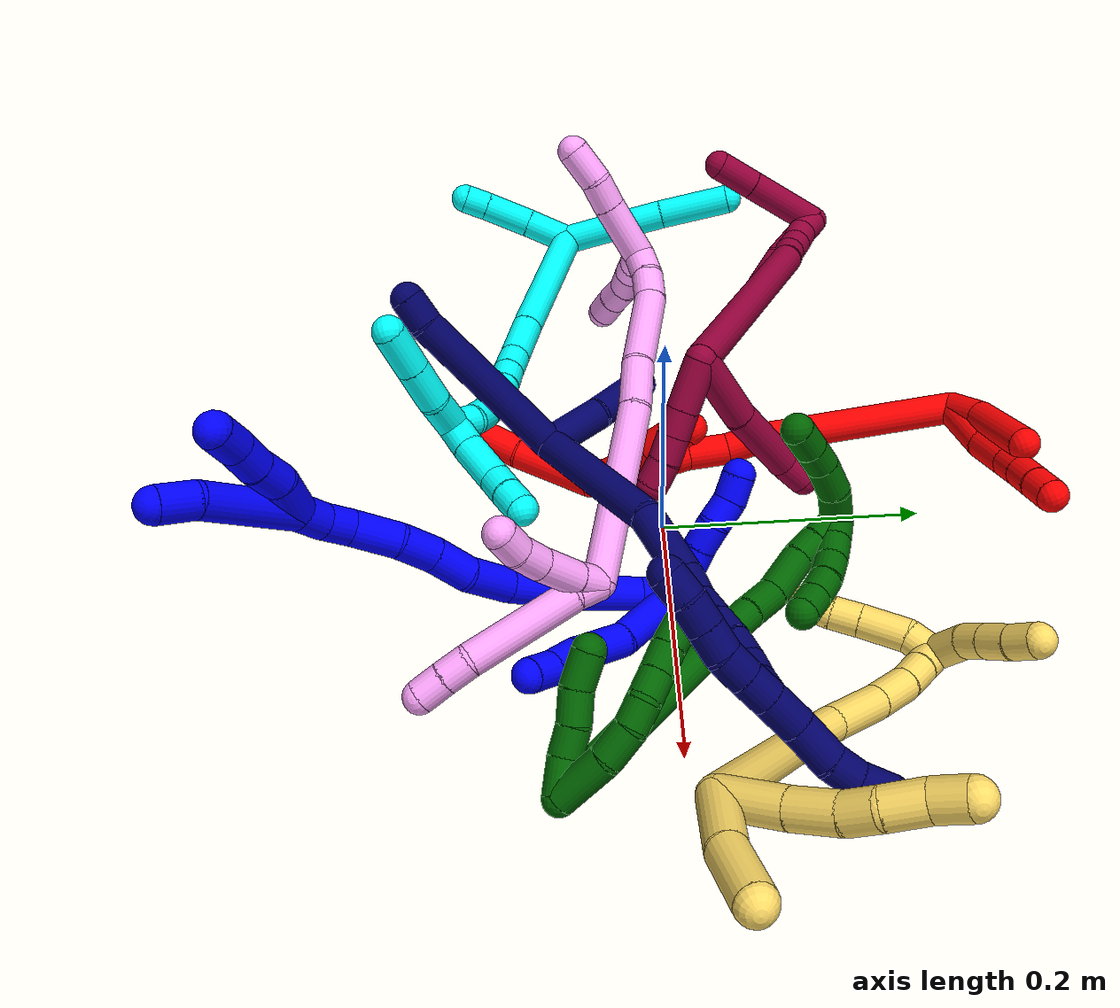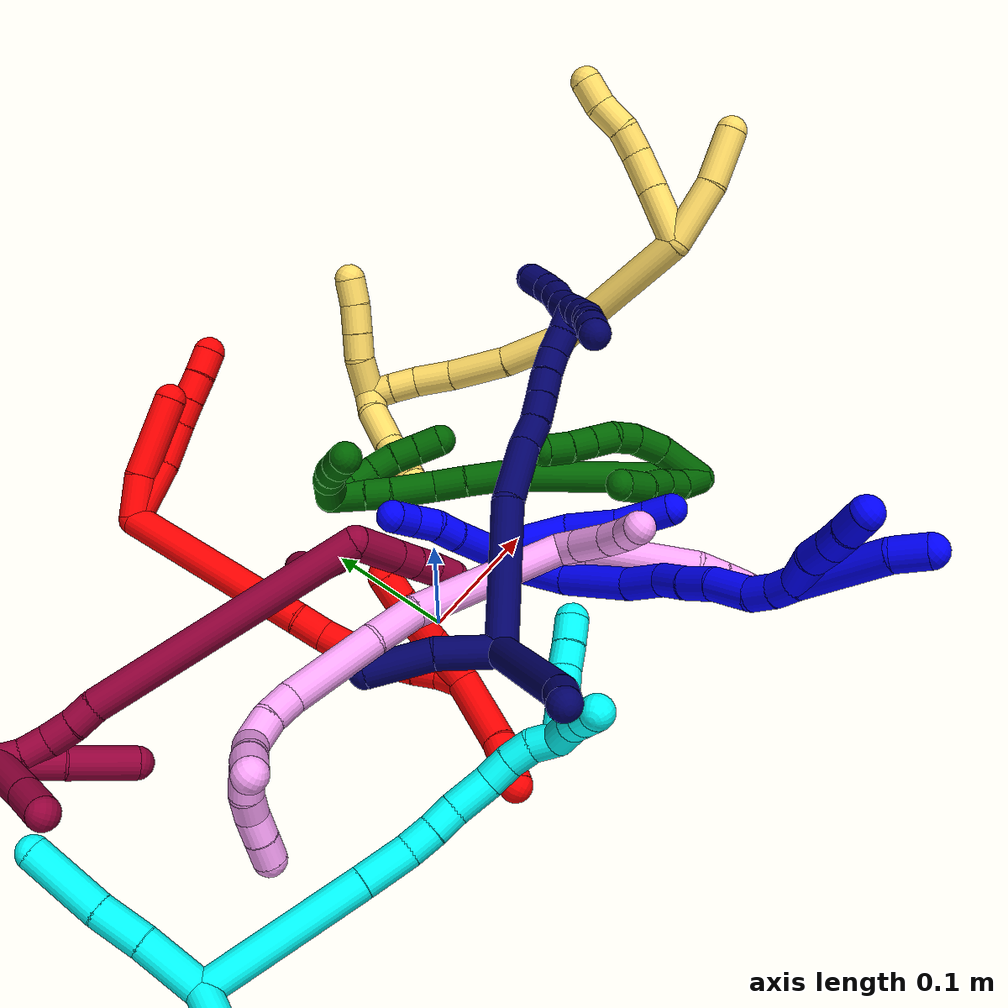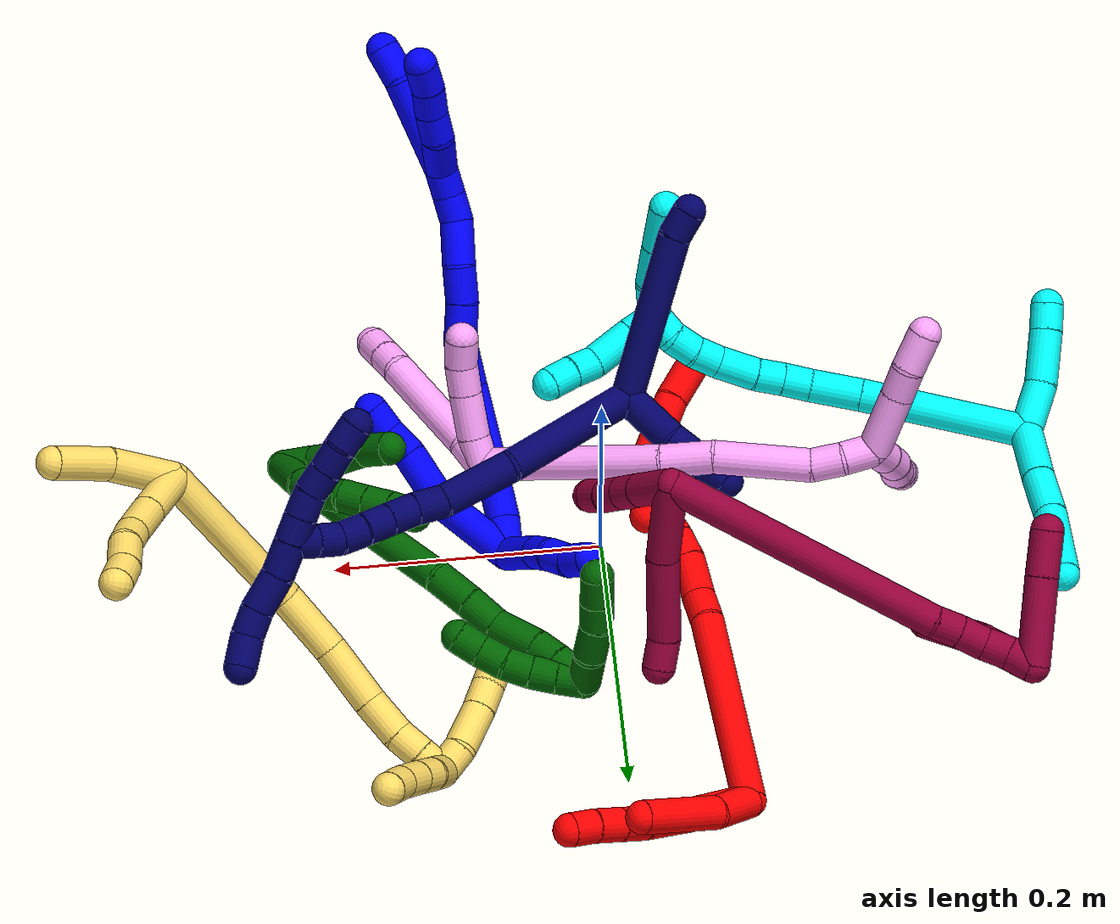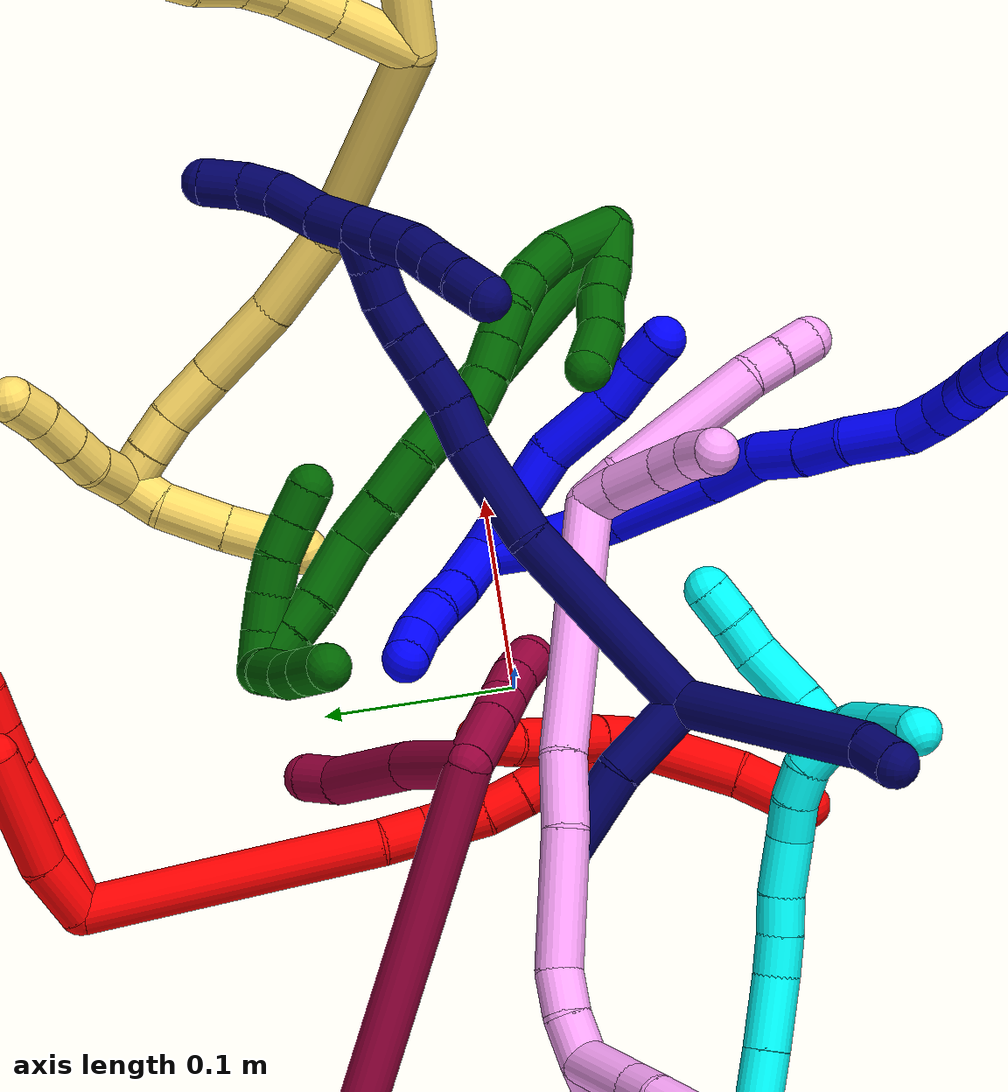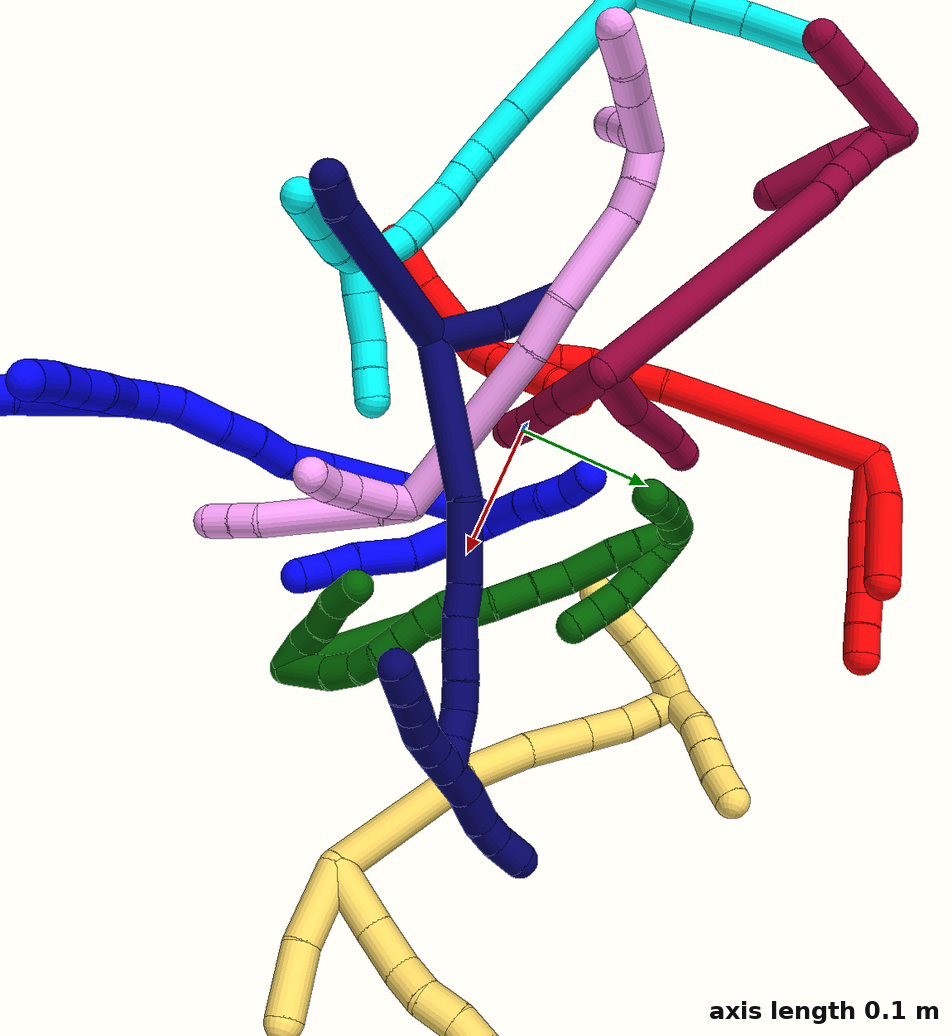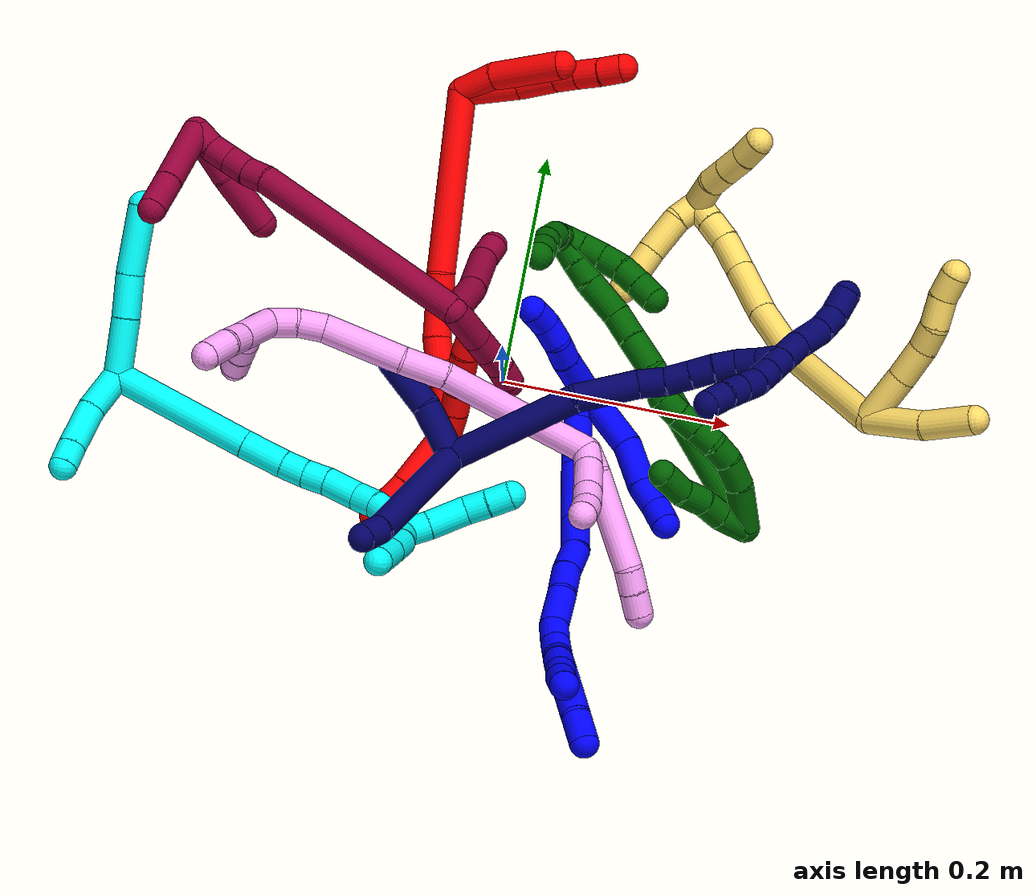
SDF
<sdf version="1.7">
 <world name="default">
  <plugin name="TubeGeneratorPlugin" filename="libtube_generator_plugin.so"/>
  <model name="photoneo_s_sensor">
   <static>1</static>
   <pose>0 0 2 1.57079 1.57079 3.14159</pose>
   <link name="link">
    <inertial><mass>0.1</mass></inertial>
    <sensor name="sensor" type="depth">
     <update_rate>30</update_rate>
     <camera>
      <horizontal_fov>1.22</horizontal_fov>
      <image><width>1920</width><height>1200</height><format>B8G8R8</format></image>
      <clip><near>0.1</near><far>4</far></clip>
      <depth_camera><output>points</output></depth_camera>
     </camera>
     <plugin name="camera_plugin" filename="libgazebo_ros_depth_camera.so">
      <baseline>0.2</baseline>
      <alwaysOn>1</alwaysOn>
      <updateRate>0.0</updateRate>
      <cameraName>camera_ir</cameraName>
      <imageTopicName>/camera/color/image_raw</imageTopicName>
      <cameraInfoTopicName>/camera/color/camera_info</cameraInfoTopicName>
      <depthImageTopicName>/camera/depth/image_raw</depthImageTopicName>
      <depthImageCameraInfoTopicName>/camera/depth/camera_info</depthImageCameraInfoTopicName>
      <pointCloudTopicName>/camera/depth/points</pointCloudTopicName>
      <frameName>fr_optical</frameName>
      <pointCloudCutoff>0.1</pointCloudCutoff>
      <pointCloudCutoffMax>2.0</pointCloudCutoffMax>
      <distortionK1>0</distortionK1>
      <distortionK2>0</distortionK2>
      <distortionK3>0</distortionK3>
      <distortionT1>0</distortionT1>
      <distortionT2>0</distortionT2>
      <CxPrime>0</CxPrime>
      <Cx>0</Cx>
      <Cy>0</Cy>
      <focalLength>0</focalLength>
      <hackBaseline>0</hackBaseline>
     </plugin>
    </sensor>
   </link>
  </model>
  <gravity>0 0 -9.8</gravity>
  <magnetic_field>6e-06 2.3e-05 -4.2e-05</magnetic_field>
  <atmosphere type="adiabatic"/>
  <physics name="default_physics" default="0" type="ode">
   <max_step_size>0.003</max_step_size>
   <real_time_factor>1</real_time_factor>
   <real_time_update_rate>1000</real_time_update_rate>
   <max_contacts>10000</max_contacts>
   <ode>
    <solver>
     <type>quick</type>
     <iters>100</iters>
     <sor>1.3</sor>
     <use_dynamic_moi_rescaling>0</use_dynamic_moi_rescaling>
    </solver>
    <constraints>
     <contact_max_correcting_vel>0</contact_max_correcting_vel>
     <contact_surface_layer>0.001</contact_surface_layer>
     <cfm>0</cfm>
     <erp>0.2</erp>
    </constraints>
   </ode>
  </physics>
  <scene><ambient>0.4 0.4 0.4 1</ambient><background>0.7 0.7 0.7 1</background><shadows>0</shadows></scene>
  <audio><device>default</device></audio>
  <spherical_coordinates>
   <surface_model>EARTH_WGS84</surface_model>
   <latitude_deg>0</latitude_deg>
   <longitude_deg>0</longitude_deg>
   <elevation>0</elevation>
   <heading_deg>0</heading_deg>
  </spherical_coordinates>
  <model name="bin">
   <static>1</static>
   <link name="bottom">
    <collision name="collision-bottom">
     <pose>0 0 -0.01 0 -0 0</pose>
     <geometry><box><size>0.8 0.6 0.02</size></box></geometry>
     <surface>
      <friction><ode><mu>100</mu><mu2>100</mu2></ode></friction>
      <contact><collide_bitmask>65535</collide_bitmask></contact>
     </surface>
    </collision>
   </link>
   <link name="west_wall">
    <collision name="collision-west_wall">
     <pose>-0.41 0 0.1 0 -0 0</pose>
     <geometry><box><size>0.02 0.6 0.2</size></box></geometry>
     <surface>
      <friction><ode><mu>100</mu><mu2>100</mu2></ode></friction>
      <contact><collide_bitmask>65535</collide_bitmask></contact>
     </surface>
    </collision>
   </link>
   <link name="east_wall">
    <collision name="collision-east_wall">
     <pose>0.41 0 0.1 0 -0 0</pose>
     <geometry><box><size>0.02 0.6 0.2</size></box></geometry>
     <surface>
      <friction><ode><mu>100</mu><mu2>100</mu2></ode></friction>
      <contact><collide_bitmask>65535</collide_bitmask></contact>
     </surface>
    </collision>
   </link>
   <link name="south_wall">
    <collision name="collision-south_wall">
     <pose>0 -0.31 0.1 0 -0 0</pose>
     <geometry><box><size>0.8 0.02 0.2</size></box></geometry>
     <surface>
      <friction><ode><mu>100</mu><mu2>100</mu2></ode></friction>
      <contact><collide_bitmask>65535</collide_bitmask></contact>
     </surface>
    </collision>
   </link>
   <link name="north_wall">
    <collision name="collision-north_wall">
     <pose>0 0.31 0.1 0 -0 0</pose>
     <geometry><box><size>0.8 0.02 0.2</size></box></geometry>
     <surface>
      <friction><ode><mu>100</mu><mu2>100</mu2></ode></friction>
      <contact><collide_bitmask>65535</collide_bitmask></contact>
     </surface>
    </collision>
   </link>
  </model>
  <model name="1">
   <static>0</static>
   <link name="1">
    <collision name="collision-cylinder-e_1_2_8">
     <pose>0.016915 -0.00324 0.026896 0.119895 0.558158 0.034395</pose>
     <geometry><cylinder><radius>0.0125</radius><length>0.063875</length></cylinder></geometry>
     <surface>
      <friction><ode><mu>1.16</mu><mu2>1.16</mu2><slip1>0</slip1><slip2>0</slip2></ode></friction>
      <contact><ode><kp>1e+06</kp><kd>1</kd><max_vel>0</max_vel><min_depth>0.001</min_depth></ode></contact>
     </surface>
    </collision>
    <visual name="visual-cylinder-e_1_2_8">
     <pose>0.016915 -0.00324 0.026896 0.119895 0.558158 0.034395</pose>
     <geometry><cylinder><radius>0.0125</radius><length>0.063875</length></cylinder></geometry>
     <material><ambient>0 0 1 1</ambient></material>
    </visual>
    <collision name="collision-cylinder-e_2_8_9">
     <pose>0.04187 -0.014619 0.0712 0.437349 0.396264 0.089173</pose>
     <geometry><cylinder><radius>0.0125</radius><length>0.041661</length></cylinder></geometry>
     <surface>
      <friction><ode><mu>1.16</mu><mu2>1.16</mu2><slip1>0</slip1><slip2>0</slip2></ode></friction>
      <contact><ode><kp>1e+06</kp><kd>1</kd><max_vel>0</max_vel><min_depth>0.001</min_depth></ode></contact>
     </surface>
    </collision>
    <visual name="visual-cylinder-e_2_8_9">
     <pose>0.04187 -0.014619 0.0712 0.437349 0.396264 0.089173</pose>
     <geometry><cylinder><radius>0.0125</radius><length>0.041661</length></cylinder></geometry>
     <material><ambient>0 0 1 1</ambient></material>
    </visual>
    <collision name="collision-cylinder-e_3_9_10">
     <pose>0.054514 -0.02498 0.09927 0.20541 0.399932 0.041772</pose>
     <geometry><cylinder><radius>0.0125</radius><length>0.023651</length></cylinder></geometry>
     <surface>
      <friction><ode><mu>1.16</mu><mu2>1.16</mu2><slip1>0</slip1><slip2>0</slip2></ode></friction>
      <contact><ode><kp>1e+06</kp><kd>1</kd><max_vel>0</max_vel><min_depth>0.001</min_depth></ode></contact>
     </surface>
    </collision>
    <visual name="visual-cylinder-e_3_9_10">
     <pose>0.054514 -0.02498 0.09927 0.20541 0.399932 0.041772</pose>
     <geometry><cylinder><radius>0.0125</radius><length>0.023651</length></cylinder></geometry>
     <material><ambient>0 0 1 1</ambient></material>
    </visual>
    <collision name="collision-cylinder-e_4_10_6">
     <pose>0.061754 -0.03001 0.119601 0.282709 0.256059 0.036634</pose>
     <geometry><cylinder><radius>0.0125</radius><length>0.020813</length></cylinder></geometry>
     <surface>
      <friction><ode><mu>1.16</mu><mu2>1.16</mu2><slip1>0</slip1><slip2>0</slip2></ode></friction>
      <contact><ode><kp>1e+06</kp><kd>1</kd><max_vel>0</max_vel><min_depth>0.001</min_depth></ode></contact>
     </surface>
    </collision>
    <visual name="visual-cylinder-e_4_10_6">
     <pose>0.061754 -0.03001 0.119601 0.282709 0.256059 0.036634</pose>
     <geometry><cylinder><radius>0.0125</radius><length>0.020813</length></cylinder></geometry>
     <material><ambient>0 0 1 1</ambient></material>
    </visual>
    <collision name="collision-cylinder-e_1_2_11">
     <pose>-0.019483 -0.000377 -5.5e-05 1.71639 -1.55122 -1.69699</pose>
     <geometry><cylinder><radius>0.0125</radius><length>0.038974</length></cylinder></geometry>
     <surface>
      <friction><ode><mu>1.16</mu><mu2>1.16</mu2><slip1>0</slip1><slip2>0</slip2></ode></friction>
      <contact><ode><kp>1e+06</kp><kd>1</kd><max_vel>0</max_vel><min_depth>0.001</min_depth></ode></contact>
     </surface>
    </collision>
    <visual name="visual-cylinder-e_1_2_11">
     <pose>-0.019483 -0.000377 -5.5e-05 1.71639 -1.55122 -1.69699</pose>
     <geometry><cylinder><radius>0.0125</radius><length>0.038974</length></cylinder></geometry>
     <material><ambient>0 0 1 1</ambient></material>
    </visual>
    <collision name="collision-cylinder-e_2_11_12">
     <pose>-0.049289 0.000231 -0.000324 -1.78341 -1.4734 1.68722</pose>
     <geometry><cylinder><radius>0.0125</radius><length>0.020743</length></cylinder></geometry>
     <surface>
      <friction><ode><mu>1.16</mu><mu2>1.16</mu2><slip1>0</slip1><slip2>0</slip2></ode></friction>
      <contact><ode><kp>1e+06</kp><kd>1</kd><max_vel>0</max_vel><min_depth>0.001</min_depth></ode></contact>
     </surface>
    </collision>
    <visual name="visual-cylinder-e_2_11_12">
     <pose>-0.049289 0.000231 -0.000324 -1.78341 -1.4734 1.68722</pose>
     <geometry><cylinder><radius>0.0125</radius><length>0.020743</length></cylinder></geometry>
     <material><ambient>0 0 1 1</ambient></material>
    </visual>
    <collision name="collision-cylinder-e_3_12_13">
     <pose>-0.069262 0.001903 -0.003473 -2.91196 -1.2679 2.8304</pose>
     <geometry><cylinder><radius>0.0125</radius><length>0.02022</length></cylinder></geometry>
     <surface>
      <friction><ode><mu>1.16</mu><mu2>1.16</mu2><slip1>0</slip1><slip2>0</slip2></ode></friction>
      <contact><ode><kp>1e+06</kp><kd>1</kd><max_vel>0</max_vel><min_depth>0.001</min_depth></ode></contact>
     </surface>
    </collision>
    <visual name="visual-cylinder-e_3_12_13">
     <pose>-0.069262 0.001903 -0.003473 -2.91196 -1.2679 2.8304</pose>
     <geometry><cylinder><radius>0.0125</radius><length>0.02022</length></cylinder></geometry>
     <material><ambient>0 0 1 1</ambient></material>
    </visual>
    <collision name="collision-cylinder-e_4_13_5">
     <pose>-0.088801 0.001081 -0.007152 2.02788 -1.40233 -1.87081</pose>
     <geometry><cylinder><radius>0.0125</radius><length>0.020062</length></cylinder></geometry>
     <surface>
      <friction><ode><mu>1.16</mu><mu2>1.16</mu2><slip1>0</slip1><slip2>0</slip2></ode></friction>
      <contact><ode><kp>1e+06</kp><kd>1</kd><max_vel>0</max_vel><min_depth>0.001</min_depth></ode></contact>
     </surface>
    </collision>
    <visual name="visual-cylinder-e_4_13_5">
     <pose>-0.088801 0.001081 -0.007152 2.02788 -1.40233 -1.87081</pose>
     <geometry><cylinder><radius>0.0125</radius><length>0.020062</length></cylinder></geometry>
     <material><ambient>0 0 1 1</ambient></material>
    </visual>
    <collision name="collision-cylinder-e_1_2_14">
     <pose>0.005426 -0.01093 0.006213 1.05393 0.407428 0.239247</pose>
     <geometry><cylinder><radius>0.0125</radius><length>0.027386</length></cylinder></geometry>
     <surface>
      <friction><ode><mu>1.16</mu><mu2>1.16</mu2><slip1>0</slip1><slip2>0</slip2></ode></friction>
      <contact><ode><kp>1e+06</kp><kd>1</kd><max_vel>0</max_vel><min_depth>0.001</min_depth></ode></contact>
     </surface>
    </collision>
    <visual name="visual-cylinder-e_1_2_14">
     <pose>0.005426 -0.01093 0.006213 1.05393 0.407428 0.239247</pose>
     <geometry><cylinder><radius>0.0125</radius><length>0.027386</length></cylinder></geometry>
     <material><ambient>0 0 1 1</ambient></material>
    </visual>
    <collision name="collision-cylinder-e_2_14_15">
     <pose>0.017499 -0.037712 0.027854 0.798954 0.291907 0.12396</pose>
     <geometry><cylinder><radius>0.0125</radius><length>0.046197</length></cylinder></geometry>
     <surface>
      <friction><ode><mu>1.16</mu><mu2>1.16</mu2><slip1>0</slip1><slip2>0</slip2></ode></friction>
      <contact><ode><kp>1e+06</kp><kd>1</kd><max_vel>0</max_vel><min_depth>0.001</min_depth></ode></contact>
     </surface>
    </collision>
    <visual name="visual-cylinder-e_2_14_15">
     <pose>0.017499 -0.037712 0.027854 0.798954 0.291907 0.12396</pose>
     <geometry><cylinder><radius>0.0125</radius><length>0.046197</length></cylinder></geometry>
     <material><ambient>0 0 1 1</ambient></material>
    </visual>
    <collision name="collision-cylinder-e_3_15_16">
     <pose>0.028324 -0.071751 0.065787 0.679684 0.143417 0.050782</pose>
     <geometry><cylinder><radius>0.0125</radius><length>0.058468</length></cylinder></geometry>
     <surface>
      <friction><ode><mu>1.16</mu><mu2>1.16</mu2><slip1>0</slip1><slip2>0</slip2></ode></friction>
      <contact><ode><kp>1e+06</kp><kd>1</kd><max_vel>0</max_vel><min_depth>0.001</min_depth></ode></contact>
     </surface>
    </collision>
    <visual name="visual-cylinder-e_3_15_16">
     <pose>0.028324 -0.071751 0.065787 0.679684 0.143417 0.050782</pose>
     <geometry><cylinder><radius>0.0125</radius><length>0.058468</length></cylinder></geometry>
     <material><ambient>0 0 1 1</ambient></material>
    </visual>
    <collision name="collision-cylinder-e_4_16_17">
     <pose>0.031662 -0.099452 0.102928 0.576388 -0.048104 -0.014263</pose>
     <geometry><cylinder><radius>0.0125</radius><length>0.034956</length></cylinder></geometry>
     <surface>
      <friction><ode><mu>1.16</mu><mu2>1.16</mu2><slip1>0</slip1><slip2>0</slip2></ode></friction>
      <contact><ode><kp>1e+06</kp><kd>1</kd><max_vel>0</max_vel><min_depth>0.001</min_depth></ode></contact>
     </surface>
    </collision>
    <visual name="visual-cylinder-e_4_16_17">
     <pose>0.031662 -0.099452 0.102928 0.576388 -0.048104 -0.014263</pose>
     <geometry><cylinder><radius>0.0125</radius><length>0.034956</length></cylinder></geometry>
     <material><ambient>0 0 1 1</ambient></material>
    </visual>
    <collision name="collision-cylinder-e_5_17_18">
     <pose>0.027823 -0.119438 0.127446 0.814399 -0.205337 -0.088817</pose>
     <geometry><cylinder><radius>0.0125</radius><length>0.029413</length></cylinder></geometry>
     <surface>
      <friction><ode><mu>1.16</mu><mu2>1.16</mu2><slip1>0</slip1><slip2>0</slip2></ode></friction>
      <contact><ode><kp>1e+06</kp><kd>1</kd><max_vel>0</max_vel><min_depth>0.001</min_depth></ode></contact>
     </surface>
    </collision>
    <visual name="visual-cylinder-e_5_17_18">
     <pose>0.027823 -0.119438 0.127446 0.814399 -0.205337 -0.088817</pose>
     <geometry><cylinder><radius>0.0125</radius><length>0.029413</length></cylinder></geometry>
     <material><ambient>0 0 1 1</ambient></material>
    </visual>
    <collision name="collision-cylinder-e_6_18_19">
     <pose>0.023335 -0.138793 0.147784 0.704218 -0.108146 -0.039768</pose>
     <geometry><cylinder><radius>0.0125</radius><length>0.027602</length></cylinder></geometry>
     <surface>
      <friction><ode><mu>1.16</mu><mu2>1.16</mu2><slip1>0</slip1><slip2>0</slip2></ode></friction>
      <contact><ode><kp>1e+06</kp><kd>1</kd><max_vel>0</max_vel><min_depth>0.001</min_depth></ode></contact>
     </surface>
    </collision>
    <visual name="visual-cylinder-e_6_18_19">
     <pose>0.023335 -0.138793 0.147784 0.704218 -0.108146 -0.039768</pose>
     <geometry><cylinder><radius>0.0125</radius><length>0.027602</length></cylinder></geometry>
     <material><ambient>0 0 1 1</ambient></material>
    </visual>
    <collision name="collision-cylinder-e_7_19_20">
     <pose>0.022909 -0.160578 0.169396 0.857857 0.062281 0.02849</pose>
     <geometry><cylinder><radius>0.0125</radius><length>0.03418</length></cylinder></geometry>
     <surface>
      <friction><ode><mu>1.16</mu><mu2>1.16</mu2><slip1>0</slip1><slip2>0</slip2></ode></friction>
      <contact><ode><kp>1e+06</kp><kd>1</kd><max_vel>0</max_vel><min_depth>0.001</min_depth></ode></contact>
     </surface>
    </collision>
    <visual name="visual-cylinder-e_7_19_20">
     <pose>0.022909 -0.160578 0.169396 0.857857 0.062281 0.02849</pose>
     <geometry><cylinder><radius>0.0125</radius><length>0.03418</length></cylinder></geometry>
     <material><ambient>0 0 1 1</ambient></material>
    </visual>
    <collision name="collision-cylinder-e_8_20_21">
     <pose>0.023774 -0.178789 0.189637 0.528828 -0.018847 -0.005103</pose>
     <geometry><cylinder><radius>0.0125</radius><length>0.021047</length></cylinder></geometry>
     <surface>
      <friction><ode><mu>1.16</mu><mu2>1.16</mu2><slip1>0</slip1><slip2>0</slip2></ode></friction>
      <contact><ode><kp>1e+06</kp><kd>1</kd><max_vel>0</max_vel><min_depth>0.001</min_depth></ode></contact>
     </surface>
    </collision>
    <visual name="visual-cylinder-e_8_20_21">
     <pose>0.023774 -0.178789 0.189637 0.528828 -0.018847 -0.005103</pose>
     <geometry><cylinder><radius>0.0125</radius><length>0.021047</length></cylinder></geometry>
     <material><ambient>0 0 1 1</ambient></material>
    </visual>
    <collision name="collision-cylinder-e_9_21_1">
     <pose>0.021765 -0.188232 0.208063 0.416681 -0.175404 -0.037173</pose>
     <geometry><cylinder><radius>0.0125</radius><length>0.020752</length></cylinder></geometry>
     <surface>
      <friction><ode><mu>1.16</mu><mu2>1.16</mu2><slip1>0</slip1><slip2>0</slip2></ode></friction>
      <contact><ode><kp>1e+06</kp><kd>1</kd><max_vel>0</max_vel><min_depth>0.001</min_depth></ode></contact>
     </surface>
    </collision>
    <visual name="visual-cylinder-e_9_21_1">
     <pose>0.021765 -0.188232 0.208063 0.416681 -0.175404 -0.037173</pose>
     <geometry><cylinder><radius>0.0125</radius><length>0.020752</length></cylinder></geometry>
     <material><ambient>0 0 1 1</ambient></material>
    </visual>
    <collision name="collision-cylinder-e_1_1_22">
     <pose>0.020698 -0.20636 0.251456 0.389911 0.020174 0.003984</pose>
     <geometry><cylinder><radius>0.0125</radius><length>0.073642</length></cylinder></geometry>
     <surface>
      <friction><ode><mu>1.16</mu><mu2>1.16</mu2><slip1>0</slip1><slip2>0</slip2></ode></friction>
      <contact><ode><kp>1e+06</kp><kd>1</kd><max_vel>0</max_vel><min_depth>0.001</min_depth></ode></contact>
     </surface>
    </collision>
    <visual name="visual-cylinder-e_1_1_22">
     <pose>0.020698 -0.20636 0.251456 0.389911 0.020174 0.003984</pose>
     <geometry><cylinder><radius>0.0125</radius><length>0.073642</length></cylinder></geometry>
     <material><ambient>0 0 1 1</ambient></material>
    </visual>
    <collision name="collision-cylinder-e_2_22_4">
     <pose>0.025464 -0.225851 0.296788 0.453427 0.310262 0.07212</pose>
     <geometry><cylinder><radius>0.0125</radius><length>0.026358</length></cylinder></geometry>
     <surface>
      <friction><ode><mu>1.16</mu><mu2>1.16</mu2><slip1>0</slip1><slip2>0</slip2></ode></friction>
      <contact><ode><kp>1e+06</kp><kd>1</kd><max_vel>0</max_vel><min_depth>0.001</min_depth></ode></contact>
     </surface>
    </collision>
    <visual name="visual-cylinder-e_2_22_4">
     <pose>0.025464 -0.225851 0.296788 0.453427 0.310262 0.07212</pose>
     <geometry><cylinder><radius>0.0125</radius><length>0.026358</length></cylinder></geometry>
     <material><ambient>0 0 1 1</ambient></material>
    </visual>
    <collision name="collision-cylinder-e_1_1_23">
     <pose>0.009961 -0.19553 0.230178 0.242716 -0.6496 -0.082086</pose>
     <geometry><cylinder><radius>0.0125</radius><length>0.033046</length></cylinder></geometry>
     <surface>
      <friction><ode><mu>1.16</mu><mu2>1.16</mu2><slip1>0</slip1><slip2>0</slip2></ode></friction>
      <contact><ode><kp>1e+06</kp><kd>1</kd><max_vel>0</max_vel><min_depth>0.001</min_depth></ode></contact>
     </surface>
    </collision>
    <visual name="visual-cylinder-e_1_1_23">
     <pose>0.009961 -0.19553 0.230178 0.242716 -0.6496 -0.082086</pose>
     <geometry><cylinder><radius>0.0125</radius><length>0.033046</length></cylinder></geometry>
     <material><ambient>0 0 1 1</ambient></material>
    </visual>
    <collision name="collision-cylinder-e_2_23_24">
     <pose>-0.004071 -0.202275 0.252968 0.343452 -0.36266 -0.063575</pose>
     <geometry><cylinder><radius>0.0125</radius><length>0.022759</length></cylinder></geometry>
     <surface>
      <friction><ode><mu>1.16</mu><mu2>1.16</mu2><slip1>0</slip1><slip2>0</slip2></ode></friction>
      <contact><ode><kp>1e+06</kp><kd>1</kd><max_vel>0</max_vel><min_depth>0.001</min_depth></ode></contact>
     </surface>
    </collision>
    <visual name="visual-cylinder-e_2_23_24">
     <pose>-0.004071 -0.202275 0.252968 0.343452 -0.36266 -0.063575</pose>
     <geometry><cylinder><radius>0.0125</radius><length>0.022759</length></cylinder></geometry>
     <material><ambient>0 0 1 1</ambient></material>
    </visual>
    <collision name="collision-cylinder-e_3_24_25">
     <pose>-0.013294 -0.209243 0.272007 0.35911 -0.493805 -0.091434</pose>
     <geometry><cylinder><radius>0.0125</radius><length>0.021885</length></cylinder></geometry>
     <surface>
      <friction><ode><mu>1.16</mu><mu2>1.16</mu2><slip1>0</slip1><slip2>0</slip2></ode></friction>
      <contact><ode><kp>1e+06</kp><kd>1</kd><max_vel>0</max_vel><min_depth>0.001</min_depth></ode></contact>
     </surface>
    </collision>
    <visual name="visual-cylinder-e_3_24_25">
     <pose>-0.013294 -0.209243 0.272007 0.35911 -0.493805 -0.091434</pose>
     <geometry><cylinder><radius>0.0125</radius><length>0.021885</length></cylinder></geometry>
     <material><ambient>0 0 1 1</ambient></material>
    </visual>
    <collision name="collision-cylinder-e_4_25_3">
     <pose>-0.022998 -0.215062 0.290933 0.240755 -0.416932 -0.051165</pose>
     <geometry><cylinder><radius>0.0125</radius><length>0.02231</length></cylinder></geometry>
     <surface>
      <friction><ode><mu>1.16</mu><mu2>1.16</mu2><slip1>0</slip1><slip2>0</slip2></ode></friction>
      <contact><ode><kp>1e+06</kp><kd>1</kd><max_vel>0</max_vel><min_depth>0.001</min_depth></ode></contact>
     </surface>
    </collision>
    <visual name="visual-cylinder-e_4_25_3">
     <pose>-0.022998 -0.215062 0.290933 0.240755 -0.416932 -0.051165</pose>
     <geometry><cylinder><radius>0.0125</radius><length>0.02231</length></cylinder></geometry>
     <material><ambient>0 0 1 1</ambient></material>
    </visual>
    <collision name="collision-sphere-3">
     <pose>-0.027515 -0.217493 0.300838 0 -0 0</pose>
     <geometry><sphere><radius>0.0125</radius></sphere></geometry>
     <surface>
      <friction><ode><mu>1.16</mu><mu2>1.16</mu2><slip1>0</slip1><slip2>0</slip2></ode></friction>
      <contact><ode><kp>1e+06</kp><kd>1</kd><max_vel>0</max_vel><min_depth>0.001</min_depth></ode></contact>
     </surface>
    </collision>
    <visual name="visual-sphere-3">
     <pose>-0.027515 -0.217493 0.300838 0 -0 0</pose>
     <geometry><sphere><radius>0.0125</radius></sphere></geometry>
     <material><ambient>0 0 1 1</ambient></material>
    </visual>
    <collision name="collision-sphere-25">
     <pose>-0.018481 -0.21263 0.281027 0 -0 0</pose>
     <geometry><sphere><radius>0.0125</radius></sphere></geometry>
     <surface>
      <friction><ode><mu>1.16</mu><mu2>1.16</mu2><slip1>0</slip1><slip2>0</slip2></ode></friction>
      <contact><ode><kp>1e+06</kp><kd>1</kd><max_vel>0</max_vel><min_depth>0.001</min_depth></ode></contact>
     </surface>
    </collision>
    <visual name="visual-sphere-25">
     <pose>-0.018481 -0.21263 0.281027 0 -0 0</pose>
     <geometry><sphere><radius>0.0125</radius></sphere></geometry>
     <material><ambient>0 0 1 1</ambient></material>
    </visual>
    <collision name="collision-sphere-24">
     <pose>-0.008108 -0.205857 0.262986 0 -0 0</pose>
     <geometry><sphere><radius>0.0125</radius></sphere></geometry>
     <surface>
      <friction><ode><mu>1.16</mu><mu2>1.16</mu2><slip1>0</slip1><slip2>0</slip2></ode></friction>
      <contact><ode><kp>1e+06</kp><kd>1</kd><max_vel>0</max_vel><min_depth>0.001</min_depth></ode></contact>
     </surface>
    </collision>
    <visual name="visual-sphere-24">
     <pose>-0.008108 -0.205857 0.262986 0 -0 0</pose>
     <geometry><sphere><radius>0.0125</radius></sphere></geometry>
     <material><ambient>0 0 1 1</ambient></material>
    </visual>
    <collision name="collision-sphere-23">
     <pose>-3.4e-05 -0.198692 0.24295 0 -0 0</pose>
     <geometry><sphere><radius>0.0125</radius></sphere></geometry>
     <surface>
      <friction><ode><mu>1.16</mu><mu2>1.16</mu2><slip1>0</slip1><slip2>0</slip2></ode></friction>
      <contact><ode><kp>1e+06</kp><kd>1</kd><max_vel>0</max_vel><min_depth>0.001</min_depth></ode></contact>
     </surface>
    </collision>
    <visual name="visual-sphere-23">
     <pose>-3.4e-05 -0.198692 0.24295 0 -0 0</pose>
     <geometry><sphere><radius>0.0125</radius></sphere></geometry>
     <material><ambient>0 0 1 1</ambient></material>
    </visual>
    <collision name="collision-sphere-4">
     <pose>0.029488 -0.231348 0.30807 0 -0 0</pose>
     <geometry><sphere><radius>0.0125</radius></sphere></geometry>
     <surface>
      <friction><ode><mu>1.16</mu><mu2>1.16</mu2><slip1>0</slip1><slip2>0</slip2></ode></friction>
      <contact><ode><kp>1e+06</kp><kd>1</kd><max_vel>0</max_vel><min_depth>0.001</min_depth></ode></contact>
     </surface>
    </collision>
    <visual name="visual-sphere-4">
     <pose>0.029488 -0.231348 0.30807 0 -0 0</pose>
     <geometry><sphere><radius>0.0125</radius></sphere></geometry>
     <material><ambient>0 0 1 1</ambient></material>
    </visual>
    <collision name="collision-sphere-22">
     <pose>0.02144 -0.220353 0.285507 0 -0 0</pose>
     <geometry><sphere><radius>0.0125</radius></sphere></geometry>
     <surface>
      <friction><ode><mu>1.16</mu><mu2>1.16</mu2><slip1>0</slip1><slip2>0</slip2></ode></friction>
      <contact><ode><kp>1e+06</kp><kd>1</kd><max_vel>0</max_vel><min_depth>0.001</min_depth></ode></contact>
     </surface>
    </collision>
    <visual name="visual-sphere-22">
     <pose>0.02144 -0.220353 0.285507 0 -0 0</pose>
     <geometry><sphere><radius>0.0125</radius></sphere></geometry>
     <material><ambient>0 0 1 1</ambient></material>
    </visual>
    <collision name="collision-sphere-1">
     <pose>0.019955 -0.192367 0.217406 0 -0 0</pose>
     <geometry><sphere><radius>0.0125</radius></sphere></geometry>
     <surface>
      <friction><ode><mu>1.16</mu><mu2>1.16</mu2><slip1>0</slip1><slip2>0</slip2></ode></friction>
      <contact><ode><kp>1e+06</kp><kd>1</kd><max_vel>0</max_vel><min_depth>0.001</min_depth></ode></contact>
     </surface>
    </collision>
    <visual name="visual-sphere-1">
     <pose>0.019955 -0.192367 0.217406 0 -0 0</pose>
     <geometry><sphere><radius>0.0125</radius></sphere></geometry>
     <material><ambient>0 0 1 1</ambient></material>
    </visual>
    <collision name="collision-sphere-21">
     <pose>0.023576 -0.184097 0.198721 0 -0 0</pose>
     <geometry><sphere><radius>0.0125</radius></sphere></geometry>
     <surface>
      <friction><ode><mu>1.16</mu><mu2>1.16</mu2><slip1>0</slip1><slip2>0</slip2></ode></friction>
      <contact><ode><kp>1e+06</kp><kd>1</kd><max_vel>0</max_vel><min_depth>0.001</min_depth></ode></contact>
     </surface>
    </collision>
    <visual name="visual-sphere-21">
     <pose>0.023576 -0.184097 0.198721 0 -0 0</pose>
     <geometry><sphere><radius>0.0125</radius></sphere></geometry>
     <material><ambient>0 0 1 1</ambient></material>
    </visual>
    <collision name="collision-sphere-11">
     <pose>-0.038967 -0.000755 -0.000111 0 -0 0</pose>
     <geometry><sphere><radius>0.0125</radius></sphere></geometry>
     <surface>
      <friction><ode><mu>1.16</mu><mu2>1.16</mu2><slip1>0</slip1><slip2>0</slip2></ode></friction>
      <contact><ode><kp>1e+06</kp><kd>1</kd><max_vel>0</max_vel><min_depth>0.001</min_depth></ode></contact>
     </surface>
    </collision>
    <visual name="visual-sphere-11">
     <pose>-0.038967 -0.000755 -0.000111 0 -0 0</pose>
     <geometry><sphere><radius>0.0125</radius></sphere></geometry>
     <material><ambient>0 0 1 1</ambient></material>
    </visual>
    <collision name="collision-sphere-6">
     <pose>0.06439 -0.032818 0.129269 0 -0 0</pose>
     <geometry><sphere><radius>0.0125</radius></sphere></geometry>
     <surface>
      <friction><ode><mu>1.16</mu><mu2>1.16</mu2><slip1>0</slip1><slip2>0</slip2></ode></friction>
      <contact><ode><kp>1e+06</kp><kd>1</kd><max_vel>0</max_vel><min_depth>0.001</min_depth></ode></contact>
     </surface>
    </collision>
    <visual name="visual-sphere-6">
     <pose>0.06439 -0.032818 0.129269 0 -0 0</pose>
     <geometry><sphere><radius>0.0125</radius></sphere></geometry>
     <material><ambient>0 0 1 1</ambient></material>
    </visual>
    <collision name="collision-sphere-10">
     <pose>0.059118 -0.027202 0.109934 0 -0 0</pose>
     <geometry><sphere><radius>0.0125</radius></sphere></geometry>
     <surface>
      <friction><ode><mu>1.16</mu><mu2>1.16</mu2><slip1>0</slip1><slip2>0</slip2></ode></friction>
      <contact><ode><kp>1e+06</kp><kd>1</kd><max_vel>0</max_vel><min_depth>0.001</min_depth></ode></contact>
     </surface>
    </collision>
    <visual name="visual-sphere-10">
     <pose>0.059118 -0.027202 0.109934 0 -0 0</pose>
     <geometry><sphere><radius>0.0125</radius></sphere></geometry>
     <material><ambient>0 0 1 1</ambient></material>
    </visual>
    <collision name="collision-sphere-9">
     <pose>0.04991 -0.022758 0.088607 0 -0 0</pose>
     <geometry><sphere><radius>0.0125</radius></sphere></geometry>
     <surface>
      <friction><ode><mu>1.16</mu><mu2>1.16</mu2><slip1>0</slip1><slip2>0</slip2></ode></friction>
      <contact><ode><kp>1e+06</kp><kd>1</kd><max_vel>0</max_vel><min_depth>0.001</min_depth></ode></contact>
     </surface>
    </collision>
    <visual name="visual-sphere-9">
     <pose>0.04991 -0.022758 0.088607 0 -0 0</pose>
     <geometry><sphere><radius>0.0125</radius></sphere></geometry>
     <material><ambient>0 0 1 1</ambient></material>
    </visual>
    <collision name="collision-sphere-2">
     <geometry><sphere><radius>0.0125</radius></sphere></geometry>
     <surface>
      <friction><ode><mu>1.16</mu><mu2>1.16</mu2><slip1>0</slip1><slip2>0</slip2></ode></friction>
      <contact><ode><kp>1e+06</kp><kd>1</kd><max_vel>0</max_vel><min_depth>0.001</min_depth></ode></contact>
     </surface>
    </collision>
    <visual name="visual-sphere-2">
     <geometry><sphere><radius>0.0125</radius></sphere></geometry>
     <material><ambient>0 0 1 1</ambient></material>
    </visual>
    <collision name="collision-sphere-19">
     <pose>0.021845 -0.147676 0.15824 0 -0 0</pose>
     <geometry><sphere><radius>0.0125</radius></sphere></geometry>
     <surface>
      <friction><ode><mu>1.16</mu><mu2>1.16</mu2><slip1>0</slip1><slip2>0</slip2></ode></friction>
      <contact><ode><kp>1e+06</kp><kd>1</kd><max_vel>0</max_vel><min_depth>0.001</min_depth></ode></contact>
     </surface>
    </collision>
    <visual name="visual-sphere-19">
     <pose>0.021845 -0.147676 0.15824 0 -0 0</pose>
     <geometry><sphere><radius>0.0125</radius></sphere></geometry>
     <material><ambient>0 0 1 1</ambient></material>
    </visual>
    <collision name="collision-sphere-8">
     <pose>0.03383 -0.00648 0.053792 0 -0 0</pose>
     <geometry><sphere><radius>0.0125</radius></sphere></geometry>
     <surface>
      <friction><ode><mu>1.16</mu><mu2>1.16</mu2><slip1>0</slip1><slip2>0</slip2></ode></friction>
      <contact><ode><kp>1e+06</kp><kd>1</kd><max_vel>0</max_vel><min_depth>0.001</min_depth></ode></contact>
     </surface>
    </collision>
    <visual name="visual-sphere-8">
     <pose>0.03383 -0.00648 0.053792 0 -0 0</pose>
     <geometry><sphere><radius>0.0125</radius></sphere></geometry>
     <material><ambient>0 0 1 1</ambient></material>
    </visual>
    <collision name="collision-sphere-12">
     <pose>-0.059612 0.001217 -0.000536 0 -0 0</pose>
     <geometry><sphere><radius>0.0125</radius></sphere></geometry>
     <surface>
      <friction><ode><mu>1.16</mu><mu2>1.16</mu2><slip1>0</slip1><slip2>0</slip2></ode></friction>
      <contact><ode><kp>1e+06</kp><kd>1</kd><max_vel>0</max_vel><min_depth>0.001</min_depth></ode></contact>
     </surface>
    </collision>
    <visual name="visual-sphere-12">
     <pose>-0.059612 0.001217 -0.000536 0 -0 0</pose>
     <geometry><sphere><radius>0.0125</radius></sphere></geometry>
     <material><ambient>0 0 1 1</ambient></material>
    </visual>
    <collision name="collision-sphere-13">
     <pose>-0.078912 0.00259 -0.00641 0 -0 0</pose>
     <geometry><sphere><radius>0.0125</radius></sphere></geometry>
     <surface>
      <friction><ode><mu>1.16</mu><mu2>1.16</mu2><slip1>0</slip1><slip2>0</slip2></ode></friction>
      <contact><ode><kp>1e+06</kp><kd>1</kd><max_vel>0</max_vel><min_depth>0.001</min_depth></ode></contact>
     </surface>
    </collision>
    <visual name="visual-sphere-13">
     <pose>-0.078912 0.00259 -0.00641 0 -0 0</pose>
     <geometry><sphere><radius>0.0125</radius></sphere></geometry>
     <material><ambient>0 0 1 1</ambient></material>
    </visual>
    <collision name="collision-sphere-5">
     <pose>-0.09869 -0.000429 -0.007894 0 -0 0</pose>
     <geometry><sphere><radius>0.0125</radius></sphere></geometry>
     <surface>
      <friction><ode><mu>1.16</mu><mu2>1.16</mu2><slip1>0</slip1><slip2>0</slip2></ode></friction>
      <contact><ode><kp>1e+06</kp><kd>1</kd><max_vel>0</max_vel><min_depth>0.001</min_depth></ode></contact>
     </surface>
    </collision>
    <visual name="visual-sphere-5">
     <pose>-0.09869 -0.000429 -0.007894 0 -0 0</pose>
     <geometry><sphere><radius>0.0125</radius></sphere></geometry>
     <material><ambient>0 0 1 1</ambient></material>
    </visual>
    <collision name="collision-sphere-14">
     <pose>0.010852 -0.02186 0.012425 0 -0 0</pose>
     <geometry><sphere><radius>0.0125</radius></sphere></geometry>
     <surface>
      <friction><ode><mu>1.16</mu><mu2>1.16</mu2><slip1>0</slip1><slip2>0</slip2></ode></friction>
      <contact><ode><kp>1e+06</kp><kd>1</kd><max_vel>0</max_vel><min_depth>0.001</min_depth></ode></contact>
     </surface>
    </collision>
    <visual name="visual-sphere-14">
     <pose>0.010852 -0.02186 0.012425 0 -0 0</pose>
     <geometry><sphere><radius>0.0125</radius></sphere></geometry>
     <material><ambient>0 0 1 1</ambient></material>
    </visual>
    <collision name="collision-sphere-15">
     <pose>0.024146 -0.053565 0.043283 0 -0 0</pose>
     <geometry><sphere><radius>0.0125</radius></sphere></geometry>
     <surface>
      <friction><ode><mu>1.16</mu><mu2>1.16</mu2><slip1>0</slip1><slip2>0</slip2></ode></friction>
      <contact><ode><kp>1e+06</kp><kd>1</kd><max_vel>0</max_vel><min_depth>0.001</min_depth></ode></contact>
     </surface>
    </collision>
    <visual name="visual-sphere-15">
     <pose>0.024146 -0.053565 0.043283 0 -0 0</pose>
     <geometry><sphere><radius>0.0125</radius></sphere></geometry>
     <material><ambient>0 0 1 1</ambient></material>
    </visual>
    <collision name="collision-sphere-16">
     <pose>0.032503 -0.089938 0.088291 0 -0 0</pose>
     <geometry><sphere><radius>0.0125</radius></sphere></geometry>
     <surface>
      <friction><ode><mu>1.16</mu><mu2>1.16</mu2><slip1>0</slip1><slip2>0</slip2></ode></friction>
      <contact><ode><kp>1e+06</kp><kd>1</kd><max_vel>0</max_vel><min_depth>0.001</min_depth></ode></contact>
     </surface>
    </collision>
    <visual name="visual-sphere-16">
     <pose>0.032503 -0.089938 0.088291 0 -0 0</pose>
     <geometry><sphere><radius>0.0125</radius></sphere></geometry>
     <material><ambient>0 0 1 1</ambient></material>
    </visual>
    <collision name="collision-sphere-17">
     <pose>0.030822 -0.108967 0.117565 0 -0 0</pose>
     <geometry><sphere><radius>0.0125</radius></sphere></geometry>
     <surface>
      <friction><ode><mu>1.16</mu><mu2>1.16</mu2><slip1>0</slip1><slip2>0</slip2></ode></friction>
      <contact><ode><kp>1e+06</kp><kd>1</kd><max_vel>0</max_vel><min_depth>0.001</min_depth></ode></contact>
     </surface>
    </collision>
    <visual name="visual-sphere-17">
     <pose>0.030822 -0.108967 0.117565 0 -0 0</pose>
     <geometry><sphere><radius>0.0125</radius></sphere></geometry>
     <material><ambient>0 0 1 1</ambient></material>
    </visual>
    <collision name="collision-sphere-18">
     <pose>0.024825 -0.12991 0.137327 0 -0 0</pose>
     <geometry><sphere><radius>0.0125</radius></sphere></geometry>
     <surface>
      <friction><ode><mu>1.16</mu><mu2>1.16</mu2><slip1>0</slip1><slip2>0</slip2></ode></friction>
      <contact><ode><kp>1e+06</kp><kd>1</kd><max_vel>0</max_vel><min_depth>0.001</min_depth></ode></contact>
     </surface>
    </collision>
    <visual name="visual-sphere-18">
     <pose>0.024825 -0.12991 0.137327 0 -0 0</pose>
     <geometry><sphere><radius>0.0125</radius></sphere></geometry>
     <material><ambient>0 0 1 1</ambient></material>
    </visual>
    <collision name="collision-sphere-20">
     <pose>0.023973 -0.17348 0.180552 0 -0 0</pose>
     <geometry><sphere><radius>0.0125</radius></sphere></geometry>
     <surface>
      <friction><ode><mu>1.16</mu><mu2>1.16</mu2><slip1>0</slip1><slip2>0</slip2></ode></friction>
      <contact><ode><kp>1e+06</kp><kd>1</kd><max_vel>0</max_vel><min_depth>0.001</min_depth></ode></contact>
     </surface>
    </collision>
    <visual name="visual-sphere-20">
     <pose>0.023973 -0.17348 0.180552 0 -0 0</pose>
     <geometry><sphere><radius>0.0125</radius></sphere></geometry>
     <material><ambient>0 0 1 1</ambient></material>
    </visual>
    <inertial>
     <pose>0.011974 -0.098384 0.123033 0 -0 0</pose>
     <mass>0.75</mass>
     <inertia>
      <ixx>0.000126</ixx>
      <ixy>0</ixy>
      <ixz>0</ixz>
      <iyy>0.000109</iyy>
      <iyz>0</iyz>
      <izz>8.8e-05</izz>
     </inertia>
    </inertial>
   </link>
   <pose>0.071116 0.005342 0.012295 -0.10778 0.80716 -0.737312</pose>
  </model>
  <model name="2">
   <static>0</static>
   <link name="2">
    <collision name="collision-cylinder-e_1_2_8">
     <pose>0.022581 0.011234 0.003047 -1.30593 1.09485 -0.872572</pose>
     <geometry><cylinder><radius>0.0125</radius><length>0.050809</length></cylinder></geometry>
     <surface>
      <friction><ode><mu>1.16</mu><mu2>1.16</mu2><slip1>0</slip1><slip2>0</slip2></ode></friction>
      <contact><ode><kp>1e+06</kp><kd>1</kd><max_vel>0</max_vel><min_depth>0.001</min_depth></ode></contact>
     </surface>
    </collision>
    <visual name="visual-cylinder-e_1_2_8">
     <pose>0.022581 0.011234 0.003047 -1.30593 1.09485 -0.872572</pose>
     <geometry><cylinder><radius>0.0125</radius><length>0.050809</length></cylinder></geometry>
     <material><ambient>1 0 0 1</ambient></material>
    </visual>
    <collision name="collision-cylinder-e_2_8_9">
     <pose>0.061726 0.02745 0.009658 -0.949931 1.21659 -0.687746</pose>
     <geometry><cylinder><radius>0.0125</radius><length>0.035321</length></cylinder></geometry>
     <surface>
      <friction><ode><mu>1.16</mu><mu2>1.16</mu2><slip1>0</slip1><slip2>0</slip2></ode></friction>
      <contact><ode><kp>1e+06</kp><kd>1</kd><max_vel>0</max_vel><min_depth>0.001</min_depth></ode></contact>
     </surface>
    </collision>
    <visual name="visual-cylinder-e_2_8_9">
     <pose>0.061726 0.02745 0.009658 -0.949931 1.21659 -0.687746</pose>
     <geometry><cylinder><radius>0.0125</radius><length>0.035321</length></cylinder></geometry>
     <material><ambient>1 0 0 1</ambient></material>
    </visual>
    <collision name="collision-cylinder-e_3_9_10">
     <pose>0.088506 0.03451 0.014795 -0.922192 1.32102 -0.736736</pose>
     <geometry><cylinder><radius>0.0125</radius><length>0.021086</length></cylinder></geometry>
     <surface>
      <friction><ode><mu>1.16</mu><mu2>1.16</mu2><slip1>0</slip1><slip2>0</slip2></ode></friction>
      <contact><ode><kp>1e+06</kp><kd>1</kd><max_vel>0</max_vel><min_depth>0.001</min_depth></ode></contact>
     </surface>
    </collision>
    <visual name="visual-cylinder-e_3_9_10">
     <pose>0.088506 0.03451 0.014795 -0.922192 1.32102 -0.736736</pose>
     <geometry><cylinder><radius>0.0125</radius><length>0.021086</length></cylinder></geometry>
     <material><ambient>1 0 0 1</ambient></material>
    </visual>
    <collision name="collision-cylinder-e_4_10_11">
     <pose>0.109413 0.038998 0.01783 -1.02628 1.31292 -0.819176</pose>
     <geometry><cylinder><radius>0.0125</radius><length>0.022113</length></cylinder></geometry>
     <surface>
      <friction><ode><mu>1.16</mu><mu2>1.16</mu2><slip1>0</slip1><slip2>0</slip2></ode></friction>
      <contact><ode><kp>1e+06</kp><kd>1</kd><max_vel>0</max_vel><min_depth>0.001</min_depth></ode></contact>
     </surface>
    </collision>
    <visual name="visual-cylinder-e_4_10_11">
     <pose>0.109413 0.038998 0.01783 -1.02628 1.31292 -0.819176</pose>
     <geometry><cylinder><radius>0.0125</radius><length>0.022113</length></cylinder></geometry>
     <material><ambient>1 0 0 1</ambient></material>
    </visual>
    <collision name="collision-cylinder-e_5_11_6">
     <pose>0.129814 0.044411 0.021172 -1.01068 1.22105 -0.7387</pose>
     <geometry><cylinder><radius>0.0125</radius><length>0.020671</length></cylinder></geometry>
     <surface>
      <friction><ode><mu>1.16</mu><mu2>1.16</mu2><slip1>0</slip1><slip2>0</slip2></ode></friction>
      <contact><ode><kp>1e+06</kp><kd>1</kd><max_vel>0</max_vel><min_depth>0.001</min_depth></ode></contact>
     </surface>
    </collision>
    <visual name="visual-cylinder-e_5_11_6">
     <pose>0.129814 0.044411 0.021172 -1.01068 1.22105 -0.7387</pose>
     <geometry><cylinder><radius>0.0125</radius><length>0.020671</length></cylinder></geometry>
     <material><ambient>1 0 0 1</ambient></material>
    </visual>
    <collision name="collision-cylinder-e_1_2_12">
     <pose>0.015407 0.003284 0.007053 -0.435813 1.10319 -0.270816</pose>
     <geometry><cylinder><radius>0.0125</radius><length>0.034519</length></cylinder></geometry>
     <surface>
      <friction><ode><mu>1.16</mu><mu2>1.16</mu2><slip1>0</slip1><slip2>0</slip2></ode></friction>
      <contact><ode><kp>1e+06</kp><kd>1</kd><max_vel>0</max_vel><min_depth>0.001</min_depth></ode></contact>
     </surface>
    </collision>
    <visual name="visual-cylinder-e_1_2_12">
     <pose>0.015407 0.003284 0.007053 -0.435813 1.10319 -0.270816</pose>
     <geometry><cylinder><radius>0.0125</radius><length>0.034519</length></cylinder></geometry>
     <material><ambient>1 0 0 1</ambient></material>
    </visual>
    <collision name="collision-cylinder-e_2_12_5">
     <pose>0.062493 0.012568 0.019794 -0.811923 1.31551 -0.641198</pose>
     <geometry><cylinder><radius>0.0125</radius><length>0.065481</length></cylinder></geometry>
     <surface>
      <friction><ode><mu>1.16</mu><mu2>1.16</mu2><slip1>0</slip1><slip2>0</slip2></ode></friction>
      <contact><ode><kp>1e+06</kp><kd>1</kd><max_vel>0</max_vel><min_depth>0.001</min_depth></ode></contact>
     </surface>
    </collision>
    <visual name="visual-cylinder-e_2_12_5">
     <pose>0.062493 0.012568 0.019794 -0.811923 1.31551 -0.641198</pose>
     <geometry><cylinder><radius>0.0125</radius><length>0.065481</length></cylinder></geometry>
     <material><ambient>1 0 0 1</ambient></material>
    </visual>
    <collision name="collision-cylinder-e_1_2_13">
     <pose>0.001613 -0.0172 -0.077925 2.92435 0.020212 0.184829</pose>
     <geometry><cylinder><radius>0.0125</radius><length>0.159633</length></cylinder></geometry>
     <surface>
      <friction><ode><mu>1.16</mu><mu2>1.16</mu2><slip1>0</slip1><slip2>0</slip2></ode></friction>
      <contact><ode><kp>1e+06</kp><kd>1</kd><max_vel>0</max_vel><min_depth>0.001</min_depth></ode></contact>
     </surface>
    </collision>
    <visual name="visual-cylinder-e_1_2_13">
     <pose>0.001613 -0.0172 -0.077925 2.92435 0.020212 0.184829</pose>
     <geometry><cylinder><radius>0.0125</radius><length>0.159633</length></cylinder></geometry>
     <material><ambient>1 0 0 1</ambient></material>
    </visual>
    <collision name="collision-cylinder-e_2_13_14">
     <pose>0.002909 -0.034947 -0.168082 3.09684 -0.02593 -1.05026</pose>
     <geometry><cylinder><radius>0.0125</radius><length>0.024498</length></cylinder></geometry>
     <surface>
      <friction><ode><mu>1.16</mu><mu2>1.16</mu2><slip1>0</slip1><slip2>0</slip2></ode></friction>
      <contact><ode><kp>1e+06</kp><kd>1</kd><max_vel>0</max_vel><min_depth>0.001</min_depth></ode></contact>
     </surface>
    </collision>
    <visual name="visual-cylinder-e_2_13_14">
     <pose>0.002909 -0.034947 -0.168082 3.09684 -0.02593 -1.05026</pose>
     <geometry><cylinder><radius>0.0125</radius><length>0.024498</length></cylinder></geometry>
     <material><ambient>1 0 0 1</ambient></material>
    </visual>
    <collision name="collision-cylinder-e_3_14_15">
     <pose>0.004317 -0.039618 -0.196344 2.88984 0.103877 0.779579</pose>
     <geometry><cylinder><radius>0.0125</radius><length>0.033281</length></cylinder></geometry>
     <surface>
      <friction><ode><mu>1.16</mu><mu2>1.16</mu2><slip1>0</slip1><slip2>0</slip2></ode></friction>
      <contact><ode><kp>1e+06</kp><kd>1</kd><max_vel>0</max_vel><min_depth>0.001</min_depth></ode></contact>
     </surface>
    </collision>
    <visual name="visual-cylinder-e_3_14_15">
     <pose>0.004317 -0.039618 -0.196344 2.88984 0.103877 0.779579</pose>
     <geometry><cylinder><radius>0.0125</radius><length>0.033281</length></cylinder></geometry>
     <material><ambient>1 0 0 1</ambient></material>
    </visual>
    <collision name="collision-cylinder-e_4_15_16">
     <pose>0.008769 -0.045212 -0.222594 2.99861 0.25814 2.13321</pose>
     <geometry><cylinder><radius>0.0125</radius><length>0.02136</length></cylinder></geometry>
     <surface>
      <friction><ode><mu>1.16</mu><mu2>1.16</mu2><slip1>0</slip1><slip2>0</slip2></ode></friction>
      <contact><ode><kp>1e+06</kp><kd>1</kd><max_vel>0</max_vel><min_depth>0.001</min_depth></ode></contact>
     </surface>
    </collision>
    <visual name="visual-cylinder-e_4_15_16">
     <pose>0.008769 -0.045212 -0.222594 2.99861 0.25814 2.13321</pose>
     <geometry><cylinder><radius>0.0125</radius><length>0.02136</length></cylinder></geometry>
     <material><ambient>1 0 0 1</ambient></material>
    </visual>
    <collision name="collision-cylinder-e_5_16_17">
     <pose>0.01456 -0.047411 -0.242942 3.06989 0.293146 2.66495</pose>
     <geometry><cylinder><radius>0.0125</radius><length>0.021211</length></cylinder></geometry>
     <surface>
      <friction><ode><mu>1.16</mu><mu2>1.16</mu2><slip1>0</slip1><slip2>0</slip2></ode></friction>
      <contact><ode><kp>1e+06</kp><kd>1</kd><max_vel>0</max_vel><min_depth>0.001</min_depth></ode></contact>
     </surface>
    </collision>
    <visual name="visual-cylinder-e_5_16_17">
     <pose>0.01456 -0.047411 -0.242942 3.06989 0.293146 2.66495</pose>
     <geometry><cylinder><radius>0.0125</radius><length>0.021211</length></cylinder></geometry>
     <material><ambient>1 0 0 1</ambient></material>
    </visual>
    <collision name="collision-cylinder-e_6_17_18">
     <pose>0.021279 -0.049333 -0.262305 3.01289 0.373933 2.48498</pose>
     <geometry><cylinder><radius>0.0125</radius><length>0.02001</length></cylinder></geometry>
     <surface>
      <friction><ode><mu>1.16</mu><mu2>1.16</mu2><slip1>0</slip1><slip2>0</slip2></ode></friction>
      <contact><ode><kp>1e+06</kp><kd>1</kd><max_vel>0</max_vel><min_depth>0.001</min_depth></ode></contact>
     </surface>
    </collision>
    <visual name="visual-cylinder-e_6_17_18">
     <pose>0.021279 -0.049333 -0.262305 3.01289 0.373933 2.48498</pose>
     <geometry><cylinder><radius>0.0125</radius><length>0.02001</length></cylinder></geometry>
     <material><ambient>1 0 0 1</ambient></material>
    </visual>
    <collision name="collision-cylinder-e_7_18_1">
     <pose>0.027215 -0.054062 -0.280618 2.77038 0.230067 1.10326</pose>
     <geometry><cylinder><radius>0.0125</radius><length>0.020007</length></cylinder></geometry>
     <surface>
      <friction><ode><mu>1.16</mu><mu2>1.16</mu2><slip1>0</slip1><slip2>0</slip2></ode></friction>
      <contact><ode><kp>1e+06</kp><kd>1</kd><max_vel>0</max_vel><min_depth>0.001</min_depth></ode></contact>
     </surface>
    </collision>
    <visual name="visual-cylinder-e_7_18_1">
     <pose>0.027215 -0.054062 -0.280618 2.77038 0.230067 1.10326</pose>
     <geometry><cylinder><radius>0.0125</radius><length>0.020007</length></cylinder></geometry>
     <material><ambient>1 0 0 1</ambient></material>
    </visual>
    <collision name="collision-cylinder-e_1_1_19">
     <pose>0.033887 -0.058961 -0.280814 0.152611 0.454594 0.035363</pose>
     <geometry><cylinder><radius>0.0125</radius><length>0.02</length></cylinder></geometry>
     <surface>
      <friction><ode><mu>1.16</mu><mu2>1.16</mu2><slip1>0</slip1><slip2>0</slip2></ode></friction>
      <contact><ode><kp>1e+06</kp><kd>1</kd><max_vel>0</max_vel><min_depth>0.001</min_depth></ode></contact>
     </surface>
    </collision>
    <visual name="visual-cylinder-e_1_1_19">
     <pose>0.033887 -0.058961 -0.280814 0.152611 0.454594 0.035363</pose>
     <geometry><cylinder><radius>0.0125</radius><length>0.02</length></cylinder></geometry>
     <material><ambient>1 0 0 1</ambient></material>
    </visual>
    <collision name="collision-cylinder-e_2_19_20">
     <pose>0.04187 -0.062367 -0.262828 0.220463 0.367415 0.041123</pose>
     <geometry><cylinder><radius>0.0125</radius><length>0.02</length></cylinder></geometry>
     <surface>
      <friction><ode><mu>1.16</mu><mu2>1.16</mu2><slip1>0</slip1><slip2>0</slip2></ode></friction>
      <contact><ode><kp>1e+06</kp><kd>1</kd><max_vel>0</max_vel><min_depth>0.001</min_depth></ode></contact>
     </surface>
    </collision>
    <visual name="visual-cylinder-e_2_19_20">
     <pose>0.04187 -0.062367 -0.262828 0.220463 0.367415 0.041123</pose>
     <geometry><cylinder><radius>0.0125</radius><length>0.02</length></cylinder></geometry>
     <material><ambient>1 0 0 1</ambient></material>
    </visual>
    <collision name="collision-cylinder-e_3_20_21">
     <pose>0.04981 -0.067928 -0.245432 0.401528 0.449829 0.093051</pose>
     <geometry><cylinder><radius>0.0125</radius><length>0.02</length></cylinder></geometry>
     <surface>
      <friction><ode><mu>1.16</mu><mu2>1.16</mu2><slip1>0</slip1><slip2>0</slip2></ode></friction>
      <contact><ode><kp>1e+06</kp><kd>1</kd><max_vel>0</max_vel><min_depth>0.001</min_depth></ode></contact>
     </surface>
    </collision>
    <visual name="visual-cylinder-e_3_20_21">
     <pose>0.04981 -0.067928 -0.245432 0.401528 0.449829 0.093051</pose>
     <geometry><cylinder><radius>0.0125</radius><length>0.02</length></cylinder></geometry>
     <material><ambient>1 0 0 1</ambient></material>
    </visual>
    <collision name="collision-cylinder-e_4_21_22">
     <pose>0.058357 -0.074185 -0.22849 0.306399 0.433364 0.067957</pose>
     <geometry><cylinder><radius>0.0125</radius><length>0.02</length></cylinder></geometry>
     <surface>
      <friction><ode><mu>1.16</mu><mu2>1.16</mu2><slip1>0</slip1><slip2>0</slip2></ode></friction>
      <contact><ode><kp>1e+06</kp><kd>1</kd><max_vel>0</max_vel><min_depth>0.001</min_depth></ode></contact>
     </surface>
    </collision>
    <visual name="visual-cylinder-e_4_21_22">
     <pose>0.058357 -0.074185 -0.22849 0.306399 0.433364 0.067957</pose>
     <geometry><cylinder><radius>0.0125</radius><length>0.02</length></cylinder></geometry>
     <material><ambient>1 0 0 1</ambient></material>
    </visual>
    <collision name="collision-cylinder-e_5_22_4">
     <pose>0.06719 -0.077813 -0.21102 0.100708 0.481743 0.024758</pose>
     <geometry><cylinder><radius>0.0125</radius><length>0.02</length></cylinder></geometry>
     <surface>
      <friction><ode><mu>1.16</mu><mu2>1.16</mu2><slip1>0</slip1><slip2>0</slip2></ode></friction>
      <contact><ode><kp>1e+06</kp><kd>1</kd><max_vel>0</max_vel><min_depth>0.001</min_depth></ode></contact>
     </surface>
    </collision>
    <visual name="visual-cylinder-e_5_22_4">
     <pose>0.06719 -0.077813 -0.21102 0.100708 0.481743 0.024758</pose>
     <geometry><cylinder><radius>0.0125</radius><length>0.02</length></cylinder></geometry>
     <material><ambient>1 0 0 1</ambient></material>
    </visual>
    <collision name="collision-cylinder-e_1_1_23">
     <pose>0.020437 -0.076647 -0.312428 2.44407 -0.29642 -0.779227</pose>
     <geometry><cylinder><radius>0.0125</radius><length>0.062027</length></cylinder></geometry>
     <surface>
      <friction><ode><mu>1.16</mu><mu2>1.16</mu2><slip1>0</slip1><slip2>0</slip2></ode></friction>
      <contact><ode><kp>1e+06</kp><kd>1</kd><max_vel>0</max_vel><min_depth>0.001</min_depth></ode></contact>
     </surface>
    </collision>
    <visual name="visual-cylinder-e_1_1_23">
     <pose>0.020437 -0.076647 -0.312428 2.44407 -0.29642 -0.779227</pose>
     <geometry><cylinder><radius>0.0125</radius><length>0.062027</length></cylinder></geometry>
     <material><ambient>1 0 0 1</ambient></material>
    </visual>
    <collision name="collision-cylinder-e_2_23_3">
     <pose>0.003032 -0.106941 -0.347985 2.42179 -0.45509 -1.10329</pose>
     <geometry><cylinder><radius>0.0125</radius><length>0.037973</length></cylinder></geometry>
     <surface>
      <friction><ode><mu>1.16</mu><mu2>1.16</mu2><slip1>0</slip1><slip2>0</slip2></ode></friction>
      <contact><ode><kp>1e+06</kp><kd>1</kd><max_vel>0</max_vel><min_depth>0.001</min_depth></ode></contact>
     </surface>
    </collision>
    <visual name="visual-cylinder-e_2_23_3">
     <pose>0.003032 -0.106941 -0.347985 2.42179 -0.45509 -1.10329</pose>
     <geometry><cylinder><radius>0.0125</radius><length>0.037973</length></cylinder></geometry>
     <material><ambient>1 0 0 1</ambient></material>
    </visual>
    <collision name="collision-sphere-3">
     <pose>-0.005313 -0.118184 -0.360808 0 -0 0</pose>
     <geometry><sphere><radius>0.0125</radius></sphere></geometry>
     <surface>
      <friction><ode><mu>1.16</mu><mu2>1.16</mu2><slip1>0</slip1><slip2>0</slip2></ode></friction>
      <contact><ode><kp>1e+06</kp><kd>1</kd><max_vel>0</max_vel><min_depth>0.001</min_depth></ode></contact>
     </surface>
    </collision>
    <visual name="visual-sphere-3">
     <pose>-0.005313 -0.118184 -0.360808 0 -0 0</pose>
     <geometry><sphere><radius>0.0125</radius></sphere></geometry>
     <material><ambient>1 0 0 1</ambient></material>
    </visual>
    <collision name="collision-sphere-23">
     <pose>0.011378 -0.095699 -0.335161 0 -0 0</pose>
     <geometry><sphere><radius>0.0125</radius></sphere></geometry>
     <surface>
      <friction><ode><mu>1.16</mu><mu2>1.16</mu2><slip1>0</slip1><slip2>0</slip2></ode></friction>
      <contact><ode><kp>1e+06</kp><kd>1</kd><max_vel>0</max_vel><min_depth>0.001</min_depth></ode></contact>
     </surface>
    </collision>
    <visual name="visual-sphere-23">
     <pose>0.011378 -0.095699 -0.335161 0 -0 0</pose>
     <geometry><sphere><radius>0.0125</radius></sphere></geometry>
     <material><ambient>1 0 0 1</ambient></material>
    </visual>
    <collision name="collision-sphere-4">
     <pose>0.071823 -0.078704 -0.202203 0 -0 0</pose>
     <geometry><sphere><radius>0.0125</radius></sphere></geometry>
     <surface>
      <friction><ode><mu>1.16</mu><mu2>1.16</mu2><slip1>0</slip1><slip2>0</slip2></ode></friction>
      <contact><ode><kp>1e+06</kp><kd>1</kd><max_vel>0</max_vel><min_depth>0.001</min_depth></ode></contact>
     </surface>
    </collision>
    <visual name="visual-sphere-4">
     <pose>0.071823 -0.078704 -0.202203 0 -0 0</pose>
     <geometry><sphere><radius>0.0125</radius></sphere></geometry>
     <material><ambient>1 0 0 1</ambient></material>
    </visual>
    <collision name="collision-sphere-22">
     <pose>0.062557 -0.076922 -0.219837 0 -0 0</pose>
     <geometry><sphere><radius>0.0125</radius></sphere></geometry>
     <surface>
      <friction><ode><mu>1.16</mu><mu2>1.16</mu2><slip1>0</slip1><slip2>0</slip2></ode></friction>
      <contact><ode><kp>1e+06</kp><kd>1</kd><max_vel>0</max_vel><min_depth>0.001</min_depth></ode></contact>
     </surface>
    </collision>
    <visual name="visual-sphere-22">
     <pose>0.062557 -0.076922 -0.219837 0 -0 0</pose>
     <geometry><sphere><radius>0.0125</radius></sphere></geometry>
     <material><ambient>1 0 0 1</ambient></material>
    </visual>
    <collision name="collision-sphere-21">
     <pose>0.054158 -0.071447 -0.237143 0 -0 0</pose>
     <geometry><sphere><radius>0.0125</radius></sphere></geometry>
     <surface>
      <friction><ode><mu>1.16</mu><mu2>1.16</mu2><slip1>0</slip1><slip2>0</slip2></ode></friction>
      <contact><ode><kp>1e+06</kp><kd>1</kd><max_vel>0</max_vel><min_depth>0.001</min_depth></ode></contact>
     </surface>
    </collision>
    <visual name="visual-sphere-21">
     <pose>0.054158 -0.071447 -0.237143 0 -0 0</pose>
     <geometry><sphere><radius>0.0125</radius></sphere></geometry>
     <material><ambient>1 0 0 1</ambient></material>
    </visual>
    <collision name="collision-sphere-20">
     <pose>0.045462 -0.064408 -0.253721 0 -0 0</pose>
     <geometry><sphere><radius>0.0125</radius></sphere></geometry>
     <surface>
      <friction><ode><mu>1.16</mu><mu2>1.16</mu2><slip1>0</slip1><slip2>0</slip2></ode></friction>
      <contact><ode><kp>1e+06</kp><kd>1</kd><max_vel>0</max_vel><min_depth>0.001</min_depth></ode></contact>
     </surface>
    </collision>
    <visual name="visual-sphere-20">
     <pose>0.045462 -0.064408 -0.253721 0 -0 0</pose>
     <geometry><sphere><radius>0.0125</radius></sphere></geometry>
     <material><ambient>1 0 0 1</ambient></material>
    </visual>
    <collision name="collision-sphere-6">
     <pose>0.139523 0.047411 0.023054 0 -0 0</pose>
     <geometry><sphere><radius>0.0125</radius></sphere></geometry>
     <surface>
      <friction><ode><mu>1.16</mu><mu2>1.16</mu2><slip1>0</slip1><slip2>0</slip2></ode></friction>
      <contact><ode><kp>1e+06</kp><kd>1</kd><max_vel>0</max_vel><min_depth>0.001</min_depth></ode></contact>
     </surface>
    </collision>
    <visual name="visual-sphere-6">
     <pose>0.139523 0.047411 0.023054 0 -0 0</pose>
     <geometry><sphere><radius>0.0125</radius></sphere></geometry>
     <material><ambient>1 0 0 1</ambient></material>
    </visual>
    <collision name="collision-sphere-11">
     <pose>0.120104 0.04141 0.019291 0 -0 0</pose>
     <geometry><sphere><radius>0.0125</radius></sphere></geometry>
     <surface>
      <friction><ode><mu>1.16</mu><mu2>1.16</mu2><slip1>0</slip1><slip2>0</slip2></ode></friction>
      <contact><ode><kp>1e+06</kp><kd>1</kd><max_vel>0</max_vel><min_depth>0.001</min_depth></ode></contact>
     </surface>
    </collision>
    <visual name="visual-sphere-11">
     <pose>0.120104 0.04141 0.019291 0 -0 0</pose>
     <geometry><sphere><radius>0.0125</radius></sphere></geometry>
     <material><ambient>1 0 0 1</ambient></material>
    </visual>
    <collision name="collision-sphere-10">
     <pose>0.098722 0.036586 0.01637 0 -0 0</pose>
     <geometry><sphere><radius>0.0125</radius></sphere></geometry>
     <surface>
      <friction><ode><mu>1.16</mu><mu2>1.16</mu2><slip1>0</slip1><slip2>0</slip2></ode></friction>
      <contact><ode><kp>1e+06</kp><kd>1</kd><max_vel>0</max_vel><min_depth>0.001</min_depth></ode></contact>
     </surface>
    </collision>
    <visual name="visual-sphere-10">
     <pose>0.098722 0.036586 0.01637 0 -0 0</pose>
     <geometry><sphere><radius>0.0125</radius></sphere></geometry>
     <material><ambient>1 0 0 1</ambient></material>
    </visual>
    <collision name="collision-sphere-9">
     <pose>0.07829 0.032433 0.013221 0 -0 0</pose>
     <geometry><sphere><radius>0.0125</radius></sphere></geometry>
     <surface>
      <friction><ode><mu>1.16</mu><mu2>1.16</mu2><slip1>0</slip1><slip2>0</slip2></ode></friction>
      <contact><ode><kp>1e+06</kp><kd>1</kd><max_vel>0</max_vel><min_depth>0.001</min_depth></ode></contact>
     </surface>
    </collision>
    <visual name="visual-sphere-9">
     <pose>0.07829 0.032433 0.013221 0 -0 0</pose>
     <geometry><sphere><radius>0.0125</radius></sphere></geometry>
     <material><ambient>1 0 0 1</ambient></material>
    </visual>
    <collision name="collision-sphere-2">
     <geometry><sphere><radius>0.0125</radius></sphere></geometry>
     <surface>
      <friction><ode><mu>1.16</mu><mu2>1.16</mu2><slip1>0</slip1><slip2>0</slip2></ode></friction>
      <contact><ode><kp>1e+06</kp><kd>1</kd><max_vel>0</max_vel><min_depth>0.001</min_depth></ode></contact>
     </surface>
    </collision>
    <visual name="visual-sphere-2">
     <geometry><sphere><radius>0.0125</radius></sphere></geometry>
     <material><ambient>1 0 0 1</ambient></material>
    </visual>
    <collision name="collision-sphere-19">
     <pose>0.038278 -0.060327 -0.271934 0 -0 0</pose>
     <geometry><sphere><radius>0.0125</radius></sphere></geometry>
     <surface>
      <friction><ode><mu>1.16</mu><mu2>1.16</mu2><slip1>0</slip1><slip2>0</slip2></ode></friction>
      <contact><ode><kp>1e+06</kp><kd>1</kd><max_vel>0</max_vel><min_depth>0.001</min_depth></ode></contact>
     </surface>
    </collision>
    <visual name="visual-sphere-19">
     <pose>0.038278 -0.060327 -0.271934 0 -0 0</pose>
     <geometry><sphere><radius>0.0125</radius></sphere></geometry>
     <material><ambient>1 0 0 1</ambient></material>
    </visual>
    <collision name="collision-sphere-8">
     <pose>0.045162 0.022468 0.006094 0 -0 0</pose>
     <geometry><sphere><radius>0.0125</radius></sphere></geometry>
     <surface>
      <friction><ode><mu>1.16</mu><mu2>1.16</mu2><slip1>0</slip1><slip2>0</slip2></ode></friction>
      <contact><ode><kp>1e+06</kp><kd>1</kd><max_vel>0</max_vel><min_depth>0.001</min_depth></ode></contact>
     </surface>
    </collision>
    <visual name="visual-sphere-8">
     <pose>0.045162 0.022468 0.006094 0 -0 0</pose>
     <geometry><sphere><radius>0.0125</radius></sphere></geometry>
     <material><ambient>1 0 0 1</ambient></material>
    </visual>
    <collision name="collision-sphere-12">
     <pose>0.030813 0.006568 0.014105 0 -0 0</pose>
     <geometry><sphere><radius>0.0125</radius></sphere></geometry>
     <surface>
      <friction><ode><mu>1.16</mu><mu2>1.16</mu2><slip1>0</slip1><slip2>0</slip2></ode></friction>
      <contact><ode><kp>1e+06</kp><kd>1</kd><max_vel>0</max_vel><min_depth>0.001</min_depth></ode></contact>
     </surface>
    </collision>
    <visual name="visual-sphere-12">
     <pose>0.030813 0.006568 0.014105 0 -0 0</pose>
     <geometry><sphere><radius>0.0125</radius></sphere></geometry>
     <material><ambient>1 0 0 1</ambient></material>
    </visual>
    <collision name="collision-sphere-5">
     <pose>0.094172 0.018567 0.025483 0 -0 0</pose>
     <geometry><sphere><radius>0.0125</radius></sphere></geometry>
     <surface>
      <friction><ode><mu>1.16</mu><mu2>1.16</mu2><slip1>0</slip1><slip2>0</slip2></ode></friction>
      <contact><ode><kp>1e+06</kp><kd>1</kd><max_vel>0</max_vel><min_depth>0.001</min_depth></ode></contact>
     </surface>
    </collision>
    <visual name="visual-sphere-5">
     <pose>0.094172 0.018567 0.025483 0 -0 0</pose>
     <geometry><sphere><radius>0.0125</radius></sphere></geometry>
     <material><ambient>1 0 0 1</ambient></material>
    </visual>
    <collision name="collision-sphere-13">
     <pose>0.003226 -0.034399 -0.15585 0 -0 0</pose>
     <geometry><sphere><radius>0.0125</radius></sphere></geometry>
     <surface>
      <friction><ode><mu>1.16</mu><mu2>1.16</mu2><slip1>0</slip1><slip2>0</slip2></ode></friction>
      <contact><ode><kp>1e+06</kp><kd>1</kd><max_vel>0</max_vel><min_depth>0.001</min_depth></ode></contact>
     </surface>
    </collision>
    <visual name="visual-sphere-13">
     <pose>0.003226 -0.034399 -0.15585 0 -0 0</pose>
     <geometry><sphere><radius>0.0125</radius></sphere></geometry>
     <material><ambient>1 0 0 1</ambient></material>
    </visual>
    <collision name="collision-sphere-14">
     <pose>0.002591 -0.035495 -0.180314 0 -0 0</pose>
     <geometry><sphere><radius>0.0125</radius></sphere></geometry>
     <surface>
      <friction><ode><mu>1.16</mu><mu2>1.16</mu2><slip1>0</slip1><slip2>0</slip2></ode></friction>
      <contact><ode><kp>1e+06</kp><kd>1</kd><max_vel>0</max_vel><min_depth>0.001</min_depth></ode></contact>
     </surface>
    </collision>
    <visual name="visual-sphere-14">
     <pose>0.002591 -0.035495 -0.180314 0 -0 0</pose>
     <geometry><sphere><radius>0.0125</radius></sphere></geometry>
     <material><ambient>1 0 0 1</ambient></material>
    </visual>
    <collision name="collision-sphere-15">
     <pose>0.006042 -0.04374 -0.212373 0 -0 0</pose>
     <geometry><sphere><radius>0.0125</radius></sphere></geometry>
     <surface>
      <friction><ode><mu>1.16</mu><mu2>1.16</mu2><slip1>0</slip1><slip2>0</slip2></ode></friction>
      <contact><ode><kp>1e+06</kp><kd>1</kd><max_vel>0</max_vel><min_depth>0.001</min_depth></ode></contact>
     </surface>
    </collision>
    <visual name="visual-sphere-15">
     <pose>0.006042 -0.04374 -0.212373 0 -0 0</pose>
     <geometry><sphere><radius>0.0125</radius></sphere></geometry>
     <material><ambient>1 0 0 1</ambient></material>
    </visual>
    <collision name="collision-sphere-16">
     <pose>0.011495 -0.046683 -0.232814 0 -0 0</pose>
     <geometry><sphere><radius>0.0125</radius></sphere></geometry>
     <surface>
      <friction><ode><mu>1.16</mu><mu2>1.16</mu2><slip1>0</slip1><slip2>0</slip2></ode></friction>
      <contact><ode><kp>1e+06</kp><kd>1</kd><max_vel>0</max_vel><min_depth>0.001</min_depth></ode></contact>
     </surface>
    </collision>
    <visual name="visual-sphere-16">
     <pose>0.011495 -0.046683 -0.232814 0 -0 0</pose>
     <geometry><sphere><radius>0.0125</radius></sphere></geometry>
     <material><ambient>1 0 0 1</ambient></material>
    </visual>
    <collision name="collision-sphere-17">
     <pose>0.017624 -0.048138 -0.253069 0 -0 0</pose>
     <geometry><sphere><radius>0.0125</radius></sphere></geometry>
     <surface>
      <friction><ode><mu>1.16</mu><mu2>1.16</mu2><slip1>0</slip1><slip2>0</slip2></ode></friction>
      <contact><ode><kp>1e+06</kp><kd>1</kd><max_vel>0</max_vel><min_depth>0.001</min_depth></ode></contact>
     </surface>
    </collision>
    <visual name="visual-sphere-17">
     <pose>0.017624 -0.048138 -0.253069 0 -0 0</pose>
     <geometry><sphere><radius>0.0125</radius></sphere></geometry>
     <material><ambient>1 0 0 1</ambient></material>
    </visual>
    <collision name="collision-sphere-18">
     <pose>0.024933 -0.050529 -0.271542 0 -0 0</pose>
     <geometry><sphere><radius>0.0125</radius></sphere></geometry>
     <surface>
      <friction><ode><mu>1.16</mu><mu2>1.16</mu2><slip1>0</slip1><slip2>0</slip2></ode></friction>
      <contact><ode><kp>1e+06</kp><kd>1</kd><max_vel>0</max_vel><min_depth>0.001</min_depth></ode></contact>
     </surface>
    </collision>
    <visual name="visual-sphere-18">
     <pose>0.024933 -0.050529 -0.271542 0 -0 0</pose>
     <geometry><sphere><radius>0.0125</radius></sphere></geometry>
     <material><ambient>1 0 0 1</ambient></material>
    </visual>
    <collision name="collision-sphere-1">
     <pose>0.029496 -0.057595 -0.289694 0 -0 0</pose>
     <geometry><sphere><radius>0.0125</radius></sphere></geometry>
     <surface>
      <friction><ode><mu>1.16</mu><mu2>1.16</mu2><slip1>0</slip1><slip2>0</slip2></ode></friction>
      <contact><ode><kp>1e+06</kp><kd>1</kd><max_vel>0</max_vel><min_depth>0.001</min_depth></ode></contact>
     </surface>
    </collision>
    <visual name="visual-sphere-1">
     <pose>0.029496 -0.057595 -0.289694 0 -0 0</pose>
     <geometry><sphere><radius>0.0125</radius></sphere></geometry>
     <material><ambient>1 0 0 1</ambient></material>
    </visual>
    <inertial>
     <pose>0.031019 -0.026154 -0.130463 0 -0 0</pose>
     <mass>0.75</mass>
     <inertia>
      <ixx>0.000438</ixx>
      <ixy>0</ixy>
      <ixz>0</ixz>
      <iyy>-0.000252</iyy>
      <iyz>0</iyz>
      <izz>1.1e-05</izz>
     </inertia>
    </inertial>
   </link>
   <pose>-0.083704 0.239565 0.028594 -1.25122 -0.624995 0.003638</pose>
  </model>
  <model name="3">
   <static>0</static>
   <link name="3">
    <collision name="collision-cylinder-e_1_2_8">
     <pose>-0.007556 0.024379 -0.001117 -1.61658 -0.300245 0.31409</pose>
     <geometry><cylinder><radius>0.0125</radius><length>0.051095</length></cylinder></geometry>
     <surface>
      <friction><ode><mu>1.16</mu><mu2>1.16</mu2><slip1>0</slip1><slip2>0</slip2></ode></friction>
      <contact><ode><kp>1e+06</kp><kd>1</kd><max_vel>0</max_vel><min_depth>0.001</min_depth></ode></contact>
     </surface>
    </collision>
    <visual name="visual-cylinder-e_1_2_8">
     <pose>-0.007556 0.024379 -0.001117 -1.61658 -0.300245 0.31409</pose>
     <geometry><cylinder><radius>0.0125</radius><length>0.051095</length></cylinder></geometry>
     <material><ambient>0.003922 1 0.996078 1</ambient></material>
    </visual>
    <collision name="collision-cylinder-e_2_8_9">
     <pose>-0.021895 0.066423 -0.002556 -1.58902 -0.366581 0.37317</pose>
     <geometry><cylinder><radius>0.0125</radius><length>0.03785</length></cylinder></geometry>
     <surface>
      <friction><ode><mu>1.16</mu><mu2>1.16</mu2><slip1>0</slip1><slip2>0</slip2></ode></friction>
      <contact><ode><kp>1e+06</kp><kd>1</kd><max_vel>0</max_vel><min_depth>0.001</min_depth></ode></contact>
     </surface>
    </collision>
    <visual name="visual-cylinder-e_2_8_9">
     <pose>-0.021895 0.066423 -0.002556 -1.58902 -0.366581 0.37317</pose>
     <geometry><cylinder><radius>0.0125</radius><length>0.03785</length></cylinder></geometry>
     <material><ambient>0.003922 1 0.996078 1</ambient></material>
    </visual>
    <collision name="collision-cylinder-e_3_9_6">
     <pose>-0.037811 0.113103 -0.005454 -1.65934 -0.303829 0.331505</pose>
     <geometry><cylinder><radius>0.0125</radius><length>0.061055</length></cylinder></geometry>
     <surface>
      <friction><ode><mu>1.16</mu><mu2>1.16</mu2><slip1>0</slip1><slip2>0</slip2></ode></friction>
      <contact><ode><kp>1e+06</kp><kd>1</kd><max_vel>0</max_vel><min_depth>0.001</min_depth></ode></contact>
     </surface>
    </collision>
    <visual name="visual-cylinder-e_3_9_6">
     <pose>-0.037811 0.113103 -0.005454 -1.65934 -0.303829 0.331505</pose>
     <geometry><cylinder><radius>0.0125</radius><length>0.061055</length></cylinder></geometry>
     <material><ambient>0.003922 1 0.996078 1</ambient></material>
    </visual>
    <collision name="collision-cylinder-e_1_2_10">
     <pose>0.008482 -0.01277 0.011734 0.827634 0.454873 0.202591</pose>
     <geometry><cylinder><radius>0.0125</radius><length>0.03861</length></cylinder></geometry>
     <surface>
      <friction><ode><mu>1.16</mu><mu2>1.16</mu2><slip1>0</slip1><slip2>0</slip2></ode></friction>
      <contact><ode><kp>1e+06</kp><kd>1</kd><max_vel>0</max_vel><min_depth>0.001</min_depth></ode></contact>
     </surface>
    </collision>
    <visual name="visual-cylinder-e_1_2_10">
     <pose>0.008482 -0.01277 0.011734 0.827634 0.454873 0.202591</pose>
     <geometry><cylinder><radius>0.0125</radius><length>0.03861</length></cylinder></geometry>
     <material><ambient>0.003922 1 0.996078 1</ambient></material>
    </visual>
    <collision name="collision-cylinder-e_2_10_11">
     <pose>0.03026 -0.037691 0.033364 0.88738 0.70358 0.345446</pose>
     <geometry><cylinder><radius>0.0125</radius><length>0.041104</length></cylinder></geometry>
     <surface>
      <friction><ode><mu>1.16</mu><mu2>1.16</mu2><slip1>0</slip1><slip2>0</slip2></ode></friction>
      <contact><ode><kp>1e+06</kp><kd>1</kd><max_vel>0</max_vel><min_depth>0.001</min_depth></ode></contact>
     </surface>
    </collision>
    <visual name="visual-cylinder-e_2_10_11">
     <pose>0.03026 -0.037691 0.033364 0.88738 0.70358 0.345446</pose>
     <geometry><cylinder><radius>0.0125</radius><length>0.041104</length></cylinder></geometry>
     <material><ambient>0.003922 1 0.996078 1</ambient></material>
    </visual>
    <collision name="collision-cylinder-e_3_11_5">
     <pose>0.050306 -0.055962 0.047718 0.941063 0.728149 0.382894</pose>
     <geometry><cylinder><radius>0.0125</radius><length>0.020286</length></cylinder></geometry>
     <surface>
      <friction><ode><mu>1.16</mu><mu2>1.16</mu2><slip1>0</slip1><slip2>0</slip2></ode></friction>
      <contact><ode><kp>1e+06</kp><kd>1</kd><max_vel>0</max_vel><min_depth>0.001</min_depth></ode></contact>
     </surface>
    </collision>
    <visual name="visual-cylinder-e_3_11_5">
     <pose>0.050306 -0.055962 0.047718 0.941063 0.728149 0.382894</pose>
     <geometry><cylinder><radius>0.0125</radius><length>0.020286</length></cylinder></geometry>
     <material><ambient>0.003922 1 0.996078 1</ambient></material>
    </visual>
    <collision name="collision-cylinder-e_1_2_12">
     <pose>0.037867 -0.011302 -0.049805 2.91845 0.638004 2.48752</pose>
     <geometry><cylinder><radius>0.0125</radius><length>0.127157</length></cylinder></geometry>
     <surface>
      <friction><ode><mu>1.16</mu><mu2>1.16</mu2><slip1>0</slip1><slip2>0</slip2></ode></friction>
      <contact><ode><kp>1e+06</kp><kd>1</kd><max_vel>0</max_vel><min_depth>0.001</min_depth></ode></contact>
     </surface>
    </collision>
    <visual name="visual-cylinder-e_1_2_12">
     <pose>0.037867 -0.011302 -0.049805 2.91845 0.638004 2.48752</pose>
     <geometry><cylinder><radius>0.0125</radius><length>0.127157</length></cylinder></geometry>
     <material><ambient>0.003922 1 0.996078 1</ambient></material>
    </visual>
    <collision name="collision-cylinder-e_2_12_13">
     <pose>0.08689 -0.025871 -0.115141 2.93423 0.61271 2.50596</pose>
     <geometry><cylinder><radius>0.0125</radius><length>0.038798</length></cylinder></geometry>
     <surface>
      <friction><ode><mu>1.16</mu><mu2>1.16</mu2><slip1>0</slip1><slip2>0</slip2></ode></friction>
      <contact><ode><kp>1e+06</kp><kd>1</kd><max_vel>0</max_vel><min_depth>0.001</min_depth></ode></contact>
     </surface>
    </collision>
    <visual name="visual-cylinder-e_2_12_13">
     <pose>0.08689 -0.025871 -0.115141 2.93423 0.61271 2.50596</pose>
     <geometry><cylinder><radius>0.0125</radius><length>0.038798</length></cylinder></geometry>
     <material><ambient>0.003922 1 0.996078 1</ambient></material>
    </visual>
    <collision name="collision-cylinder-e_3_13_14">
     <pose>0.105161 -0.029831 -0.138929 3.05796 0.709442 2.91661</pose>
     <geometry><cylinder><radius>0.0125</radius><length>0.021846</length></cylinder></geometry>
     <surface>
      <friction><ode><mu>1.16</mu><mu2>1.16</mu2><slip1>0</slip1><slip2>0</slip2></ode></friction>
      <contact><ode><kp>1e+06</kp><kd>1</kd><max_vel>0</max_vel><min_depth>0.001</min_depth></ode></contact>
     </surface>
    </collision>
    <visual name="visual-cylinder-e_3_13_14">
     <pose>0.105161 -0.029831 -0.138929 3.05796 0.709442 2.91661</pose>
     <geometry><cylinder><radius>0.0125</radius><length>0.021846</length></cylinder></geometry>
     <material><ambient>0.003922 1 0.996078 1</ambient></material>
    </visual>
    <collision name="collision-cylinder-e_4_14_15">
     <pose>0.118968 -0.03039 -0.155153 -3.12479 0.698606 -3.09548</pose>
     <geometry><cylinder><radius>0.0125</radius><length>0.020809</length></cylinder></geometry>
     <surface>
      <friction><ode><mu>1.16</mu><mu2>1.16</mu2><slip1>0</slip1><slip2>0</slip2></ode></friction>
      <contact><ode><kp>1e+06</kp><kd>1</kd><max_vel>0</max_vel><min_depth>0.001</min_depth></ode></contact>
     </surface>
    </collision>
    <visual name="visual-cylinder-e_4_14_15">
     <pose>0.118968 -0.03039 -0.155153 -3.12479 0.698606 -3.09548</pose>
     <geometry><cylinder><radius>0.0125</radius><length>0.020809</length></cylinder></geometry>
     <material><ambient>0.003922 1 0.996078 1</ambient></material>
    </visual>
    <collision name="collision-cylinder-e_5_15_16">
     <pose>0.13694 -0.031141 -0.173648 3.05775 0.818123 2.94867</pose>
     <geometry><cylinder><radius>0.0125</radius><length>0.030913</length></cylinder></geometry>
     <surface>
      <friction><ode><mu>1.16</mu><mu2>1.16</mu2><slip1>0</slip1><slip2>0</slip2></ode></friction>
      <contact><ode><kp>1e+06</kp><kd>1</kd><max_vel>0</max_vel><min_depth>0.001</min_depth></ode></contact>
     </surface>
    </collision>
    <visual name="visual-cylinder-e_5_15_16">
     <pose>0.13694 -0.031141 -0.173648 3.05775 0.818123 2.94867</pose>
     <geometry><cylinder><radius>0.0125</radius><length>0.030913</length></cylinder></geometry>
     <material><ambient>0.003922 1 0.996078 1</ambient></material>
    </visual>
    <collision name="collision-cylinder-e_6_16_17">
     <pose>0.156538 -0.031353 -0.189861 -3.0239 0.967986 -2.91839</pose>
     <geometry><cylinder><radius>0.0125</radius><length>0.020193</length></cylinder></geometry>
     <surface>
      <friction><ode><mu>1.16</mu><mu2>1.16</mu2><slip1>0</slip1><slip2>0</slip2></ode></friction>
      <contact><ode><kp>1e+06</kp><kd>1</kd><max_vel>0</max_vel><min_depth>0.001</min_depth></ode></contact>
     </surface>
    </collision>
    <visual name="visual-cylinder-e_6_16_17">
     <pose>0.156538 -0.031353 -0.189861 -3.0239 0.967986 -2.91839</pose>
     <geometry><cylinder><radius>0.0125</radius><length>0.020193</length></cylinder></geometry>
     <material><ambient>0.003922 1 0.996078 1</ambient></material>
    </visual>
    <collision name="collision-cylinder-e_7_17_18">
     <pose>0.173839 -0.031419 -0.200146 2.9826 1.0924 2.88098</pose>
     <geometry><cylinder><radius>0.0125</radius><length>0.02024</length></cylinder></geometry>
     <surface>
      <friction><ode><mu>1.16</mu><mu2>1.16</mu2><slip1>0</slip1><slip2>0</slip2></ode></friction>
      <contact><ode><kp>1e+06</kp><kd>1</kd><max_vel>0</max_vel><min_depth>0.001</min_depth></ode></contact>
     </surface>
    </collision>
    <visual name="visual-cylinder-e_7_17_18">
     <pose>0.173839 -0.031419 -0.200146 2.9826 1.0924 2.88098</pose>
     <geometry><cylinder><radius>0.0125</radius><length>0.02024</length></cylinder></geometry>
     <material><ambient>0.003922 1 0.996078 1</ambient></material>
    </visual>
    <collision name="collision-cylinder-e_8_18_1">
     <pose>0.191795 -0.035776 -0.207364 2.19713 1.10887 1.76216</pose>
     <geometry><cylinder><radius>0.0125</radius><length>0.020047</length></cylinder></geometry>
     <surface>
      <friction><ode><mu>1.16</mu><mu2>1.16</mu2><slip1>0</slip1><slip2>0</slip2></ode></friction>
      <contact><ode><kp>1e+06</kp><kd>1</kd><max_vel>0</max_vel><min_depth>0.001</min_depth></ode></contact>
     </surface>
    </collision>
    <visual name="visual-cylinder-e_8_18_1">
     <pose>0.191795 -0.035776 -0.207364 2.19713 1.10887 1.76216</pose>
     <geometry><cylinder><radius>0.0125</radius><length>0.020047</length></cylinder></geometry>
     <material><ambient>0.003922 1 0.996078 1</ambient></material>
    </visual>
    <collision name="collision-cylinder-e_1_1_19">
     <pose>0.215485 -0.036398 -0.204008 -0.46489 1.14445 -0.302623</pose>
     <geometry><cylinder><radius>0.0125</radius><length>0.032329</length></cylinder></geometry>
     <surface>
      <friction><ode><mu>1.16</mu><mu2>1.16</mu2><slip1>0</slip1><slip2>0</slip2></ode></friction>
      <contact><ode><kp>1e+06</kp><kd>1</kd><max_vel>0</max_vel><min_depth>0.001</min_depth></ode></contact>
     </surface>
    </collision>
    <visual name="visual-cylinder-e_1_1_19">
     <pose>0.215485 -0.036398 -0.204008 -0.46489 1.14445 -0.302623</pose>
     <geometry><cylinder><radius>0.0125</radius><length>0.032329</length></cylinder></geometry>
     <material><ambient>0.003922 1 0.996078 1</ambient></material>
    </visual>
    <collision name="collision-cylinder-e_2_19_20">
     <pose>0.243515 -0.03129 -0.188606 -0.220304 0.943091 -0.112673</pose>
     <geometry><cylinder><radius>0.0125</radius><length>0.032896</length></cylinder></geometry>
     <surface>
      <friction><ode><mu>1.16</mu><mu2>1.16</mu2><slip1>0</slip1><slip2>0</slip2></ode></friction>
      <contact><ode><kp>1e+06</kp><kd>1</kd><max_vel>0</max_vel><min_depth>0.001</min_depth></ode></contact>
     </surface>
    </collision>
    <visual name="visual-cylinder-e_2_19_20">
     <pose>0.243515 -0.03129 -0.188606 -0.220304 0.943091 -0.112673</pose>
     <geometry><cylinder><radius>0.0125</radius><length>0.032896</length></cylinder></geometry>
     <material><ambient>0.003922 1 0.996078 1</ambient></material>
    </visual>
    <collision name="collision-cylinder-e_3_20_4">
     <pose>0.270822 -0.026877 -0.16912 -0.224954 0.935358 -0.113971</pose>
     <geometry><cylinder><radius>0.0125</radius><length>0.034775</length></cylinder></geometry>
     <surface>
      <friction><ode><mu>1.16</mu><mu2>1.16</mu2><slip1>0</slip1><slip2>0</slip2></ode></friction>
      <contact><ode><kp>1e+06</kp><kd>1</kd><max_vel>0</max_vel><min_depth>0.001</min_depth></ode></contact>
     </surface>
    </collision>
    <visual name="visual-cylinder-e_3_20_4">
     <pose>0.270822 -0.026877 -0.16912 -0.224954 0.935358 -0.113971</pose>
     <geometry><cylinder><radius>0.0125</radius><length>0.034775</length></cylinder></geometry>
     <material><ambient>0.003922 1 0.996078 1</ambient></material>
    </visual>
    <collision name="collision-cylinder-e_1_1_21">
     <pose>0.20092 -0.034817 -0.220846 -2.74277 0.012883 -0.063724</pose>
     <geometry><cylinder><radius>0.0125</radius><length>0.023579</length></cylinder></geometry>
     <surface>
      <friction><ode><mu>1.16</mu><mu2>1.16</mu2><slip1>0</slip1><slip2>0</slip2></ode></friction>
      <contact><ode><kp>1e+06</kp><kd>1</kd><max_vel>0</max_vel><min_depth>0.001</min_depth></ode></contact>
     </surface>
    </collision>
    <visual name="visual-cylinder-e_1_1_21">
     <pose>0.20092 -0.034817 -0.220846 -2.74277 0.012883 -0.063724</pose>
     <geometry><cylinder><radius>0.0125</radius><length>0.023579</length></cylinder></geometry>
     <material><ambient>0.003922 1 0.996078 1</ambient></material>
    </visual>
    <collision name="collision-cylinder-e_2_21_22">
     <pose>0.200884 -0.022128 -0.2474 -2.6645 -0.010631 0.04371</pose>
     <geometry><cylinder><radius>0.0125</radius><length>0.035327</length></cylinder></geometry>
     <surface>
      <friction><ode><mu>1.16</mu><mu2>1.16</mu2><slip1>0</slip1><slip2>0</slip2></ode></friction>
      <contact><ode><kp>1e+06</kp><kd>1</kd><max_vel>0</max_vel><min_depth>0.001</min_depth></ode></contact>
     </surface>
    </collision>
    <visual name="visual-cylinder-e_2_21_22">
     <pose>0.200884 -0.022128 -0.2474 -2.6645 -0.010631 0.04371</pose>
     <geometry><cylinder><radius>0.0125</radius><length>0.035327</length></cylinder></geometry>
     <material><ambient>0.003922 1 0.996078 1</ambient></material>
    </visual>
    <collision name="collision-cylinder-e_3_22_23">
     <pose>0.203633 -0.008723 -0.271246 -2.56582 0.293277 -0.925356</pose>
     <geometry><cylinder><radius>0.0125</radius><length>0.020317</length></cylinder></geometry>
     <surface>
      <friction><ode><mu>1.16</mu><mu2>1.16</mu2><slip1>0</slip1><slip2>0</slip2></ode></friction>
      <contact><ode><kp>1e+06</kp><kd>1</kd><max_vel>0</max_vel><min_depth>0.001</min_depth></ode></contact>
     </surface>
    </collision>
    <visual name="visual-cylinder-e_3_22_23">
     <pose>0.203633 -0.008723 -0.271246 -2.56582 0.293277 -0.925356</pose>
     <geometry><cylinder><radius>0.0125</radius><length>0.020317</length></cylinder></geometry>
     <material><ambient>0.003922 1 0.996078 1</ambient></material>
    </visual>
    <collision name="collision-cylinder-e_4_23_3">
     <pose>0.208779 0.00207 -0.287937 -2.56928 0.214347 -0.701097</pose>
     <geometry><cylinder><radius>0.0125</radius><length>0.020778</length></cylinder></geometry>
     <surface>
      <friction><ode><mu>1.16</mu><mu2>1.16</mu2><slip1>0</slip1><slip2>0</slip2></ode></friction>
      <contact><ode><kp>1e+06</kp><kd>1</kd><max_vel>0</max_vel><min_depth>0.001</min_depth></ode></contact>
     </surface>
    </collision>
    <visual name="visual-cylinder-e_4_23_3">
     <pose>0.208779 0.00207 -0.287937 -2.56928 0.214347 -0.701097</pose>
     <geometry><cylinder><radius>0.0125</radius><length>0.020778</length></cylinder></geometry>
     <material><ambient>0.003922 1 0.996078 1</ambient></material>
    </visual>
    <collision name="collision-sphere-3">
     <pose>0.210989 0.007567 -0.29647 0 -0 0</pose>
     <geometry><sphere><radius>0.0125</radius></sphere></geometry>
     <surface>
      <friction><ode><mu>1.16</mu><mu2>1.16</mu2><slip1>0</slip1><slip2>0</slip2></ode></friction>
      <contact><ode><kp>1e+06</kp><kd>1</kd><max_vel>0</max_vel><min_depth>0.001</min_depth></ode></contact>
     </surface>
    </collision>
    <visual name="visual-sphere-3">
     <pose>0.210989 0.007567 -0.29647 0 -0 0</pose>
     <geometry><sphere><radius>0.0125</radius></sphere></geometry>
     <material><ambient>0.003922 1 0.996078 1</ambient></material>
    </visual>
    <collision name="collision-sphere-23">
     <pose>0.206569 -0.003428 -0.279403 0 -0 0</pose>
     <geometry><sphere><radius>0.0125</radius></sphere></geometry>
     <surface>
      <friction><ode><mu>1.16</mu><mu2>1.16</mu2><slip1>0</slip1><slip2>0</slip2></ode></friction>
      <contact><ode><kp>1e+06</kp><kd>1</kd><max_vel>0</max_vel><min_depth>0.001</min_depth></ode></contact>
     </surface>
    </collision>
    <visual name="visual-sphere-23">
     <pose>0.206569 -0.003428 -0.279403 0 -0 0</pose>
     <geometry><sphere><radius>0.0125</radius></sphere></geometry>
     <material><ambient>0.003922 1 0.996078 1</ambient></material>
    </visual>
    <collision name="collision-sphere-22">
     <pose>0.200696 -0.014018 -0.26309 0 -0 0</pose>
     <geometry><sphere><radius>0.0125</radius></sphere></geometry>
     <surface>
      <friction><ode><mu>1.16</mu><mu2>1.16</mu2><slip1>0</slip1><slip2>0</slip2></ode></friction>
      <contact><ode><kp>1e+06</kp><kd>1</kd><max_vel>0</max_vel><min_depth>0.001</min_depth></ode></contact>
     </surface>
    </collision>
    <visual name="visual-sphere-22">
     <pose>0.200696 -0.014018 -0.26309 0 -0 0</pose>
     <geometry><sphere><radius>0.0125</radius></sphere></geometry>
     <material><ambient>0.003922 1 0.996078 1</ambient></material>
    </visual>
    <collision name="collision-sphere-21">
     <pose>0.201072 -0.030239 -0.231709 0 -0 0</pose>
     <geometry><sphere><radius>0.0125</radius></sphere></geometry>
     <surface>
      <friction><ode><mu>1.16</mu><mu2>1.16</mu2><slip1>0</slip1><slip2>0</slip2></ode></friction>
      <contact><ode><kp>1e+06</kp><kd>1</kd><max_vel>0</max_vel><min_depth>0.001</min_depth></ode></contact>
     </surface>
    </collision>
    <visual name="visual-sphere-21">
     <pose>0.201072 -0.030239 -0.231709 0 -0 0</pose>
     <geometry><sphere><radius>0.0125</radius></sphere></geometry>
     <material><ambient>0.003922 1 0.996078 1</ambient></material>
    </visual>
    <collision name="collision-sphere-4">
     <pose>0.284815 -0.024575 -0.15906 0 -0 0</pose>
     <geometry><sphere><radius>0.0125</radius></sphere></geometry>
     <surface>
      <friction><ode><mu>1.16</mu><mu2>1.16</mu2><slip1>0</slip1><slip2>0</slip2></ode></friction>
      <contact><ode><kp>1e+06</kp><kd>1</kd><max_vel>0</max_vel><min_depth>0.001</min_depth></ode></contact>
     </surface>
    </collision>
    <visual name="visual-sphere-4">
     <pose>0.284815 -0.024575 -0.15906 0 -0 0</pose>
     <geometry><sphere><radius>0.0125</radius></sphere></geometry>
     <material><ambient>0.003922 1 0.996078 1</ambient></material>
    </visual>
    <collision name="collision-sphere-20">
     <pose>0.256828 -0.029179 -0.17918 0 -0 0</pose>
     <geometry><sphere><radius>0.0125</radius></sphere></geometry>
     <surface>
      <friction><ode><mu>1.16</mu><mu2>1.16</mu2><slip1>0</slip1><slip2>0</slip2></ode></friction>
      <contact><ode><kp>1e+06</kp><kd>1</kd><max_vel>0</max_vel><min_depth>0.001</min_depth></ode></contact>
     </surface>
    </collision>
    <visual name="visual-sphere-20">
     <pose>0.256828 -0.029179 -0.17918 0 -0 0</pose>
     <geometry><sphere><radius>0.0125</radius></sphere></geometry>
     <material><ambient>0.003922 1 0.996078 1</ambient></material>
    </visual>
    <collision name="collision-sphere-11">
     <pose>0.043556 -0.049843 0.04326 0 -0 0</pose>
     <geometry><sphere><radius>0.0125</radius></sphere></geometry>
     <surface>
      <friction><ode><mu>1.16</mu><mu2>1.16</mu2><slip1>0</slip1><slip2>0</slip2></ode></friction>
      <contact><ode><kp>1e+06</kp><kd>1</kd><max_vel>0</max_vel><min_depth>0.001</min_depth></ode></contact>
     </surface>
    </collision>
    <visual name="visual-sphere-11">
     <pose>0.043556 -0.049843 0.04326 0 -0 0</pose>
     <geometry><sphere><radius>0.0125</radius></sphere></geometry>
     <material><ambient>0.003922 1 0.996078 1</ambient></material>
    </visual>
    <collision name="collision-sphere-10">
     <pose>0.016963 -0.025539 0.023468 0 -0 0</pose>
     <geometry><sphere><radius>0.0125</radius></sphere></geometry>
     <surface>
      <friction><ode><mu>1.16</mu><mu2>1.16</mu2><slip1>0</slip1><slip2>0</slip2></ode></friction>
      <contact><ode><kp>1e+06</kp><kd>1</kd><max_vel>0</max_vel><min_depth>0.001</min_depth></ode></contact>
     </surface>
    </collision>
    <visual name="visual-sphere-10">
     <pose>0.016963 -0.025539 0.023468 0 -0 0</pose>
     <geometry><sphere><radius>0.0125</radius></sphere></geometry>
     <material><ambient>0.003922 1 0.996078 1</ambient></material>
    </visual>
    <collision name="collision-sphere-6">
     <pose>-0.046944 0.142118 -0.008029 0 -0 0</pose>
     <geometry><sphere><radius>0.0125</radius></sphere></geometry>
     <surface>
      <friction><ode><mu>1.16</mu><mu2>1.16</mu2><slip1>0</slip1><slip2>0</slip2></ode></friction>
      <contact><ode><kp>1e+06</kp><kd>1</kd><max_vel>0</max_vel><min_depth>0.001</min_depth></ode></contact>
     </surface>
    </collision>
    <visual name="visual-sphere-6">
     <pose>-0.046944 0.142118 -0.008029 0 -0 0</pose>
     <geometry><sphere><radius>0.0125</radius></sphere></geometry>
     <material><ambient>0.003922 1 0.996078 1</ambient></material>
    </visual>
    <collision name="collision-sphere-9">
     <pose>-0.028678 0.084088 -0.002878 0 -0 0</pose>
     <geometry><sphere><radius>0.0125</radius></sphere></geometry>
     <surface>
      <friction><ode><mu>1.16</mu><mu2>1.16</mu2><slip1>0</slip1><slip2>0</slip2></ode></friction>
      <contact><ode><kp>1e+06</kp><kd>1</kd><max_vel>0</max_vel><min_depth>0.001</min_depth></ode></contact>
     </surface>
    </collision>
    <visual name="visual-sphere-9">
     <pose>-0.028678 0.084088 -0.002878 0 -0 0</pose>
     <geometry><sphere><radius>0.0125</radius></sphere></geometry>
     <material><ambient>0.003922 1 0.996078 1</ambient></material>
    </visual>
    <collision name="collision-sphere-2">
     <geometry><sphere><radius>0.0125</radius></sphere></geometry>
     <surface>
      <friction><ode><mu>1.16</mu><mu2>1.16</mu2><slip1>0</slip1><slip2>0</slip2></ode></friction>
      <contact><ode><kp>1e+06</kp><kd>1</kd><max_vel>0</max_vel><min_depth>0.001</min_depth></ode></contact>
     </surface>
    </collision>
    <visual name="visual-sphere-2">
     <geometry><sphere><radius>0.0125</radius></sphere></geometry>
     <material><ambient>0.003922 1 0.996078 1</ambient></material>
    </visual>
    <collision name="collision-sphere-19">
     <pose>0.230202 -0.033401 -0.198033 0 -0 0</pose>
     <geometry><sphere><radius>0.0125</radius></sphere></geometry>
     <surface>
      <friction><ode><mu>1.16</mu><mu2>1.16</mu2><slip1>0</slip1><slip2>0</slip2></ode></friction>
      <contact><ode><kp>1e+06</kp><kd>1</kd><max_vel>0</max_vel><min_depth>0.001</min_depth></ode></contact>
     </surface>
    </collision>
    <visual name="visual-sphere-19">
     <pose>0.230202 -0.033401 -0.198033 0 -0 0</pose>
     <geometry><sphere><radius>0.0125</radius></sphere></geometry>
     <material><ambient>0.003922 1 0.996078 1</ambient></material>
    </visual>
    <collision name="collision-sphere-8">
     <pose>-0.015112 0.048758 -0.002234 0 -0 0</pose>
     <geometry><sphere><radius>0.0125</radius></sphere></geometry>
     <surface>
      <friction><ode><mu>1.16</mu><mu2>1.16</mu2><slip1>0</slip1><slip2>0</slip2></ode></friction>
      <contact><ode><kp>1e+06</kp><kd>1</kd><max_vel>0</max_vel><min_depth>0.001</min_depth></ode></contact>
     </surface>
    </collision>
    <visual name="visual-sphere-8">
     <pose>-0.015112 0.048758 -0.002234 0 -0 0</pose>
     <geometry><sphere><radius>0.0125</radius></sphere></geometry>
     <material><ambient>0.003922 1 0.996078 1</ambient></material>
    </visual>
    <collision name="collision-sphere-5">
     <pose>0.057056 -0.06208 0.052177 0 -0 0</pose>
     <geometry><sphere><radius>0.0125</radius></sphere></geometry>
     <surface>
      <friction><ode><mu>1.16</mu><mu2>1.16</mu2><slip1>0</slip1><slip2>0</slip2></ode></friction>
      <contact><ode><kp>1e+06</kp><kd>1</kd><max_vel>0</max_vel><min_depth>0.001</min_depth></ode></contact>
     </surface>
    </collision>
    <visual name="visual-sphere-5">
     <pose>0.057056 -0.06208 0.052177 0 -0 0</pose>
     <geometry><sphere><radius>0.0125</radius></sphere></geometry>
     <material><ambient>0.003922 1 0.996078 1</ambient></material>
    </visual>
    <collision name="collision-sphere-12">
     <pose>0.075734 -0.022604 -0.099611 0 -0 0</pose>
     <geometry><sphere><radius>0.0125</radius></sphere></geometry>
     <surface>
      <friction><ode><mu>1.16</mu><mu2>1.16</mu2><slip1>0</slip1><slip2>0</slip2></ode></friction>
      <contact><ode><kp>1e+06</kp><kd>1</kd><max_vel>0</max_vel><min_depth>0.001</min_depth></ode></contact>
     </surface>
    </collision>
    <visual name="visual-sphere-12">
     <pose>0.075734 -0.022604 -0.099611 0 -0 0</pose>
     <geometry><sphere><radius>0.0125</radius></sphere></geometry>
     <material><ambient>0.003922 1 0.996078 1</ambient></material>
    </visual>
    <collision name="collision-sphere-13">
     <pose>0.098046 -0.029139 -0.130671 0 -0 0</pose>
     <geometry><sphere><radius>0.0125</radius></sphere></geometry>
     <surface>
      <friction><ode><mu>1.16</mu><mu2>1.16</mu2><slip1>0</slip1><slip2>0</slip2></ode></friction>
      <contact><ode><kp>1e+06</kp><kd>1</kd><max_vel>0</max_vel><min_depth>0.001</min_depth></ode></contact>
     </surface>
    </collision>
    <visual name="visual-sphere-13">
     <pose>0.098046 -0.029139 -0.130671 0 -0 0</pose>
     <geometry><sphere><radius>0.0125</radius></sphere></geometry>
     <material><ambient>0.003922 1 0.996078 1</ambient></material>
    </visual>
    <collision name="collision-sphere-14">
     <pose>0.112276 -0.030523 -0.147188 0 -0 0</pose>
     <geometry><sphere><radius>0.0125</radius></sphere></geometry>
     <surface>
      <friction><ode><mu>1.16</mu><mu2>1.16</mu2><slip1>0</slip1><slip2>0</slip2></ode></friction>
      <contact><ode><kp>1e+06</kp><kd>1</kd><max_vel>0</max_vel><min_depth>0.001</min_depth></ode></contact>
     </surface>
    </collision>
    <visual name="visual-sphere-14">
     <pose>0.112276 -0.030523 -0.147188 0 -0 0</pose>
     <geometry><sphere><radius>0.0125</radius></sphere></geometry>
     <material><ambient>0.003922 1 0.996078 1</ambient></material>
    </visual>
    <collision name="collision-sphere-15">
     <pose>0.125659 -0.030256 -0.163119 0 -0 0</pose>
     <geometry><sphere><radius>0.0125</radius></sphere></geometry>
     <surface>
      <friction><ode><mu>1.16</mu><mu2>1.16</mu2><slip1>0</slip1><slip2>0</slip2></ode></friction>
      <contact><ode><kp>1e+06</kp><kd>1</kd><max_vel>0</max_vel><min_depth>0.001</min_depth></ode></contact>
     </surface>
    </collision>
    <visual name="visual-sphere-15">
     <pose>0.125659 -0.030256 -0.163119 0 -0 0</pose>
     <geometry><sphere><radius>0.0125</radius></sphere></geometry>
     <material><ambient>0.003922 1 0.996078 1</ambient></material>
    </visual>
    <collision name="collision-sphere-16">
     <pose>0.148221 -0.032026 -0.184177 0 -0 0</pose>
     <geometry><sphere><radius>0.0125</radius></sphere></geometry>
     <surface>
      <friction><ode><mu>1.16</mu><mu2>1.16</mu2><slip1>0</slip1><slip2>0</slip2></ode></friction>
      <contact><ode><kp>1e+06</kp><kd>1</kd><max_vel>0</max_vel><min_depth>0.001</min_depth></ode></contact>
     </surface>
    </collision>
    <visual name="visual-sphere-16">
     <pose>0.148221 -0.032026 -0.184177 0 -0 0</pose>
     <geometry><sphere><radius>0.0125</radius></sphere></geometry>
     <material><ambient>0.003922 1 0.996078 1</ambient></material>
    </visual>
    <collision name="collision-sphere-17">
     <pose>0.164855 -0.030681 -0.195546 0 -0 0</pose>
     <geometry><sphere><radius>0.0125</radius></sphere></geometry>
     <surface>
      <friction><ode><mu>1.16</mu><mu2>1.16</mu2><slip1>0</slip1><slip2>0</slip2></ode></friction>
      <contact><ode><kp>1e+06</kp><kd>1</kd><max_vel>0</max_vel><min_depth>0.001</min_depth></ode></contact>
     </surface>
    </collision>
    <visual name="visual-sphere-17">
     <pose>0.164855 -0.030681 -0.195546 0 -0 0</pose>
     <geometry><sphere><radius>0.0125</radius></sphere></geometry>
     <material><ambient>0.003922 1 0.996078 1</ambient></material>
    </visual>
    <collision name="collision-sphere-18">
     <pose>0.182822 -0.032156 -0.204746 0 -0 0</pose>
     <geometry><sphere><radius>0.0125</radius></sphere></geometry>
     <surface>
      <friction><ode><mu>1.16</mu><mu2>1.16</mu2><slip1>0</slip1><slip2>0</slip2></ode></friction>
      <contact><ode><kp>1e+06</kp><kd>1</kd><max_vel>0</max_vel><min_depth>0.001</min_depth></ode></contact>
     </surface>
    </collision>
    <visual name="visual-sphere-18">
     <pose>0.182822 -0.032156 -0.204746 0 -0 0</pose>
     <geometry><sphere><radius>0.0125</radius></sphere></geometry>
     <material><ambient>0.003922 1 0.996078 1</ambient></material>
    </visual>
    <collision name="collision-sphere-1">
     <pose>0.200768 -0.039395 -0.209983 0 -0 0</pose>
     <geometry><sphere><radius>0.0125</radius></sphere></geometry>
     <surface>
      <friction><ode><mu>1.16</mu><mu2>1.16</mu2><slip1>0</slip1><slip2>0</slip2></ode></friction>
      <contact><ode><kp>1e+06</kp><kd>1</kd><max_vel>0</max_vel><min_depth>0.001</min_depth></ode></contact>
     </surface>
    </collision>
    <visual name="visual-sphere-1">
     <pose>0.200768 -0.039395 -0.209983 0 -0 0</pose>
     <geometry><sphere><radius>0.0125</radius></sphere></geometry>
     <material><ambient>0.003922 1 0.996078 1</ambient></material>
    </visual>
    <inertial>
     <pose>0.095318 -0.005418 -0.101719 0 -0 0</pose>
     <mass>0.75</mass>
     <inertia>
      <ixx>6.9e-05</ixx>
      <ixy>0</ixy>
      <ixz>0</ixz>
      <iyy>0.000297</iyy>
      <iyz>0</iyz>
      <izz>-0.000143</izz>
     </inertia>
    </inertial>
   </link>
   <pose>-0.328851 -0.061515 0.012074 0.947425 -0.879223 -0.871241</pose>
  </model>
  <model name="4">
   <static>0</static>
   <link name="4">
    <collision name="collision-cylinder-e_1_2_8">
     <pose>-0.000594 -0.007827 0.007557 0.802934 -0.054547 -0.023161</pose>
     <geometry><cylinder><radius>0.0125</radius><length>0.021793</length></cylinder></geometry>
     <surface>
      <friction><ode><mu>1.16</mu><mu2>1.16</mu2><slip1>0</slip1><slip2>0</slip2></ode></friction>
      <contact><ode><kp>1e+06</kp><kd>1</kd><max_vel>0</max_vel><min_depth>0.001</min_depth></ode></contact>
     </surface>
    </collision>
    <visual name="visual-cylinder-e_1_2_8">
     <pose>-0.000594 -0.007827 0.007557 0.802934 -0.054547 -0.023161</pose>
     <geometry><cylinder><radius>0.0125</radius><length>0.021793</length></cylinder></geometry>
     <material><ambient>1 0.65098 0.996078 1</ambient></material>
    </visual>
    <collision name="collision-cylinder-e_2_8_9">
     <pose>0.000598 -0.053937 0.034865 1.0945 0.04145 0.025259</pose>
     <geometry><cylinder><radius>0.0125</radius><length>0.086229</length></cylinder></geometry>
     <surface>
      <friction><ode><mu>1.16</mu><mu2>1.16</mu2><slip1>0</slip1><slip2>0</slip2></ode></friction>
      <contact><ode><kp>1e+06</kp><kd>1</kd><max_vel>0</max_vel><min_depth>0.001</min_depth></ode></contact>
     </surface>
    </collision>
    <visual name="visual-cylinder-e_2_8_9">
     <pose>0.000598 -0.053937 0.034865 1.0945 0.04145 0.025259</pose>
     <geometry><cylinder><radius>0.0125</radius><length>0.086229</length></cylinder></geometry>
     <material><ambient>1 0.65098 0.996078 1</ambient></material>
    </visual>
    <collision name="collision-cylinder-e_3_9_10">
     <pose>0.003231 -0.102458 0.056814 1.3593 0.080598 0.065142</pose>
     <geometry><cylinder><radius>0.0125</radius><length>0.02101</length></cylinder></geometry>
     <surface>
      <friction><ode><mu>1.16</mu><mu2>1.16</mu2><slip1>0</slip1><slip2>0</slip2></ode></friction>
      <contact><ode><kp>1e+06</kp><kd>1</kd><max_vel>0</max_vel><min_depth>0.001</min_depth></ode></contact>
     </surface>
    </collision>
    <visual name="visual-cylinder-e_3_9_10">
     <pose>0.003231 -0.102458 0.056814 1.3593 0.080598 0.065142</pose>
     <geometry><cylinder><radius>0.0125</radius><length>0.02101</length></cylinder></geometry>
     <material><ambient>1 0.65098 0.996078 1</ambient></material>
    </visual>
    <collision name="collision-cylinder-e_4_10_6">
     <pose>0.005185 -0.122968 0.06079 1.39942 0.105919 0.089187</pose>
     <geometry><cylinder><radius>0.0125</radius><length>0.020968</length></cylinder></geometry>
     <surface>
      <friction><ode><mu>1.16</mu><mu2>1.16</mu2><slip1>0</slip1><slip2>0</slip2></ode></friction>
      <contact><ode><kp>1e+06</kp><kd>1</kd><max_vel>0</max_vel><min_depth>0.001</min_depth></ode></contact>
     </surface>
    </collision>
    <visual name="visual-cylinder-e_4_10_6">
     <pose>0.005185 -0.122968 0.06079 1.39942 0.105919 0.089187</pose>
     <geometry><cylinder><radius>0.0125</radius><length>0.020968</length></cylinder></geometry>
     <material><ambient>1 0.65098 0.996078 1</ambient></material>
    </visual>
    <collision name="collision-cylinder-e_1_2_11">
     <pose>-0.005018 -0.00376 0.008843 0.401977 -0.48124 -0.099902</pose>
     <geometry><cylinder><radius>0.0125</radius><length>0.021681</length></cylinder></geometry>
     <surface>
      <friction><ode><mu>1.16</mu><mu2>1.16</mu2><slip1>0</slip1><slip2>0</slip2></ode></friction>
      <contact><ode><kp>1e+06</kp><kd>1</kd><max_vel>0</max_vel><min_depth>0.001</min_depth></ode></contact>
     </surface>
    </collision>
    <visual name="visual-cylinder-e_1_2_11">
     <pose>-0.005018 -0.00376 0.008843 0.401977 -0.48124 -0.099902</pose>
     <geometry><cylinder><radius>0.0125</radius><length>0.021681</length></cylinder></geometry>
     <material><ambient>1 0.65098 0.996078 1</ambient></material>
    </visual>
    <collision name="collision-cylinder-e_2_11_12">
     <pose>-0.01955 -0.011994 0.031384 0.315792 -0.583572 -0.095574</pose>
     <geometry><cylinder><radius>0.0125</radius><length>0.034535</length></cylinder></geometry>
     <surface>
      <friction><ode><mu>1.16</mu><mu2>1.16</mu2><slip1>0</slip1><slip2>0</slip2></ode></friction>
      <contact><ode><kp>1e+06</kp><kd>1</kd><max_vel>0</max_vel><min_depth>0.001</min_depth></ode></contact>
     </surface>
    </collision>
    <visual name="visual-cylinder-e_2_11_12">
     <pose>-0.01955 -0.011994 0.031384 0.315792 -0.583572 -0.095574</pose>
     <geometry><cylinder><radius>0.0125</radius><length>0.034535</length></cylinder></geometry>
     <material><ambient>1 0.65098 0.996078 1</ambient></material>
    </visual>
    <collision name="collision-cylinder-e_3_12_13">
     <pose>-0.035538 -0.018376 0.054152 0.207184 -0.609575 -0.065389</pose>
     <geometry><cylinder><radius>0.0125</radius><length>0.022612</length></cylinder></geometry>
     <surface>
      <friction><ode><mu>1.16</mu><mu2>1.16</mu2><slip1>0</slip1><slip2>0</slip2></ode></friction>
      <contact><ode><kp>1e+06</kp><kd>1</kd><max_vel>0</max_vel><min_depth>0.001</min_depth></ode></contact>
     </surface>
    </collision>
    <visual name="visual-cylinder-e_3_12_13">
     <pose>-0.035538 -0.018376 0.054152 0.207184 -0.609575 -0.065389</pose>
     <geometry><cylinder><radius>0.0125</radius><length>0.022612</length></cylinder></geometry>
     <material><ambient>1 0.65098 0.996078 1</ambient></material>
    </visual>
    <collision name="collision-cylinder-e_4_13_5">
     <pose>-0.04915 -0.019944 0.071032 -0.04341 -0.74024 0.016846</pose>
     <geometry><cylinder><radius>0.0125</radius><length>0.021172</length></cylinder></geometry>
     <surface>
      <friction><ode><mu>1.16</mu><mu2>1.16</mu2><slip1>0</slip1><slip2>0</slip2></ode></friction>
      <contact><ode><kp>1e+06</kp><kd>1</kd><max_vel>0</max_vel><min_depth>0.001</min_depth></ode></contact>
     </surface>
    </collision>
    <visual name="visual-cylinder-e_4_13_5">
     <pose>-0.04915 -0.019944 0.071032 -0.04341 -0.74024 0.016846</pose>
     <geometry><cylinder><radius>0.0125</radius><length>0.021172</length></cylinder></geometry>
     <material><ambient>1 0.65098 0.996078 1</ambient></material>
    </visual>
    <collision name="collision-cylinder-e_1_2_14">
     <pose>-0.051424 0.0384 -0.029172 -2.22047 -0.817494 1.4354</pose>
     <geometry><cylinder><radius>0.0125</radius><length>0.140996</length></cylinder></geometry>
     <surface>
      <friction><ode><mu>1.16</mu><mu2>1.16</mu2><slip1>0</slip1><slip2>0</slip2></ode></friction>
      <contact><ode><kp>1e+06</kp><kd>1</kd><max_vel>0</max_vel><min_depth>0.001</min_depth></ode></contact>
     </surface>
    </collision>
    <visual name="visual-cylinder-e_1_2_14">
     <pose>-0.051424 0.0384 -0.029172 -2.22047 -0.817494 1.4354</pose>
     <geometry><cylinder><radius>0.0125</radius><length>0.140996</length></cylinder></geometry>
     <material><ambient>1 0.65098 0.996078 1</ambient></material>
    </visual>
    <collision name="collision-cylinder-e_2_14_15">
     <pose>-0.118044 0.084646 -0.06771 -2.4443 -0.893654 1.84359</pose>
     <geometry><cylinder><radius>0.0125</radius><length>0.038999</length></cylinder></geometry>
     <surface>
      <friction><ode><mu>1.16</mu><mu2>1.16</mu2><slip1>0</slip1><slip2>0</slip2></ode></friction>
      <contact><ode><kp>1e+06</kp><kd>1</kd><max_vel>0</max_vel><min_depth>0.001</min_depth></ode></contact>
     </surface>
    </collision>
    <visual name="visual-cylinder-e_2_14_15">
     <pose>-0.118044 0.084646 -0.06771 -2.4443 -0.893654 1.84359</pose>
     <geometry><cylinder><radius>0.0125</radius><length>0.038999</length></cylinder></geometry>
     <material><ambient>1 0.65098 0.996078 1</ambient></material>
    </visual>
    <collision name="collision-cylinder-e_3_15_16">
     <pose>-0.15729 0.106206 -0.100304 -2.60823 -0.728107 1.89755</pose>
     <geometry><cylinder><radius>0.0125</radius><length>0.072276</length></cylinder></geometry>
     <surface>
      <friction><ode><mu>1.16</mu><mu2>1.16</mu2><slip1>0</slip1><slip2>0</slip2></ode></friction>
      <contact><ode><kp>1e+06</kp><kd>1</kd><max_vel>0</max_vel><min_depth>0.001</min_depth></ode></contact>
     </surface>
    </collision>
    <visual name="visual-cylinder-e_3_15_16">
     <pose>-0.15729 0.106206 -0.100304 -2.60823 -0.728107 1.89755</pose>
     <geometry><cylinder><radius>0.0125</radius><length>0.072276</length></cylinder></geometry>
     <material><ambient>1 0.65098 0.996078 1</ambient></material>
    </visual>
    <collision name="collision-cylinder-e_4_16_17">
     <pose>-0.191344 0.123272 -0.128677 -2.56435 -1.02033 2.16594</pose>
     <geometry><cylinder><radius>0.0125</radius><length>0.023479</length></cylinder></geometry>
     <surface>
      <friction><ode><mu>1.16</mu><mu2>1.16</mu2><slip1>0</slip1><slip2>0</slip2></ode></friction>
      <contact><ode><kp>1e+06</kp><kd>1</kd><max_vel>0</max_vel><min_depth>0.001</min_depth></ode></contact>
     </surface>
    </collision>
    <visual name="visual-cylinder-e_4_16_17">
     <pose>-0.191344 0.123272 -0.128677 -2.56435 -1.02033 2.16594</pose>
     <geometry><cylinder><radius>0.0125</radius><length>0.023479</length></cylinder></geometry>
     <material><ambient>1 0.65098 0.996078 1</ambient></material>
    </visual>
    <collision name="collision-cylinder-e_5_17_1">
     <pose>-0.211802 0.127331 -0.139927 -3.02613 -1.03937 2.94025</pose>
     <geometry><cylinder><radius>0.0125</radius><length>0.02425</length></cylinder></geometry>
     <surface>
      <friction><ode><mu>1.16</mu><mu2>1.16</mu2><slip1>0</slip1><slip2>0</slip2></ode></friction>
      <contact><ode><kp>1e+06</kp><kd>1</kd><max_vel>0</max_vel><min_depth>0.001</min_depth></ode></contact>
     </surface>
    </collision>
    <visual name="visual-cylinder-e_5_17_1">
     <pose>-0.211802 0.127331 -0.139927 -3.02613 -1.03937 2.94025</pose>
     <geometry><cylinder><radius>0.0125</radius><length>0.02425</length></cylinder></geometry>
     <material><ambient>1 0.65098 0.996078 1</ambient></material>
    </visual>
    <collision name="collision-cylinder-e_1_1_18">
     <pose>-0.242953 0.129641 -0.134502 -0.138127 -1.05853 0.080879</pose>
     <geometry><cylinder><radius>0.0125</radius><length>0.047493</length></cylinder></geometry>
     <surface>
      <friction><ode><mu>1.16</mu><mu2>1.16</mu2><slip1>0</slip1><slip2>0</slip2></ode></friction>
      <contact><ode><kp>1e+06</kp><kd>1</kd><max_vel>0</max_vel><min_depth>0.001</min_depth></ode></contact>
     </surface>
    </collision>
    <visual name="visual-cylinder-e_1_1_18">
     <pose>-0.242953 0.129641 -0.134502 -0.138127 -1.05853 0.080879</pose>
     <geometry><cylinder><radius>0.0125</radius><length>0.047493</length></cylinder></geometry>
     <material><ambient>1 0.65098 0.996078 1</ambient></material>
    </visual>
    <collision name="collision-cylinder-e_2_18_19">
     <pose>-0.27346 0.132797 -0.116742 -0.244289 -0.991141 0.13252</pose>
     <geometry><cylinder><radius>0.0125</radius><length>0.023448</length></cylinder></geometry>
     <surface>
      <friction><ode><mu>1.16</mu><mu2>1.16</mu2><slip1>0</slip1><slip2>0</slip2></ode></friction>
      <contact><ode><kp>1e+06</kp><kd>1</kd><max_vel>0</max_vel><min_depth>0.001</min_depth></ode></contact>
     </surface>
    </collision>
    <visual name="visual-cylinder-e_2_18_19">
     <pose>-0.27346 0.132797 -0.116742 -0.244289 -0.991141 0.13252</pose>
     <geometry><cylinder><radius>0.0125</radius><length>0.023448</length></cylinder></geometry>
     <material><ambient>1 0.65098 0.996078 1</ambient></material>
    </visual>
    <collision name="collision-cylinder-e_3_19_4">
     <pose>-0.296617 0.133709 -0.104807 0.112051 -1.16468 -0.073831</pose>
     <geometry><cylinder><radius>0.0125</radius><length>0.029059</length></cylinder></geometry>
     <surface>
      <friction><ode><mu>1.16</mu><mu2>1.16</mu2><slip1>0</slip1><slip2>0</slip2></ode></friction>
      <contact><ode><kp>1e+06</kp><kd>1</kd><max_vel>0</max_vel><min_depth>0.001</min_depth></ode></contact>
     </surface>
    </collision>
    <visual name="visual-cylinder-e_3_19_4">
     <pose>-0.296617 0.133709 -0.104807 0.112051 -1.16468 -0.073831</pose>
     <geometry><cylinder><radius>0.0125</radius><length>0.029059</length></cylinder></geometry>
     <material><ambient>1 0.65098 0.996078 1</ambient></material>
    </visual>
    <collision name="collision-cylinder-e_1_1_20">
     <pose>-0.222948 0.12351 -0.154919 2.67038 -0.069386 -0.287152</pose>
     <geometry><cylinder><radius>0.0125</radius><length>0.02</length></cylinder></geometry>
     <surface>
      <friction><ode><mu>1.16</mu><mu2>1.16</mu2><slip1>0</slip1><slip2>0</slip2></ode></friction>
      <contact><ode><kp>1e+06</kp><kd>1</kd><max_vel>0</max_vel><min_depth>0.001</min_depth></ode></contact>
     </surface>
    </collision>
    <visual name="visual-cylinder-e_1_1_20">
     <pose>-0.222948 0.12351 -0.154919 2.67038 -0.069386 -0.287152</pose>
     <geometry><cylinder><radius>0.0125</radius><length>0.02</length></cylinder></geometry>
     <material><ambient>1 0.65098 0.996078 1</ambient></material>
    </visual>
    <collision name="collision-cylinder-e_2_20_21">
     <pose>-0.223554 0.11388 -0.172408 2.60623 0.008727 0.031818</pose>
     <geometry><cylinder><radius>0.0125</radius><length>0.02</length></cylinder></geometry>
     <surface>
      <friction><ode><mu>1.16</mu><mu2>1.16</mu2><slip1>0</slip1><slip2>0</slip2></ode></friction>
      <contact><ode><kp>1e+06</kp><kd>1</kd><max_vel>0</max_vel><min_depth>0.001</min_depth></ode></contact>
     </surface>
    </collision>
    <visual name="visual-cylinder-e_2_20_21">
     <pose>-0.223554 0.11388 -0.172408 2.60623 0.008727 0.031818</pose>
     <geometry><cylinder><radius>0.0125</radius><length>0.02</length></cylinder></geometry>
     <material><ambient>1 0.65098 0.996078 1</ambient></material>
    </visual>
    <collision name="collision-cylinder-e_3_21_22">
     <pose>-0.221468 0.102368 -0.188419 2.42841 0.201273 0.529418</pose>
     <geometry><cylinder><radius>0.0125</radius><length>0.02</length></cylinder></geometry>
     <surface>
      <friction><ode><mu>1.16</mu><mu2>1.16</mu2><slip1>0</slip1><slip2>0</slip2></ode></friction>
      <contact><ode><kp>1e+06</kp><kd>1</kd><max_vel>0</max_vel><min_depth>0.001</min_depth></ode></contact>
     </surface>
    </collision>
    <visual name="visual-cylinder-e_3_21_22">
     <pose>-0.221468 0.102368 -0.188419 2.42841 0.201273 0.529418</pose>
     <geometry><cylinder><radius>0.0125</radius><length>0.02</length></cylinder></geometry>
     <material><ambient>1 0.65098 0.996078 1</ambient></material>
    </visual>
    <collision name="collision-cylinder-e_4_22_23">
     <pose>-0.219511 0.088053 -0.201954 2.23001 -0.004255 -0.00868</pose>
     <geometry><cylinder><radius>0.0125</radius><length>0.02</length></cylinder></geometry>
     <surface>
      <friction><ode><mu>1.16</mu><mu2>1.16</mu2><slip1>0</slip1><slip2>0</slip2></ode></friction>
      <contact><ode><kp>1e+06</kp><kd>1</kd><max_vel>0</max_vel><min_depth>0.001</min_depth></ode></contact>
     </surface>
    </collision>
    <visual name="visual-cylinder-e_4_22_23">
     <pose>-0.219511 0.088053 -0.201954 2.23001 -0.004255 -0.00868</pose>
     <geometry><cylinder><radius>0.0125</radius><length>0.02</length></cylinder></geometry>
     <material><ambient>1 0.65098 0.996078 1</ambient></material>
    </visual>
    <collision name="collision-cylinder-e_5_23_3">
     <pose>-0.218938 0.072465 -0.214449 2.26301 0.06164 0.131026</pose>
     <geometry><cylinder><radius>0.0125</radius><length>0.02</length></cylinder></geometry>
     <surface>
      <friction><ode><mu>1.16</mu><mu2>1.16</mu2><slip1>0</slip1><slip2>0</slip2></ode></friction>
      <contact><ode><kp>1e+06</kp><kd>1</kd><max_vel>0</max_vel><min_depth>0.001</min_depth></ode></contact>
     </surface>
    </collision>
    <visual name="visual-cylinder-e_5_23_3">
     <pose>-0.218938 0.072465 -0.214449 2.26301 0.06164 0.131026</pose>
     <geometry><cylinder><radius>0.0125</radius><length>0.02</length></cylinder></geometry>
     <material><ambient>1 0.65098 0.996078 1</ambient></material>
    </visual>
    <collision name="collision-sphere-3">
     <pose>-0.218322 0.064781 -0.22082 0 -0 0</pose>
     <geometry><sphere><radius>0.0125</radius></sphere></geometry>
     <surface>
      <friction><ode><mu>1.16</mu><mu2>1.16</mu2><slip1>0</slip1><slip2>0</slip2></ode></friction>
      <contact><ode><kp>1e+06</kp><kd>1</kd><max_vel>0</max_vel><min_depth>0.001</min_depth></ode></contact>
     </surface>
    </collision>
    <visual name="visual-sphere-3">
     <pose>-0.218322 0.064781 -0.22082 0 -0 0</pose>
     <geometry><sphere><radius>0.0125</radius></sphere></geometry>
     <material><ambient>1 0.65098 0.996078 1</ambient></material>
    </visual>
    <collision name="collision-sphere-23">
     <pose>-0.219554 0.080149 -0.208079 0 -0 0</pose>
     <geometry><sphere><radius>0.0125</radius></sphere></geometry>
     <surface>
      <friction><ode><mu>1.16</mu><mu2>1.16</mu2><slip1>0</slip1><slip2>0</slip2></ode></friction>
      <contact><ode><kp>1e+06</kp><kd>1</kd><max_vel>0</max_vel><min_depth>0.001</min_depth></ode></contact>
     </surface>
    </collision>
    <visual name="visual-sphere-23">
     <pose>-0.219554 0.080149 -0.208079 0 -0 0</pose>
     <geometry><sphere><radius>0.0125</radius></sphere></geometry>
     <material><ambient>1 0.65098 0.996078 1</ambient></material>
    </visual>
    <collision name="collision-sphere-22">
     <pose>-0.219469 0.095958 -0.195829 0 -0 0</pose>
     <geometry><sphere><radius>0.0125</radius></sphere></geometry>
     <surface>
      <friction><ode><mu>1.16</mu><mu2>1.16</mu2><slip1>0</slip1><slip2>0</slip2></ode></friction>
      <contact><ode><kp>1e+06</kp><kd>1</kd><max_vel>0</max_vel><min_depth>0.001</min_depth></ode></contact>
     </surface>
    </collision>
    <visual name="visual-sphere-22">
     <pose>-0.219469 0.095958 -0.195829 0 -0 0</pose>
     <geometry><sphere><radius>0.0125</radius></sphere></geometry>
     <material><ambient>1 0.65098 0.996078 1</ambient></material>
    </visual>
    <collision name="collision-sphere-21">
     <pose>-0.223467 0.108779 -0.181009 0 -0 0</pose>
     <geometry><sphere><radius>0.0125</radius></sphere></geometry>
     <surface>
      <friction><ode><mu>1.16</mu><mu2>1.16</mu2><slip1>0</slip1><slip2>0</slip2></ode></friction>
      <contact><ode><kp>1e+06</kp><kd>1</kd><max_vel>0</max_vel><min_depth>0.001</min_depth></ode></contact>
     </surface>
    </collision>
    <visual name="visual-sphere-21">
     <pose>-0.223467 0.108779 -0.181009 0 -0 0</pose>
     <geometry><sphere><radius>0.0125</radius></sphere></geometry>
     <material><ambient>1 0.65098 0.996078 1</ambient></material>
    </visual>
    <collision name="collision-sphere-20">
     <pose>-0.223641 0.118981 -0.163808 0 -0 0</pose>
     <geometry><sphere><radius>0.0125</radius></sphere></geometry>
     <surface>
      <friction><ode><mu>1.16</mu><mu2>1.16</mu2><slip1>0</slip1><slip2>0</slip2></ode></friction>
      <contact><ode><kp>1e+06</kp><kd>1</kd><max_vel>0</max_vel><min_depth>0.001</min_depth></ode></contact>
     </surface>
    </collision>
    <visual name="visual-sphere-20">
     <pose>-0.223641 0.118981 -0.163808 0 -0 0</pose>
     <geometry><sphere><radius>0.0125</radius></sphere></geometry>
     <material><ambient>1 0.65098 0.996078 1</ambient></material>
    </visual>
    <collision name="collision-sphere-4">
     <pose>-0.309965 0.133067 -0.099104 0 -0 0</pose>
     <geometry><sphere><radius>0.0125</radius></sphere></geometry>
     <surface>
      <friction><ode><mu>1.16</mu><mu2>1.16</mu2><slip1>0</slip1><slip2>0</slip2></ode></friction>
      <contact><ode><kp>1e+06</kp><kd>1</kd><max_vel>0</max_vel><min_depth>0.001</min_depth></ode></contact>
     </surface>
    </collision>
    <visual name="visual-sphere-4">
     <pose>-0.309965 0.133067 -0.099104 0 -0 0</pose>
     <geometry><sphere><radius>0.0125</radius></sphere></geometry>
     <material><ambient>1 0.65098 0.996078 1</ambient></material>
    </visual>
    <collision name="collision-sphere-11">
     <pose>-0.010036 -0.007519 0.017687 0 -0 0</pose>
     <geometry><sphere><radius>0.0125</radius></sphere></geometry>
     <surface>
      <friction><ode><mu>1.16</mu><mu2>1.16</mu2><slip1>0</slip1><slip2>0</slip2></ode></friction>
      <contact><ode><kp>1e+06</kp><kd>1</kd><max_vel>0</max_vel><min_depth>0.001</min_depth></ode></contact>
     </surface>
    </collision>
    <visual name="visual-sphere-11">
     <pose>-0.010036 -0.007519 0.017687 0 -0 0</pose>
     <geometry><sphere><radius>0.0125</radius></sphere></geometry>
     <material><ambient>1 0.65098 0.996078 1</ambient></material>
    </visual>
    <collision name="collision-sphere-6">
     <pose>0.006293 -0.133241 0.062568 0 -0 0</pose>
     <geometry><sphere><radius>0.0125</radius></sphere></geometry>
     <surface>
      <friction><ode><mu>1.16</mu><mu2>1.16</mu2><slip1>0</slip1><slip2>0</slip2></ode></friction>
      <contact><ode><kp>1e+06</kp><kd>1</kd><max_vel>0</max_vel><min_depth>0.001</min_depth></ode></contact>
     </surface>
    </collision>
    <visual name="visual-sphere-6">
     <pose>0.006293 -0.133241 0.062568 0 -0 0</pose>
     <geometry><sphere><radius>0.0125</radius></sphere></geometry>
     <material><ambient>1 0.65098 0.996078 1</ambient></material>
    </visual>
    <collision name="collision-sphere-10">
     <pose>0.004077 -0.112695 0.059012 0 -0 0</pose>
     <geometry><sphere><radius>0.0125</radius></sphere></geometry>
     <surface>
      <friction><ode><mu>1.16</mu><mu2>1.16</mu2><slip1>0</slip1><slip2>0</slip2></ode></friction>
      <contact><ode><kp>1e+06</kp><kd>1</kd><max_vel>0</max_vel><min_depth>0.001</min_depth></ode></contact>
     </surface>
    </collision>
    <visual name="visual-sphere-10">
     <pose>0.004077 -0.112695 0.059012 0 -0 0</pose>
     <geometry><sphere><radius>0.0125</radius></sphere></geometry>
     <material><ambient>1 0.65098 0.996078 1</ambient></material>
    </visual>
    <collision name="collision-sphere-9">
     <pose>0.002385 -0.09222 0.054616 0 -0 0</pose>
     <geometry><sphere><radius>0.0125</radius></sphere></geometry>
     <surface>
      <friction><ode><mu>1.16</mu><mu2>1.16</mu2><slip1>0</slip1><slip2>0</slip2></ode></friction>
      <contact><ode><kp>1e+06</kp><kd>1</kd><max_vel>0</max_vel><min_depth>0.001</min_depth></ode></contact>
     </surface>
    </collision>
    <visual name="visual-sphere-9">
     <pose>0.002385 -0.09222 0.054616 0 -0 0</pose>
     <geometry><sphere><radius>0.0125</radius></sphere></geometry>
     <material><ambient>1 0.65098 0.996078 1</ambient></material>
    </visual>
    <collision name="collision-sphere-2">
     <geometry><sphere><radius>0.0125</radius></sphere></geometry>
     <surface>
      <friction><ode><mu>1.16</mu><mu2>1.16</mu2><slip1>0</slip1><slip2>0</slip2></ode></friction>
      <contact><ode><kp>1e+06</kp><kd>1</kd><max_vel>0</max_vel><min_depth>0.001</min_depth></ode></contact>
     </surface>
    </collision>
    <visual name="visual-sphere-2">
     <geometry><sphere><radius>0.0125</radius></sphere></geometry>
     <material><ambient>1 0.65098 0.996078 1</ambient></material>
    </visual>
    <collision name="collision-sphere-19">
     <pose>-0.283269 0.13435 -0.110511 0 -0 0</pose>
     <geometry><sphere><radius>0.0125</radius></sphere></geometry>
     <surface>
      <friction><ode><mu>1.16</mu><mu2>1.16</mu2><slip1>0</slip1><slip2>0</slip2></ode></friction>
      <contact><ode><kp>1e+06</kp><kd>1</kd><max_vel>0</max_vel><min_depth>0.001</min_depth></ode></contact>
     </surface>
    </collision>
    <visual name="visual-sphere-19">
     <pose>-0.283269 0.13435 -0.110511 0 -0 0</pose>
     <geometry><sphere><radius>0.0125</radius></sphere></geometry>
     <material><ambient>1 0.65098 0.996078 1</ambient></material>
    </visual>
    <collision name="collision-sphere-8">
     <pose>-0.001188 -0.015654 0.015115 0 -0 0</pose>
     <geometry><sphere><radius>0.0125</radius></sphere></geometry>
     <surface>
      <friction><ode><mu>1.16</mu><mu2>1.16</mu2><slip1>0</slip1><slip2>0</slip2></ode></friction>
      <contact><ode><kp>1e+06</kp><kd>1</kd><max_vel>0</max_vel><min_depth>0.001</min_depth></ode></contact>
     </surface>
    </collision>
    <visual name="visual-sphere-8">
     <pose>-0.001188 -0.015654 0.015115 0 -0 0</pose>
     <geometry><sphere><radius>0.0125</radius></sphere></geometry>
     <material><ambient>1 0.65098 0.996078 1</ambient></material>
    </visual>
    <collision name="collision-sphere-12">
     <pose>-0.029065 -0.01647 0.045081 0 -0 0</pose>
     <geometry><sphere><radius>0.0125</radius></sphere></geometry>
     <surface>
      <friction><ode><mu>1.16</mu><mu2>1.16</mu2><slip1>0</slip1><slip2>0</slip2></ode></friction>
      <contact><ode><kp>1e+06</kp><kd>1</kd><max_vel>0</max_vel><min_depth>0.001</min_depth></ode></contact>
     </surface>
    </collision>
    <visual name="visual-sphere-12">
     <pose>-0.029065 -0.01647 0.045081 0 -0 0</pose>
     <geometry><sphere><radius>0.0125</radius></sphere></geometry>
     <material><ambient>1 0.65098 0.996078 1</ambient></material>
    </visual>
    <collision name="collision-sphere-13">
     <pose>-0.04201 -0.020283 0.063224 0 -0 0</pose>
     <geometry><sphere><radius>0.0125</radius></sphere></geometry>
     <surface>
      <friction><ode><mu>1.16</mu><mu2>1.16</mu2><slip1>0</slip1><slip2>0</slip2></ode></friction>
      <contact><ode><kp>1e+06</kp><kd>1</kd><max_vel>0</max_vel><min_depth>0.001</min_depth></ode></contact>
     </surface>
    </collision>
    <visual name="visual-sphere-13">
     <pose>-0.04201 -0.020283 0.063224 0 -0 0</pose>
     <geometry><sphere><radius>0.0125</radius></sphere></geometry>
     <material><ambient>1 0.65098 0.996078 1</ambient></material>
    </visual>
    <collision name="collision-sphere-5">
     <pose>-0.05629 -0.019605 0.078841 0 -0 0</pose>
     <geometry><sphere><radius>0.0125</radius></sphere></geometry>
     <surface>
      <friction><ode><mu>1.16</mu><mu2>1.16</mu2><slip1>0</slip1><slip2>0</slip2></ode></friction>
      <contact><ode><kp>1e+06</kp><kd>1</kd><max_vel>0</max_vel><min_depth>0.001</min_depth></ode></contact>
     </surface>
    </collision>
    <visual name="visual-sphere-5">
     <pose>-0.05629 -0.019605 0.078841 0 -0 0</pose>
     <geometry><sphere><radius>0.0125</radius></sphere></geometry>
     <material><ambient>1 0.65098 0.996078 1</ambient></material>
    </visual>
    <collision name="collision-sphere-14">
     <pose>-0.102847 0.0768 -0.058344 0 -0 0</pose>
     <geometry><sphere><radius>0.0125</radius></sphere></geometry>
     <surface>
      <friction><ode><mu>1.16</mu><mu2>1.16</mu2><slip1>0</slip1><slip2>0</slip2></ode></friction>
      <contact><ode><kp>1e+06</kp><kd>1</kd><max_vel>0</max_vel><min_depth>0.001</min_depth></ode></contact>
     </surface>
    </collision>
    <visual name="visual-sphere-14">
     <pose>-0.102847 0.0768 -0.058344 0 -0 0</pose>
     <geometry><sphere><radius>0.0125</radius></sphere></geometry>
     <material><ambient>1 0.65098 0.996078 1</ambient></material>
    </visual>
    <collision name="collision-sphere-15">
     <pose>-0.133242 0.092491 -0.077076 0 -0 0</pose>
     <geometry><sphere><radius>0.0125</radius></sphere></geometry>
     <surface>
      <friction><ode><mu>1.16</mu><mu2>1.16</mu2><slip1>0</slip1><slip2>0</slip2></ode></friction>
      <contact><ode><kp>1e+06</kp><kd>1</kd><max_vel>0</max_vel><min_depth>0.001</min_depth></ode></contact>
     </surface>
    </collision>
    <visual name="visual-sphere-15">
     <pose>-0.133242 0.092491 -0.077076 0 -0 0</pose>
     <geometry><sphere><radius>0.0125</radius></sphere></geometry>
     <material><ambient>1 0.65098 0.996078 1</ambient></material>
    </visual>
    <collision name="collision-sphere-16">
     <pose>-0.181338 0.119921 -0.123532 0 -0 0</pose>
     <geometry><sphere><radius>0.0125</radius></sphere></geometry>
     <surface>
      <friction><ode><mu>1.16</mu><mu2>1.16</mu2><slip1>0</slip1><slip2>0</slip2></ode></friction>
      <contact><ode><kp>1e+06</kp><kd>1</kd><max_vel>0</max_vel><min_depth>0.001</min_depth></ode></contact>
     </surface>
    </collision>
    <visual name="visual-sphere-16">
     <pose>-0.181338 0.119921 -0.123532 0 -0 0</pose>
     <geometry><sphere><radius>0.0125</radius></sphere></geometry>
     <material><ambient>1 0.65098 0.996078 1</ambient></material>
    </visual>
    <collision name="collision-sphere-17">
     <pose>-0.201349 0.126623 -0.133823 0 -0 0</pose>
     <geometry><sphere><radius>0.0125</radius></sphere></geometry>
     <surface>
      <friction><ode><mu>1.16</mu><mu2>1.16</mu2><slip1>0</slip1><slip2>0</slip2></ode></friction>
      <contact><ode><kp>1e+06</kp><kd>1</kd><max_vel>0</max_vel><min_depth>0.001</min_depth></ode></contact>
     </surface>
    </collision>
    <visual name="visual-sphere-17">
     <pose>-0.201349 0.126623 -0.133823 0 -0 0</pose>
     <geometry><sphere><radius>0.0125</radius></sphere></geometry>
     <material><ambient>1 0.65098 0.996078 1</ambient></material>
    </visual>
    <collision name="collision-sphere-1">
     <pose>-0.222255 0.128039 -0.14603 0 -0 0</pose>
     <geometry><sphere><radius>0.0125</radius></sphere></geometry>
     <surface>
      <friction><ode><mu>1.16</mu><mu2>1.16</mu2><slip1>0</slip1><slip2>0</slip2></ode></friction>
      <contact><ode><kp>1e+06</kp><kd>1</kd><max_vel>0</max_vel><min_depth>0.001</min_depth></ode></contact>
     </surface>
    </collision>
    <visual name="visual-sphere-1">
     <pose>-0.222255 0.128039 -0.14603 0 -0 0</pose>
     <geometry><sphere><radius>0.0125</radius></sphere></geometry>
     <material><ambient>1 0.65098 0.996078 1</ambient></material>
    </visual>
    <collision name="collision-sphere-18">
     <pose>-0.263652 0.131244 -0.122973 0 -0 0</pose>
     <geometry><sphere><radius>0.0125</radius></sphere></geometry>
     <surface>
      <friction><ode><mu>1.16</mu><mu2>1.16</mu2><slip1>0</slip1><slip2>0</slip2></ode></friction>
      <contact><ode><kp>1e+06</kp><kd>1</kd><max_vel>0</max_vel><min_depth>0.001</min_depth></ode></contact>
     </surface>
    </collision>
    <visual name="visual-sphere-18">
     <pose>-0.263652 0.131244 -0.122973 0 -0 0</pose>
     <geometry><sphere><radius>0.0125</radius></sphere></geometry>
     <material><ambient>1 0.65098 0.996078 1</ambient></material>
    </visual>
    <inertial>
     <pose>-0.11195 0.046199 -0.055451 0 -0 0</pose>
     <mass>0.75</mass>
     <inertia>
      <ixx>0.000261</ixx>
      <ixy>0</ixy>
      <ixz>0</ixz>
      <iyy>0.000382</iyy>
      <iyz>0</iyz>
      <izz>0.000134</izz>
     </inertia>
    </inertial>
   </link>
   <pose>0.083835 -0.052095 0.048661 0.583756 0.459317 0.534007</pose>
  </model>
  <model name="5">
   <static>0</static>
   <link name="5">
    <collision name="collision-cylinder-e_1_2_8">
     <pose>-0.013794 0.010581 0.015508 -0.598735 -0.633657 0.201705</pose>
     <geometry><cylinder><radius>0.0125</radius><length>0.046593</length></cylinder></geometry>
     <surface>
      <friction><ode><mu>1.16</mu><mu2>1.16</mu2><slip1>0</slip1><slip2>0</slip2></ode></friction>
      <contact><ode><kp>1e+06</kp><kd>1</kd><max_vel>0</max_vel><min_depth>0.001</min_depth></ode></contact>
     </surface>
    </collision>
    <visual name="visual-cylinder-e_1_2_8">
     <pose>-0.013794 0.010581 0.015508 -0.598735 -0.633657 0.201705</pose>
     <geometry><cylinder><radius>0.0125</radius><length>0.046593</length></cylinder></geometry>
     <material><ambient>1 0.858824 0.4 1</ambient></material>
    </visual>
    <collision name="collision-cylinder-e_2_8_9">
     <pose>-0.037896 0.027601 0.041516 -0.550126 -0.696838 0.20431</pose>
     <geometry><cylinder><radius>0.0125</radius><length>0.032123</length></cylinder></geometry>
     <surface>
      <friction><ode><mu>1.16</mu><mu2>1.16</mu2><slip1>0</slip1><slip2>0</slip2></ode></friction>
      <contact><ode><kp>1e+06</kp><kd>1</kd><max_vel>0</max_vel><min_depth>0.001</min_depth></ode></contact>
     </surface>
    </collision>
    <visual name="visual-cylinder-e_2_8_9">
     <pose>-0.037896 0.027601 0.041516 -0.550126 -0.696838 0.20431</pose>
     <geometry><cylinder><radius>0.0125</radius><length>0.032123</length></cylinder></geometry>
     <material><ambient>1 0.858824 0.4 1</ambient></material>
    </visual>
    <collision name="collision-cylinder-e_3_9_10">
     <pose>-0.056779 0.036948 0.058639 -0.413625 -0.870072 0.194398</pose>
     <geometry><cylinder><radius>0.0125</radius><length>0.022437</length></cylinder></geometry>
     <surface>
      <friction><ode><mu>1.16</mu><mu2>1.16</mu2><slip1>0</slip1><slip2>0</slip2></ode></friction>
      <contact><ode><kp>1e+06</kp><kd>1</kd><max_vel>0</max_vel><min_depth>0.001</min_depth></ode></contact>
     </surface>
    </collision>
    <visual name="visual-cylinder-e_3_9_10">
     <pose>-0.056779 0.036948 0.058639 -0.413625 -0.870072 0.194398</pose>
     <geometry><cylinder><radius>0.0125</radius><length>0.022437</length></cylinder></geometry>
     <material><ambient>1 0.858824 0.4 1</ambient></material>
    </visual>
    <collision name="collision-cylinder-e_4_10_11">
     <pose>-0.076038 0.045686 0.069958 -0.892914 -0.959608 0.48825</pose>
     <geometry><cylinder><radius>0.0125</radius><length>0.02609</length></cylinder></geometry>
     <surface>
      <friction><ode><mu>1.16</mu><mu2>1.16</mu2><slip1>0</slip1><slip2>0</slip2></ode></friction>
      <contact><ode><kp>1e+06</kp><kd>1</kd><max_vel>0</max_vel><min_depth>0.001</min_depth></ode></contact>
     </surface>
    </collision>
    <visual name="visual-cylinder-e_4_10_11">
     <pose>-0.076038 0.045686 0.069958 -0.892914 -0.959608 0.48825</pose>
     <geometry><cylinder><radius>0.0125</radius><length>0.02609</length></cylinder></geometry>
     <material><ambient>1 0.858824 0.4 1</ambient></material>
    </visual>
    <collision name="collision-cylinder-e_5_11_6">
     <pose>-0.095043 0.055821 0.081109 -0.587998 -0.820306 0.261794</pose>
     <geometry><cylinder><radius>0.0125</radius><length>0.022757</length></cylinder></geometry>
     <surface>
      <friction><ode><mu>1.16</mu><mu2>1.16</mu2><slip1>0</slip1><slip2>0</slip2></ode></friction>
      <contact><ode><kp>1e+06</kp><kd>1</kd><max_vel>0</max_vel><min_depth>0.001</min_depth></ode></contact>
     </surface>
    </collision>
    <visual name="visual-cylinder-e_5_11_6">
     <pose>-0.095043 0.055821 0.081109 -0.587998 -0.820306 0.261794</pose>
     <geometry><cylinder><radius>0.0125</radius><length>0.022757</length></cylinder></geometry>
     <material><ambient>1 0.858824 0.4 1</ambient></material>
    </visual>
    <collision name="collision-cylinder-e_1_2_12">
     <pose>0.002842 -0.001008 0.026712 0.037735 0.105905 0.002</pose>
     <geometry><cylinder><radius>0.0125</radius><length>0.053763</length></cylinder></geometry>
     <surface>
      <friction><ode><mu>1.16</mu><mu2>1.16</mu2><slip1>0</slip1><slip2>0</slip2></ode></friction>
      <contact><ode><kp>1e+06</kp><kd>1</kd><max_vel>0</max_vel><min_depth>0.001</min_depth></ode></contact>
     </surface>
    </collision>
    <visual name="visual-cylinder-e_1_2_12">
     <pose>0.002842 -0.001008 0.026712 0.037735 0.105905 0.002</pose>
     <geometry><cylinder><radius>0.0125</radius><length>0.053763</length></cylinder></geometry>
     <material><ambient>1 0.858824 0.4 1</ambient></material>
    </visual>
    <collision name="collision-cylinder-e_2_12_5">
     <pose>0.004952 0.000772 0.076362 -0.120985 -0.031634 0.001916</pose>
     <geometry><cylinder><radius>0.0125</radius><length>0.046237</length></cylinder></geometry>
     <surface>
      <friction><ode><mu>1.16</mu><mu2>1.16</mu2><slip1>0</slip1><slip2>0</slip2></ode></friction>
      <contact><ode><kp>1e+06</kp><kd>1</kd><max_vel>0</max_vel><min_depth>0.001</min_depth></ode></contact>
     </surface>
    </collision>
    <visual name="visual-cylinder-e_2_12_5">
     <pose>0.004952 0.000772 0.076362 -0.120985 -0.031634 0.001916</pose>
     <geometry><cylinder><radius>0.0125</radius><length>0.046237</length></cylinder></geometry>
     <material><ambient>1 0.858824 0.4 1</ambient></material>
    </visual>
    <collision name="collision-cylinder-e_1_2_13">
     <pose>-0.012463 0.034391 -0.052023 -2.55748 -0.197247 0.635865</pose>
     <geometry><cylinder><radius>0.0125</radius><length>0.127192</length></cylinder></geometry>
     <surface>
      <friction><ode><mu>1.16</mu><mu2>1.16</mu2><slip1>0</slip1><slip2>0</slip2></ode></friction>
      <contact><ode><kp>1e+06</kp><kd>1</kd><max_vel>0</max_vel><min_depth>0.001</min_depth></ode></contact>
     </surface>
    </collision>
    <visual name="visual-cylinder-e_1_2_13">
     <pose>-0.012463 0.034391 -0.052023 -2.55748 -0.197247 0.635865</pose>
     <geometry><cylinder><radius>0.0125</radius><length>0.127192</length></cylinder></geometry>
     <material><ambient>1 0.858824 0.4 1</ambient></material>
    </visual>
    <collision name="collision-cylinder-e_2_13_14">
     <pose>-0.036728 0.082862 -0.121225 -2.45497 -0.488412 1.21751</pose>
     <geometry><cylinder><radius>0.0125</radius><length>0.050306</length></cylinder></geometry>
     <surface>
      <friction><ode><mu>1.16</mu><mu2>1.16</mu2><slip1>0</slip1><slip2>0</slip2></ode></friction>
      <contact><ode><kp>1e+06</kp><kd>1</kd><max_vel>0</max_vel><min_depth>0.001</min_depth></ode></contact>
     </surface>
    </collision>
    <visual name="visual-cylinder-e_2_13_14">
     <pose>-0.036728 0.082862 -0.121225 -2.45497 -0.488412 1.21751</pose>
     <geometry><cylinder><radius>0.0125</radius><length>0.050306</length></cylinder></geometry>
     <material><ambient>1 0.858824 0.4 1</ambient></material>
    </visual>
    <collision name="collision-cylinder-e_3_14_15">
     <pose>-0.06181 0.111447 -0.152764 -2.35121 -0.576819 1.23645</pose>
     <geometry><cylinder><radius>0.0125</radius><length>0.048701</length></cylinder></geometry>
     <surface>
      <friction><ode><mu>1.16</mu><mu2>1.16</mu2><slip1>0</slip1><slip2>0</slip2></ode></friction>
      <contact><ode><kp>1e+06</kp><kd>1</kd><max_vel>0</max_vel><min_depth>0.001</min_depth></ode></contact>
     </surface>
    </collision>
    <visual name="visual-cylinder-e_3_14_15">
     <pose>-0.06181 0.111447 -0.152764 -2.35121 -0.576819 1.23645</pose>
     <geometry><cylinder><radius>0.0125</radius><length>0.048701</length></cylinder></geometry>
     <material><ambient>1 0.858824 0.4 1</ambient></material>
    </visual>
    <collision name="collision-cylinder-e_4_15_16">
     <pose>-0.0854 0.134216 -0.175965 -2.38986 -0.70561 1.50157</pose>
     <geometry><cylinder><radius>0.0125</radius><length>0.031798</length></cylinder></geometry>
     <surface>
      <friction><ode><mu>1.16</mu><mu2>1.16</mu2><slip1>0</slip1><slip2>0</slip2></ode></friction>
      <contact><ode><kp>1e+06</kp><kd>1</kd><max_vel>0</max_vel><min_depth>0.001</min_depth></ode></contact>
     </surface>
    </collision>
    <visual name="visual-cylinder-e_4_15_16">
     <pose>-0.0854 0.134216 -0.175965 -2.38986 -0.70561 1.50157</pose>
     <geometry><cylinder><radius>0.0125</radius><length>0.031798</length></cylinder></geometry>
     <material><ambient>1 0.858824 0.4 1</ambient></material>
    </visual>
    <collision name="collision-cylinder-e_5_16_17">
     <pose>-0.103018 0.146588 -0.191839 -2.6131 -0.731253 1.9111</pose>
     <geometry><cylinder><radius>0.0125</radius><length>0.021884</length></cylinder></geometry>
     <surface>
      <friction><ode><mu>1.16</mu><mu2>1.16</mu2><slip1>0</slip1><slip2>0</slip2></ode></friction>
      <contact><ode><kp>1e+06</kp><kd>1</kd><max_vel>0</max_vel><min_depth>0.001</min_depth></ode></contact>
     </surface>
    </collision>
    <visual name="visual-cylinder-e_5_16_17">
     <pose>-0.103018 0.146588 -0.191839 -2.6131 -0.731253 1.9111</pose>
     <geometry><cylinder><radius>0.0125</radius><length>0.021884</length></cylinder></geometry>
     <material><ambient>1 0.858824 0.4 1</ambient></material>
    </visual>
    <collision name="collision-cylinder-e_6_17_1">
     <pose>-0.116631 0.154585 -0.205677 -2.62218 -0.677525 1.84934</pose>
     <geometry><cylinder><radius>0.0125</radius><length>0.02012</length></cylinder></geometry>
     <surface>
      <friction><ode><mu>1.16</mu><mu2>1.16</mu2><slip1>0</slip1><slip2>0</slip2></ode></friction>
      <contact><ode><kp>1e+06</kp><kd>1</kd><max_vel>0</max_vel><min_depth>0.001</min_depth></ode></contact>
     </surface>
    </collision>
    <visual name="visual-cylinder-e_6_17_1">
     <pose>-0.116631 0.154585 -0.205677 -2.62218 -0.677525 1.84934</pose>
     <geometry><cylinder><radius>0.0125</radius><length>0.02012</length></cylinder></geometry>
     <material><ambient>1 0.858824 0.4 1</ambient></material>
    </visual>
    <collision name="collision-cylinder-e_1_1_18">
     <pose>-0.121274 0.149562 -0.218549 2.16852 0.153053 0.287915</pose>
     <geometry><cylinder><radius>0.0125</radius><length>0.021822</length></cylinder></geometry>
     <surface>
      <friction><ode><mu>1.16</mu><mu2>1.16</mu2><slip1>0</slip1><slip2>0</slip2></ode></friction>
      <contact><ode><kp>1e+06</kp><kd>1</kd><max_vel>0</max_vel><min_depth>0.001</min_depth></ode></contact>
     </surface>
    </collision>
    <visual name="visual-cylinder-e_1_1_18">
     <pose>-0.121274 0.149562 -0.218549 2.16852 0.153053 0.287915</pose>
     <geometry><cylinder><radius>0.0125</radius><length>0.021822</length></cylinder></geometry>
     <material><ambient>1 0.858824 0.4 1</ambient></material>
    </visual>
    <collision name="collision-cylinder-e_2_18_19">
     <pose>-0.111793 0.127243 -0.233455 2.15365 0.45311 0.808924</pose>
     <geometry><cylinder><radius>0.0125</radius><length>0.035717</length></cylinder></geometry>
     <surface>
      <friction><ode><mu>1.16</mu><mu2>1.16</mu2><slip1>0</slip1><slip2>0</slip2></ode></friction>
      <contact><ode><kp>1e+06</kp><kd>1</kd><max_vel>0</max_vel><min_depth>0.001</min_depth></ode></contact>
     </surface>
    </collision>
    <visual name="visual-cylinder-e_2_18_19">
     <pose>-0.111793 0.127243 -0.233455 2.15365 0.45311 0.808924</pose>
     <geometry><cylinder><radius>0.0125</radius><length>0.035717</length></cylinder></geometry>
     <material><ambient>1 0.858824 0.4 1</ambient></material>
    </visual>
    <collision name="collision-cylinder-e_3_19_20">
     <pose>-0.098932 0.10541 -0.246931 2.07386 0.482875 0.789409</pose>
     <geometry><cylinder><radius>0.0125</radius><length>0.021722</length></cylinder></geometry>
     <surface>
      <friction><ode><mu>1.16</mu><mu2>1.16</mu2><slip1>0</slip1><slip2>0</slip2></ode></friction>
      <contact><ode><kp>1e+06</kp><kd>1</kd><max_vel>0</max_vel><min_depth>0.001</min_depth></ode></contact>
     </surface>
    </collision>
    <visual name="visual-cylinder-e_3_19_20">
     <pose>-0.098932 0.10541 -0.246931 2.07386 0.482875 0.789409</pose>
     <geometry><cylinder><radius>0.0125</radius><length>0.021722</length></cylinder></geometry>
     <material><ambient>1 0.858824 0.4 1</ambient></material>
    </visual>
    <collision name="collision-cylinder-e_4_20_4">
     <pose>-0.089897 0.088308 -0.255612 2.00702 0.395188 0.608908</pose>
     <geometry><cylinder><radius>0.0125</radius><length>0.020739</length></cylinder></geometry>
     <surface>
      <friction><ode><mu>1.16</mu><mu2>1.16</mu2><slip1>0</slip1><slip2>0</slip2></ode></friction>
      <contact><ode><kp>1e+06</kp><kd>1</kd><max_vel>0</max_vel><min_depth>0.001</min_depth></ode></contact>
     </surface>
    </collision>
    <visual name="visual-cylinder-e_4_20_4">
     <pose>-0.089897 0.088308 -0.255612 2.00702 0.395188 0.608908</pose>
     <geometry><cylinder><radius>0.0125</radius><length>0.020739</length></cylinder></geometry>
     <material><ambient>1 0.858824 0.4 1</ambient></material>
    </visual>
    <collision name="collision-cylinder-e_1_1_21">
     <pose>-0.134346 0.157315 -0.20039 0.095645 -0.754058 -0.037897</pose>
     <geometry><cylinder><radius>0.0125</radius><length>0.033329</length></cylinder></geometry>
     <surface>
      <friction><ode><mu>1.16</mu><mu2>1.16</mu2><slip1>0</slip1><slip2>0</slip2></ode></friction>
      <contact><ode><kp>1e+06</kp><kd>1</kd><max_vel>0</max_vel><min_depth>0.001</min_depth></ode></contact>
     </surface>
    </collision>
    <visual name="visual-cylinder-e_1_1_21">
     <pose>-0.134346 0.157315 -0.20039 0.095645 -0.754058 -0.037897</pose>
     <geometry><cylinder><radius>0.0125</radius><length>0.033329</length></cylinder></geometry>
     <material><ambient>1 0.858824 0.4 1</ambient></material>
    </visual>
    <collision name="collision-cylinder-e_2_21_22">
     <pose>-0.151037 0.156834 -0.179033 -0.073158 -0.517053 0.019354</pose>
     <geometry><cylinder><radius>0.0125</radius><length>0.021373</length></cylinder></geometry>
     <surface>
      <friction><ode><mu>1.16</mu><mu2>1.16</mu2><slip1>0</slip1><slip2>0</slip2></ode></friction>
      <contact><ode><kp>1e+06</kp><kd>1</kd><max_vel>0</max_vel><min_depth>0.001</min_depth></ode></contact>
     </surface>
    </collision>
    <visual name="visual-cylinder-e_2_21_22">
     <pose>-0.151037 0.156834 -0.179033 -0.073158 -0.517053 0.019354</pose>
     <geometry><cylinder><radius>0.0125</radius><length>0.021373</length></cylinder></geometry>
     <material><ambient>1 0.858824 0.4 1</ambient></material>
    </visual>
    <collision name="collision-cylinder-e_3_22_23">
     <pose>-0.162194 0.15866 -0.159427 -0.110408 -0.513925 0.029039</pose>
     <geometry><cylinder><radius>0.0125</radius><length>0.023898</length></cylinder></geometry>
     <surface>
      <friction><ode><mu>1.16</mu><mu2>1.16</mu2><slip1>0</slip1><slip2>0</slip2></ode></friction>
      <contact><ode><kp>1e+06</kp><kd>1</kd><max_vel>0</max_vel><min_depth>0.001</min_depth></ode></contact>
     </surface>
    </collision>
    <visual name="visual-cylinder-e_3_22_23">
     <pose>-0.162194 0.15866 -0.159427 -0.110408 -0.513925 0.029039</pose>
     <geometry><cylinder><radius>0.0125</radius><length>0.023898</length></cylinder></geometry>
     <material><ambient>1 0.858824 0.4 1</ambient></material>
    </visual>
    <collision name="collision-cylinder-e_4_23_3">
     <pose>-0.174363 0.161086 -0.140527 -0.148416 -0.62896 0.048355</pose>
     <geometry><cylinder><radius>0.0125</radius><length>0.0214</length></cylinder></geometry>
     <surface>
      <friction><ode><mu>1.16</mu><mu2>1.16</mu2><slip1>0</slip1><slip2>0</slip2></ode></friction>
      <contact><ode><kp>1e+06</kp><kd>1</kd><max_vel>0</max_vel><min_depth>0.001</min_depth></ode></contact>
     </surface>
    </collision>
    <visual name="visual-cylinder-e_4_23_3">
     <pose>-0.174363 0.161086 -0.140527 -0.148416 -0.62896 0.048355</pose>
     <geometry><cylinder><radius>0.0125</radius><length>0.0214</length></cylinder></geometry>
     <material><ambient>1 0.858824 0.4 1</ambient></material>
    </visual>
    <collision name="collision-sphere-3">
     <pose>-0.180658 0.162365 -0.13197 0 -0 0</pose>
     <geometry><sphere><radius>0.0125</radius></sphere></geometry>
     <surface>
      <friction><ode><mu>1.16</mu><mu2>1.16</mu2><slip1>0</slip1><slip2>0</slip2></ode></friction>
      <contact><ode><kp>1e+06</kp><kd>1</kd><max_vel>0</max_vel><min_depth>0.001</min_depth></ode></contact>
     </surface>
    </collision>
    <visual name="visual-sphere-3">
     <pose>-0.180658 0.162365 -0.13197 0 -0 0</pose>
     <geometry><sphere><radius>0.0125</radius></sphere></geometry>
     <material><ambient>1 0.858824 0.4 1</ambient></material>
    </visual>
    <collision name="collision-sphere-23">
     <pose>-0.168068 0.159806 -0.149085 0 -0 0</pose>
     <geometry><sphere><radius>0.0125</radius></sphere></geometry>
     <surface>
      <friction><ode><mu>1.16</mu><mu2>1.16</mu2><slip1>0</slip1><slip2>0</slip2></ode></friction>
      <contact><ode><kp>1e+06</kp><kd>1</kd><max_vel>0</max_vel><min_depth>0.001</min_depth></ode></contact>
     </surface>
    </collision>
    <visual name="visual-sphere-23">
     <pose>-0.168068 0.159806 -0.149085 0 -0 0</pose>
     <geometry><sphere><radius>0.0125</radius></sphere></geometry>
     <material><ambient>1 0.858824 0.4 1</ambient></material>
    </visual>
    <collision name="collision-sphere-22">
     <pose>-0.15632 0.157513 -0.169769 0 -0 0</pose>
     <geometry><sphere><radius>0.0125</radius></sphere></geometry>
     <surface>
      <friction><ode><mu>1.16</mu><mu2>1.16</mu2><slip1>0</slip1><slip2>0</slip2></ode></friction>
      <contact><ode><kp>1e+06</kp><kd>1</kd><max_vel>0</max_vel><min_depth>0.001</min_depth></ode></contact>
     </surface>
    </collision>
    <visual name="visual-sphere-22">
     <pose>-0.15632 0.157513 -0.169769 0 -0 0</pose>
     <geometry><sphere><radius>0.0125</radius></sphere></geometry>
     <material><ambient>1 0.858824 0.4 1</ambient></material>
    </visual>
    <collision name="collision-sphere-21">
     <pose>-0.145754 0.156155 -0.188298 0 -0 0</pose>
     <geometry><sphere><radius>0.0125</radius></sphere></geometry>
     <surface>
      <friction><ode><mu>1.16</mu><mu2>1.16</mu2><slip1>0</slip1><slip2>0</slip2></ode></friction>
      <contact><ode><kp>1e+06</kp><kd>1</kd><max_vel>0</max_vel><min_depth>0.001</min_depth></ode></contact>
     </surface>
    </collision>
    <visual name="visual-sphere-21">
     <pose>-0.145754 0.156155 -0.188298 0 -0 0</pose>
     <geometry><sphere><radius>0.0125</radius></sphere></geometry>
     <material><ambient>1 0.858824 0.4 1</ambient></material>
    </visual>
    <collision name="collision-sphere-4">
     <pose>-0.085905 0.079634 -0.259655 0 -0 0</pose>
     <geometry><sphere><radius>0.0125</radius></sphere></geometry>
     <surface>
      <friction><ode><mu>1.16</mu><mu2>1.16</mu2><slip1>0</slip1><slip2>0</slip2></ode></friction>
      <contact><ode><kp>1e+06</kp><kd>1</kd><max_vel>0</max_vel><min_depth>0.001</min_depth></ode></contact>
     </surface>
    </collision>
    <visual name="visual-sphere-4">
     <pose>-0.085905 0.079634 -0.259655 0 -0 0</pose>
     <geometry><sphere><radius>0.0125</radius></sphere></geometry>
     <material><ambient>1 0.858824 0.4 1</ambient></material>
    </visual>
    <collision name="collision-sphere-20">
     <pose>-0.093889 0.096982 -0.251568 0 -0 0</pose>
     <geometry><sphere><radius>0.0125</radius></sphere></geometry>
     <surface>
      <friction><ode><mu>1.16</mu><mu2>1.16</mu2><slip1>0</slip1><slip2>0</slip2></ode></friction>
      <contact><ode><kp>1e+06</kp><kd>1</kd><max_vel>0</max_vel><min_depth>0.001</min_depth></ode></contact>
     </surface>
    </collision>
    <visual name="visual-sphere-20">
     <pose>-0.093889 0.096982 -0.251568 0 -0 0</pose>
     <geometry><sphere><radius>0.0125</radius></sphere></geometry>
     <material><ambient>1 0.858824 0.4 1</ambient></material>
    </visual>
    <collision name="collision-sphere-6">
     <pose>-0.103364 0.060126 0.087566 0 -0 0</pose>
     <geometry><sphere><radius>0.0125</radius></sphere></geometry>
     <surface>
      <friction><ode><mu>1.16</mu><mu2>1.16</mu2><slip1>0</slip1><slip2>0</slip2></ode></friction>
      <contact><ode><kp>1e+06</kp><kd>1</kd><max_vel>0</max_vel><min_depth>0.001</min_depth></ode></contact>
     </surface>
    </collision>
    <visual name="visual-sphere-6">
     <pose>-0.103364 0.060126 0.087566 0 -0 0</pose>
     <geometry><sphere><radius>0.0125</radius></sphere></geometry>
     <material><ambient>1 0.858824 0.4 1</ambient></material>
    </visual>
    <collision name="collision-sphere-11">
     <pose>-0.086721 0.051516 0.074652 0 -0 0</pose>
     <geometry><sphere><radius>0.0125</radius></sphere></geometry>
     <surface>
      <friction><ode><mu>1.16</mu><mu2>1.16</mu2><slip1>0</slip1><slip2>0</slip2></ode></friction>
      <contact><ode><kp>1e+06</kp><kd>1</kd><max_vel>0</max_vel><min_depth>0.001</min_depth></ode></contact>
     </surface>
    </collision>
    <visual name="visual-sphere-11">
     <pose>-0.086721 0.051516 0.074652 0 -0 0</pose>
     <geometry><sphere><radius>0.0125</radius></sphere></geometry>
     <material><ambient>1 0.858824 0.4 1</ambient></material>
    </visual>
    <collision name="collision-sphere-10">
     <pose>-0.065354 0.039855 0.065263 0 -0 0</pose>
     <geometry><sphere><radius>0.0125</radius></sphere></geometry>
     <surface>
      <friction><ode><mu>1.16</mu><mu2>1.16</mu2><slip1>0</slip1><slip2>0</slip2></ode></friction>
      <contact><ode><kp>1e+06</kp><kd>1</kd><max_vel>0</max_vel><min_depth>0.001</min_depth></ode></contact>
     </surface>
    </collision>
    <visual name="visual-sphere-10">
     <pose>-0.065354 0.039855 0.065263 0 -0 0</pose>
     <geometry><sphere><radius>0.0125</radius></sphere></geometry>
     <material><ambient>1 0.858824 0.4 1</ambient></material>
    </visual>
    <collision name="collision-sphere-9">
     <pose>-0.048204 0.034041 0.052016 0 -0 0</pose>
     <geometry><sphere><radius>0.0125</radius></sphere></geometry>
     <surface>
      <friction><ode><mu>1.16</mu><mu2>1.16</mu2><slip1>0</slip1><slip2>0</slip2></ode></friction>
      <contact><ode><kp>1e+06</kp><kd>1</kd><max_vel>0</max_vel><min_depth>0.001</min_depth></ode></contact>
     </surface>
    </collision>
    <visual name="visual-sphere-9">
     <pose>-0.048204 0.034041 0.052016 0 -0 0</pose>
     <geometry><sphere><radius>0.0125</radius></sphere></geometry>
     <material><ambient>1 0.858824 0.4 1</ambient></material>
    </visual>
    <collision name="collision-sphere-2">
     <geometry><sphere><radius>0.0125</radius></sphere></geometry>
     <surface>
      <friction><ode><mu>1.16</mu><mu2>1.16</mu2><slip1>0</slip1><slip2>0</slip2></ode></friction>
      <contact><ode><kp>1e+06</kp><kd>1</kd><max_vel>0</max_vel><min_depth>0.001</min_depth></ode></contact>
     </surface>
    </collision>
    <visual name="visual-sphere-2">
     <geometry><sphere><radius>0.0125</radius></sphere></geometry>
     <material><ambient>1 0.858824 0.4 1</ambient></material>
    </visual>
    <collision name="collision-sphere-19">
     <pose>-0.103975 0.113837 -0.242293 0 -0 0</pose>
     <geometry><sphere><radius>0.0125</radius></sphere></geometry>
     <surface>
      <friction><ode><mu>1.16</mu><mu2>1.16</mu2><slip1>0</slip1><slip2>0</slip2></ode></friction>
      <contact><ode><kp>1e+06</kp><kd>1</kd><max_vel>0</max_vel><min_depth>0.001</min_depth></ode></contact>
     </surface>
    </collision>
    <visual name="visual-sphere-19">
     <pose>-0.103975 0.113837 -0.242293 0 -0 0</pose>
     <geometry><sphere><radius>0.0125</radius></sphere></geometry>
     <material><ambient>1 0.858824 0.4 1</ambient></material>
    </visual>
    <collision name="collision-sphere-8">
     <pose>-0.027588 0.021162 0.031016 0 -0 0</pose>
     <geometry><sphere><radius>0.0125</radius></sphere></geometry>
     <surface>
      <friction><ode><mu>1.16</mu><mu2>1.16</mu2><slip1>0</slip1><slip2>0</slip2></ode></friction>
      <contact><ode><kp>1e+06</kp><kd>1</kd><max_vel>0</max_vel><min_depth>0.001</min_depth></ode></contact>
     </surface>
    </collision>
    <visual name="visual-sphere-8">
     <pose>-0.027588 0.021162 0.031016 0 -0 0</pose>
     <geometry><sphere><radius>0.0125</radius></sphere></geometry>
     <material><ambient>1 0.858824 0.4 1</ambient></material>
    </visual>
    <collision name="collision-sphere-12">
     <pose>0.005683 -0.002017 0.053424 0 -0 0</pose>
     <geometry><sphere><radius>0.0125</radius></sphere></geometry>
     <surface>
      <friction><ode><mu>1.16</mu><mu2>1.16</mu2><slip1>0</slip1><slip2>0</slip2></ode></friction>
      <contact><ode><kp>1e+06</kp><kd>1</kd><max_vel>0</max_vel><min_depth>0.001</min_depth></ode></contact>
     </surface>
    </collision>
    <visual name="visual-sphere-12">
     <pose>0.005683 -0.002017 0.053424 0 -0 0</pose>
     <geometry><sphere><radius>0.0125</radius></sphere></geometry>
     <material><ambient>1 0.858824 0.4 1</ambient></material>
    </visual>
    <collision name="collision-sphere-5">
     <pose>0.004221 0.003561 0.0993 0 -0 0</pose>
     <geometry><sphere><radius>0.0125</radius></sphere></geometry>
     <surface>
      <friction><ode><mu>1.16</mu><mu2>1.16</mu2><slip1>0</slip1><slip2>0</slip2></ode></friction>
      <contact><ode><kp>1e+06</kp><kd>1</kd><max_vel>0</max_vel><min_depth>0.001</min_depth></ode></contact>
     </surface>
    </collision>
    <visual name="visual-sphere-5">
     <pose>0.004221 0.003561 0.0993 0 -0 0</pose>
     <geometry><sphere><radius>0.0125</radius></sphere></geometry>
     <material><ambient>1 0.858824 0.4 1</ambient></material>
    </visual>
    <collision name="collision-sphere-13">
     <pose>-0.024926 0.068781 -0.104046 0 -0 0</pose>
     <geometry><sphere><radius>0.0125</radius></sphere></geometry>
     <surface>
      <friction><ode><mu>1.16</mu><mu2>1.16</mu2><slip1>0</slip1><slip2>0</slip2></ode></friction>
      <contact><ode><kp>1e+06</kp><kd>1</kd><max_vel>0</max_vel><min_depth>0.001</min_depth></ode></contact>
     </surface>
    </collision>
    <visual name="visual-sphere-13">
     <pose>-0.024926 0.068781 -0.104046 0 -0 0</pose>
     <geometry><sphere><radius>0.0125</radius></sphere></geometry>
     <material><ambient>1 0.858824 0.4 1</ambient></material>
    </visual>
    <collision name="collision-sphere-14">
     <pose>-0.048531 0.096943 -0.138404 0 -0 0</pose>
     <geometry><sphere><radius>0.0125</radius></sphere></geometry>
     <surface>
      <friction><ode><mu>1.16</mu><mu2>1.16</mu2><slip1>0</slip1><slip2>0</slip2></ode></friction>
      <contact><ode><kp>1e+06</kp><kd>1</kd><max_vel>0</max_vel><min_depth>0.001</min_depth></ode></contact>
     </surface>
    </collision>
    <visual name="visual-sphere-14">
     <pose>-0.048531 0.096943 -0.138404 0 -0 0</pose>
     <geometry><sphere><radius>0.0125</radius></sphere></geometry>
     <material><ambient>1 0.858824 0.4 1</ambient></material>
    </visual>
    <collision name="collision-sphere-15">
     <pose>-0.07509 0.125951 -0.167124 0 -0 0</pose>
     <geometry><sphere><radius>0.0125</radius></sphere></geometry>
     <surface>
      <friction><ode><mu>1.16</mu><mu2>1.16</mu2><slip1>0</slip1><slip2>0</slip2></ode></friction>
      <contact><ode><kp>1e+06</kp><kd>1</kd><max_vel>0</max_vel><min_depth>0.001</min_depth></ode></contact>
     </surface>
    </collision>
    <visual name="visual-sphere-15">
     <pose>-0.07509 0.125951 -0.167124 0 -0 0</pose>
     <geometry><sphere><radius>0.0125</radius></sphere></geometry>
     <material><ambient>1 0.858824 0.4 1</ambient></material>
    </visual>
    <collision name="collision-sphere-16">
     <pose>-0.095711 0.142481 -0.184806 0 -0 0</pose>
     <geometry><sphere><radius>0.0125</radius></sphere></geometry>
     <surface>
      <friction><ode><mu>1.16</mu><mu2>1.16</mu2><slip1>0</slip1><slip2>0</slip2></ode></friction>
      <contact><ode><kp>1e+06</kp><kd>1</kd><max_vel>0</max_vel><min_depth>0.001</min_depth></ode></contact>
     </surface>
    </collision>
    <visual name="visual-sphere-16">
     <pose>-0.095711 0.142481 -0.184806 0 -0 0</pose>
     <geometry><sphere><radius>0.0125</radius></sphere></geometry>
     <material><ambient>1 0.858824 0.4 1</ambient></material>
    </visual>
    <collision name="collision-sphere-17">
     <pose>-0.110325 0.150694 -0.198873 0 -0 0</pose>
     <geometry><sphere><radius>0.0125</radius></sphere></geometry>
     <surface>
      <friction><ode><mu>1.16</mu><mu2>1.16</mu2><slip1>0</slip1><slip2>0</slip2></ode></friction>
      <contact><ode><kp>1e+06</kp><kd>1</kd><max_vel>0</max_vel><min_depth>0.001</min_depth></ode></contact>
     </surface>
    </collision>
    <visual name="visual-sphere-17">
     <pose>-0.110325 0.150694 -0.198873 0 -0 0</pose>
     <geometry><sphere><radius>0.0125</radius></sphere></geometry>
     <material><ambient>1 0.858824 0.4 1</ambient></material>
    </visual>
    <collision name="collision-sphere-1">
     <pose>-0.122937 0.158475 -0.212481 0 -0 0</pose>
     <geometry><sphere><radius>0.0125</radius></sphere></geometry>
     <surface>
      <friction><ode><mu>1.16</mu><mu2>1.16</mu2><slip1>0</slip1><slip2>0</slip2></ode></friction>
      <contact><ode><kp>1e+06</kp><kd>1</kd><max_vel>0</max_vel><min_depth>0.001</min_depth></ode></contact>
     </surface>
    </collision>
    <visual name="visual-sphere-1">
     <pose>-0.122937 0.158475 -0.212481 0 -0 0</pose>
     <geometry><sphere><radius>0.0125</radius></sphere></geometry>
     <material><ambient>1 0.858824 0.4 1</ambient></material>
    </visual>
    <collision name="collision-sphere-18">
     <pose>-0.119611 0.140648 -0.224618 0 -0 0</pose>
     <geometry><sphere><radius>0.0125</radius></sphere></geometry>
     <surface>
      <friction><ode><mu>1.16</mu><mu2>1.16</mu2><slip1>0</slip1><slip2>0</slip2></ode></friction>
      <contact><ode><kp>1e+06</kp><kd>1</kd><max_vel>0</max_vel><min_depth>0.001</min_depth></ode></contact>
     </surface>
    </collision>
    <visual name="visual-sphere-18">
     <pose>-0.119611 0.140648 -0.224618 0 -0 0</pose>
     <geometry><sphere><radius>0.0125</radius></sphere></geometry>
     <material><ambient>1 0.858824 0.4 1</ambient></material>
    </visual>
    <inertial>
     <pose>-0.062166 0.075963 -0.084229 0 -0 0</pose>
     <mass>0.75</mass>
     <inertia>
      <ixx>0.000318</ixx>
      <ixy>0</ixy>
      <ixz>0</ixz>
      <iyy>9.8e-05</iyy>
      <iyz>0</iyz>
      <izz>-4.8e-05</izz>
     </inertia>
    </inertial>
   </link>
   <pose>0.312442 0.004622 0.160888 -0.835756 0.586109 -0.998362</pose>
  </model>
  <model name="6">
   <static>0</static>
   <link name="6">
    <collision name="collision-cylinder-e_1_2_8">
     <pose>0.000849 0.016562 0.013532 -0.88574 0.039666 -0.018815</pose>
     <geometry><cylinder><radius>0.0125</radius><length>0.042808</length></cylinder></geometry>
     <surface>
      <friction><ode><mu>1.16</mu><mu2>1.16</mu2><slip1>0</slip1><slip2>0</slip2></ode></friction>
      <contact><ode><kp>1e+06</kp><kd>1</kd><max_vel>0</max_vel><min_depth>0.001</min_depth></ode></contact>
     </surface>
    </collision>
    <visual name="visual-cylinder-e_1_2_8">
     <pose>0.000849 0.016562 0.013532 -0.88574 0.039666 -0.018815</pose>
     <geometry><cylinder><radius>0.0125</radius><length>0.042808</length></cylinder></geometry>
     <material><ambient>0 0.392157 0.003922 1</ambient></material>
    </visual>
    <collision name="collision-cylinder-e_2_8_9">
     <pose>-0.000691 0.042164 0.036392 -0.769724 -0.181854 0.073832</pose>
     <geometry><cylinder><radius>0.0125</radius><length>0.026415</length></cylinder></geometry>
     <surface>
      <friction><ode><mu>1.16</mu><mu2>1.16</mu2><slip1>0</slip1><slip2>0</slip2></ode></friction>
      <contact><ode><kp>1e+06</kp><kd>1</kd><max_vel>0</max_vel><min_depth>0.001</min_depth></ode></contact>
     </surface>
    </collision>
    <visual name="visual-cylinder-e_2_8_9">
     <pose>-0.000691 0.042164 0.036392 -0.769724 -0.181854 0.073832</pose>
     <geometry><cylinder><radius>0.0125</radius><length>0.026415</length></cylinder></geometry>
     <material><ambient>0 0.392157 0.003922 1</ambient></material>
    </visual>
    <collision name="collision-cylinder-e_3_9_10">
     <pose>-0.006949 0.056442 0.053526 -0.591041 -0.390452 0.120256</pose>
     <geometry><cylinder><radius>0.0125</radius><length>0.020332</length></cylinder></geometry>
     <surface>
      <friction><ode><mu>1.16</mu><mu2>1.16</mu2><slip1>0</slip1><slip2>0</slip2></ode></friction>
      <contact><ode><kp>1e+06</kp><kd>1</kd><max_vel>0</max_vel><min_depth>0.001</min_depth></ode></contact>
     </surface>
    </collision>
    <visual name="visual-cylinder-e_3_9_10">
     <pose>-0.006949 0.056442 0.053526 -0.591041 -0.390452 0.120256</pose>
     <geometry><cylinder><radius>0.0125</radius><length>0.020332</length></cylinder></geometry>
     <material><ambient>0 0.392157 0.003922 1</ambient></material>
    </visual>
    <collision name="collision-cylinder-e_4_10_11">
     <pose>-0.017481 0.066335 0.067209 -0.669797 -0.726517 0.263047</pose>
     <geometry><cylinder><radius>0.0125</radius><length>0.020059</length></cylinder></geometry>
     <surface>
      <friction><ode><mu>1.16</mu><mu2>1.16</mu2><slip1>0</slip1><slip2>0</slip2></ode></friction>
      <contact><ode><kp>1e+06</kp><kd>1</kd><max_vel>0</max_vel><min_depth>0.001</min_depth></ode></contact>
     </surface>
    </collision>
    <visual name="visual-cylinder-e_4_10_11">
     <pose>-0.017481 0.066335 0.067209 -0.669797 -0.726517 0.263047</pose>
     <geometry><cylinder><radius>0.0125</radius><length>0.020059</length></cylinder></geometry>
     <material><ambient>0 0.392157 0.003922 1</ambient></material>
    </visual>
    <collision name="collision-cylinder-e_5_11_12">
     <pose>-0.030738 0.075512 0.079167 -0.63957 -0.716183 0.246593</pose>
     <geometry><cylinder><radius>0.0125</radius><length>0.020092</length></cylinder></geometry>
     <surface>
      <friction><ode><mu>1.16</mu><mu2>1.16</mu2><slip1>0</slip1><slip2>0</slip2></ode></friction>
      <contact><ode><kp>1e+06</kp><kd>1</kd><max_vel>0</max_vel><min_depth>0.001</min_depth></ode></contact>
     </surface>
    </collision>
    <visual name="visual-cylinder-e_5_11_12">
     <pose>-0.030738 0.075512 0.079167 -0.63957 -0.716183 0.246593</pose>
     <geometry><cylinder><radius>0.0125</radius><length>0.020092</length></cylinder></geometry>
     <material><ambient>0 0.392157 0.003922 1</ambient></material>
    </visual>
    <collision name="collision-cylinder-e_6_12_6">
     <pose>-0.043326 0.085475 0.091367 -0.726613 -0.631766 0.24724</pose>
     <geometry><cylinder><radius>0.0125</radius><length>0.020294</length></cylinder></geometry>
     <surface>
      <friction><ode><mu>1.16</mu><mu2>1.16</mu2><slip1>0</slip1><slip2>0</slip2></ode></friction>
      <contact><ode><kp>1e+06</kp><kd>1</kd><max_vel>0</max_vel><min_depth>0.001</min_depth></ode></contact>
     </surface>
    </collision>
    <visual name="visual-cylinder-e_6_12_6">
     <pose>-0.043326 0.085475 0.091367 -0.726613 -0.631766 0.24724</pose>
     <geometry><cylinder><radius>0.0125</radius><length>0.020294</length></cylinder></geometry>
     <material><ambient>0 0.392157 0.003922 1</ambient></material>
    </visual>
    <collision name="collision-cylinder-e_1_2_13">
     <pose>-0.00717 0.002641 0.011112 -0.233387 -0.560592 0.067467</pose>
     <geometry><cylinder><radius>0.0125</radius><length>0.026971</length></cylinder></geometry>
     <surface>
      <friction><ode><mu>1.16</mu><mu2>1.16</mu2><slip1>0</slip1><slip2>0</slip2></ode></friction>
      <contact><ode><kp>1e+06</kp><kd>1</kd><max_vel>0</max_vel><min_depth>0.001</min_depth></ode></contact>
     </surface>
    </collision>
    <visual name="visual-cylinder-e_1_2_13">
     <pose>-0.00717 0.002641 0.011112 -0.233387 -0.560592 0.067467</pose>
     <geometry><cylinder><radius>0.0125</radius><length>0.026971</length></cylinder></geometry>
     <material><ambient>0 0.392157 0.003922 1</ambient></material>
    </visual>
    <collision name="collision-cylinder-e_2_13_14">
     <pose>-0.017906 0.009048 0.031922 -0.370305 -0.330161 0.062386</pose>
     <geometry><cylinder><radius>0.0125</radius><length>0.021995</length></cylinder></geometry>
     <surface>
      <friction><ode><mu>1.16</mu><mu2>1.16</mu2><slip1>0</slip1><slip2>0</slip2></ode></friction>
      <contact><ode><kp>1e+06</kp><kd>1</kd><max_vel>0</max_vel><min_depth>0.001</min_depth></ode></contact>
     </surface>
    </collision>
    <visual name="visual-cylinder-e_2_13_14">
     <pose>-0.017906 0.009048 0.031922 -0.370305 -0.330161 0.062386</pose>
     <geometry><cylinder><radius>0.0125</radius><length>0.021995</length></cylinder></geometry>
     <material><ambient>0 0.392157 0.003922 1</ambient></material>
    </visual>
    <collision name="collision-cylinder-e_3_14_15">
     <pose>-0.02629 0.014624 0.052711 -0.161884 -0.405122 0.033317</pose>
     <geometry><cylinder><radius>0.0125</radius><length>0.024455</length></cylinder></geometry>
     <surface>
      <friction><ode><mu>1.16</mu><mu2>1.16</mu2><slip1>0</slip1><slip2>0</slip2></ode></friction>
      <contact><ode><kp>1e+06</kp><kd>1</kd><max_vel>0</max_vel><min_depth>0.001</min_depth></ode></contact>
     </surface>
    </collision>
    <visual name="visual-cylinder-e_3_14_15">
     <pose>-0.02629 0.014624 0.052711 -0.161884 -0.405122 0.033317</pose>
     <geometry><cylinder><radius>0.0125</radius><length>0.024455</length></cylinder></geometry>
     <material><ambient>0 0.392157 0.003922 1</ambient></material>
    </visual>
    <collision name="collision-cylinder-e_4_15_5">
     <pose>-0.035095 0.021692 0.075338 -0.427559 -0.304614 0.066622</pose>
     <geometry><cylinder><radius>0.0125</radius><length>0.026579</length></cylinder></geometry>
     <surface>
      <friction><ode><mu>1.16</mu><mu2>1.16</mu2><slip1>0</slip1><slip2>0</slip2></ode></friction>
      <contact><ode><kp>1e+06</kp><kd>1</kd><max_vel>0</max_vel><min_depth>0.001</min_depth></ode></contact>
     </surface>
    </collision>
    <visual name="visual-cylinder-e_4_15_5">
     <pose>-0.035095 0.021692 0.075338 -0.427559 -0.304614 0.066622</pose>
     <geometry><cylinder><radius>0.0125</radius><length>0.026579</length></cylinder></geometry>
     <material><ambient>0 0.392157 0.003922 1</ambient></material>
    </visual>
    <collision name="collision-cylinder-e_1_2_16">
     <pose>-0.042018 0.058793 0.033958 -1.04702 -0.554176 0.325432</pose>
     <geometry><cylinder><radius>0.0125</radius><length>0.159691</length></cylinder></geometry>
     <surface>
      <friction><ode><mu>1.16</mu><mu2>1.16</mu2><slip1>0</slip1><slip2>0</slip2></ode></friction>
      <contact><ode><kp>1e+06</kp><kd>1</kd><max_vel>0</max_vel><min_depth>0.001</min_depth></ode></contact>
     </surface>
    </collision>
    <visual name="visual-cylinder-e_1_2_16">
     <pose>-0.042018 0.058793 0.033958 -1.04702 -0.554176 0.325432</pose>
     <geometry><cylinder><radius>0.0125</radius><length>0.159691</length></cylinder></geometry>
     <material><ambient>0 0.392157 0.003922 1</ambient></material>
    </visual>
    <collision name="collision-cylinder-e_2_16_17">
     <pose>-0.094364 0.128637 0.072165 -1.20371 -0.717284 0.503998</pose>
     <geometry><cylinder><radius>0.0125</radius><length>0.031423</length></cylinder></geometry>
     <surface>
      <friction><ode><mu>1.16</mu><mu2>1.16</mu2><slip1>0</slip1><slip2>0</slip2></ode></friction>
      <contact><ode><kp>1e+06</kp><kd>1</kd><max_vel>0</max_vel><min_depth>0.001</min_depth></ode></contact>
     </surface>
    </collision>
    <visual name="visual-cylinder-e_2_16_17">
     <pose>-0.094364 0.128637 0.072165 -1.20371 -0.717284 0.503998</pose>
     <geometry><cylinder><radius>0.0125</radius><length>0.031423</length></cylinder></geometry>
     <material><ambient>0 0.392157 0.003922 1</ambient></material>
    </visual>
    <collision name="collision-cylinder-e_3_17_18">
     <pose>-0.113651 0.149022 0.079039 -1.29673 -0.745926 0.576376</pose>
     <geometry><cylinder><radius>0.0125</radius><length>0.026402</length></cylinder></geometry>
     <surface>
      <friction><ode><mu>1.16</mu><mu2>1.16</mu2><slip1>0</slip1><slip2>0</slip2></ode></friction>
      <contact><ode><kp>1e+06</kp><kd>1</kd><max_vel>0</max_vel><min_depth>0.001</min_depth></ode></contact>
     </surface>
    </collision>
    <visual name="visual-cylinder-e_3_17_18">
     <pose>-0.113651 0.149022 0.079039 -1.29673 -0.745926 0.576376</pose>
     <geometry><cylinder><radius>0.0125</radius><length>0.026402</length></cylinder></geometry>
     <material><ambient>0 0.392157 0.003922 1</ambient></material>
    </visual>
    <collision name="collision-cylinder-e_4_18_19">
     <pose>-0.134089 0.16936 0.089951 -0.925282 -0.694722 0.35728</pose>
     <geometry><cylinder><radius>0.0125</radius><length>0.035864</length></cylinder></geometry>
     <surface>
      <friction><ode><mu>1.16</mu><mu2>1.16</mu2><slip1>0</slip1><slip2>0</slip2></ode></friction>
      <contact><ode><kp>1e+06</kp><kd>1</kd><max_vel>0</max_vel><min_depth>0.001</min_depth></ode></contact>
     </surface>
    </collision>
    <visual name="visual-cylinder-e_4_18_19">
     <pose>-0.134089 0.16936 0.089951 -0.925282 -0.694722 0.35728</pose>
     <geometry><cylinder><radius>0.0125</radius><length>0.035864</length></cylinder></geometry>
     <material><ambient>0 0.392157 0.003922 1</ambient></material>
    </visual>
    <collision name="collision-cylinder-e_5_19_20">
     <pose>-0.151593 0.187439 0.101991 -1.08312 -0.644983 0.396736</pose>
     <geometry><cylinder><radius>0.0125</radius><length>0.020042</length></cylinder></geometry>
     <surface>
      <friction><ode><mu>1.16</mu><mu2>1.16</mu2><slip1>0</slip1><slip2>0</slip2></ode></friction>
      <contact><ode><kp>1e+06</kp><kd>1</kd><max_vel>0</max_vel><min_depth>0.001</min_depth></ode></contact>
     </surface>
    </collision>
    <visual name="visual-cylinder-e_5_19_20">
     <pose>-0.151593 0.187439 0.101991 -1.08312 -0.644983 0.396736</pose>
     <geometry><cylinder><radius>0.0125</radius><length>0.020042</length></cylinder></geometry>
     <material><ambient>0 0.392157 0.003922 1</ambient></material>
    </visual>
    <collision name="collision-cylinder-e_6_20_1">
     <pose>-0.165596 0.204231 0.110045 -1.15408 -0.643983 0.427672</pose>
     <geometry><cylinder><radius>0.0125</radius><length>0.026578</length></cylinder></geometry>
     <surface>
      <friction><ode><mu>1.16</mu><mu2>1.16</mu2><slip1>0</slip1><slip2>0</slip2></ode></friction>
      <contact><ode><kp>1e+06</kp><kd>1</kd><max_vel>0</max_vel><min_depth>0.001</min_depth></ode></contact>
     </surface>
    </collision>
    <visual name="visual-cylinder-e_6_20_1">
     <pose>-0.165596 0.204231 0.110045 -1.15408 -0.643983 0.427672</pose>
     <geometry><cylinder><radius>0.0125</radius><length>0.026578</length></cylinder></geometry>
     <material><ambient>0 0.392157 0.003922 1</ambient></material>
    </visual>
    <collision name="collision-cylinder-e_1_1_21">
     <pose>-0.165105 0.211616 0.109569 2.68736 1.01024 2.34985</pose>
     <geometry><cylinder><radius>0.0125</radius><length>0.02</length></cylinder></geometry>
     <surface>
      <friction><ode><mu>1.16</mu><mu2>1.16</mu2><slip1>0</slip1><slip2>0</slip2></ode></friction>
      <contact><ode><kp>1e+06</kp><kd>1</kd><max_vel>0</max_vel><min_depth>0.001</min_depth></ode></contact>
     </surface>
    </collision>
    <visual name="visual-cylinder-e_1_1_21">
     <pose>-0.165105 0.211616 0.109569 2.68736 1.01024 2.34985</pose>
     <geometry><cylinder><radius>0.0125</radius><length>0.02</length></cylinder></geometry>
     <material><ambient>0 0.392157 0.003922 1</ambient></material>
    </visual>
    <collision name="collision-cylinder-e_2_21_22">
     <pose>-0.14798 0.206635 0.100541 2.58438 1.04631 2.22078</pose>
     <geometry><cylinder><radius>0.0125</radius><length>0.02</length></cylinder></geometry>
     <surface>
      <friction><ode><mu>1.16</mu><mu2>1.16</mu2><slip1>0</slip1><slip2>0</slip2></ode></friction>
      <contact><ode><kp>1e+06</kp><kd>1</kd><max_vel>0</max_vel><min_depth>0.001</min_depth></ode></contact>
     </surface>
    </collision>
    <visual name="visual-cylinder-e_2_21_22">
     <pose>-0.14798 0.206635 0.100541 2.58438 1.04631 2.22078</pose>
     <geometry><cylinder><radius>0.0125</radius><length>0.02</length></cylinder></geometry>
     <material><ambient>0 0.392157 0.003922 1</ambient></material>
    </visual>
    <collision name="collision-cylinder-e_3_22_23">
     <pose>-0.130437 0.200695 0.093101 2.34041 1.09458 1.92694</pose>
     <geometry><cylinder><radius>0.0125</radius><length>0.02</length></cylinder></geometry>
     <surface>
      <friction><ode><mu>1.16</mu><mu2>1.16</mu2><slip1>0</slip1><slip2>0</slip2></ode></friction>
      <contact><ode><kp>1e+06</kp><kd>1</kd><max_vel>0</max_vel><min_depth>0.001</min_depth></ode></contact>
     </surface>
    </collision>
    <visual name="visual-cylinder-e_3_22_23">
     <pose>-0.130437 0.200695 0.093101 2.34041 1.09458 1.92694</pose>
     <geometry><cylinder><radius>0.0125</radius><length>0.02</length></cylinder></geometry>
     <material><ambient>0 0.392157 0.003922 1</ambient></material>
    </visual>
    <collision name="collision-cylinder-e_4_23_24">
     <pose>-0.113504 0.192274 0.086917 2.09919 0.934914 1.44235</pose>
     <geometry><cylinder><radius>0.0125</radius><length>0.02</length></cylinder></geometry>
     <surface>
      <friction><ode><mu>1.16</mu><mu2>1.16</mu2><slip1>0</slip1><slip2>0</slip2></ode></friction>
      <contact><ode><kp>1e+06</kp><kd>1</kd><max_vel>0</max_vel><min_depth>0.001</min_depth></ode></contact>
     </surface>
    </collision>
    <visual name="visual-cylinder-e_4_23_24">
     <pose>-0.113504 0.192274 0.086917 2.09919 0.934914 1.44235</pose>
     <geometry><cylinder><radius>0.0125</radius><length>0.02</length></cylinder></geometry>
     <material><ambient>0 0.392157 0.003922 1</ambient></material>
    </visual>
    <collision name="collision-cylinder-e_5_24_4">
     <pose>-0.097265 0.181796 0.081858 1.9392 0.960259 1.2988</pose>
     <geometry><cylinder><radius>0.0125</radius><length>0.02</length></cylinder></geometry>
     <surface>
      <friction><ode><mu>1.16</mu><mu2>1.16</mu2><slip1>0</slip1><slip2>0</slip2></ode></friction>
      <contact><ode><kp>1e+06</kp><kd>1</kd><max_vel>0</max_vel><min_depth>0.001</min_depth></ode></contact>
     </surface>
    </collision>
    <visual name="visual-cylinder-e_5_24_4">
     <pose>-0.097265 0.181796 0.081858 1.9392 0.960259 1.2988</pose>
     <geometry><cylinder><radius>0.0125</radius><length>0.02</length></cylinder></geometry>
     <material><ambient>0 0.392157 0.003922 1</ambient></material>
    </visual>
    <collision name="collision-cylinder-e_1_1_25">
     <pose>-0.167254 0.212637 0.128528 0.092271 0.417716 0.01957</pose>
     <geometry><cylinder><radius>0.0125</radius><length>0.031164</length></cylinder></geometry>
     <surface>
      <friction><ode><mu>1.16</mu><mu2>1.16</mu2><slip1>0</slip1><slip2>0</slip2></ode></friction>
      <contact><ode><kp>1e+06</kp><kd>1</kd><max_vel>0</max_vel><min_depth>0.001</min_depth></ode></contact>
     </surface>
    </collision>
    <visual name="visual-cylinder-e_1_1_25">
     <pose>-0.167254 0.212637 0.128528 0.092271 0.417716 0.01957</pose>
     <geometry><cylinder><radius>0.0125</radius><length>0.031164</length></cylinder></geometry>
     <material><ambient>0 0.392157 0.003922 1</ambient></material>
    </visual>
    <collision name="collision-cylinder-e_2_25_26">
     <pose>-0.156931 0.206862 0.154598 0.359049 0.305252 0.055816</pose>
     <geometry><cylinder><radius>0.0125</radius><length>0.026628</length></cylinder></geometry>
     <surface>
      <friction><ode><mu>1.16</mu><mu2>1.16</mu2><slip1>0</slip1><slip2>0</slip2></ode></friction>
      <contact><ode><kp>1e+06</kp><kd>1</kd><max_vel>0</max_vel><min_depth>0.001</min_depth></ode></contact>
     </surface>
    </collision>
    <visual name="visual-cylinder-e_2_25_26">
     <pose>-0.156931 0.206862 0.154598 0.359049 0.305252 0.055816</pose>
     <geometry><cylinder><radius>0.0125</radius><length>0.026628</length></cylinder></geometry>
     <material><ambient>0 0.392157 0.003922 1</ambient></material>
    </visual>
    <collision name="collision-cylinder-e_3_26_27">
     <pose>-0.148553 0.198145 0.174536 0.48631 0.448107 0.112937</pose>
     <geometry><cylinder><radius>0.0125</radius><length>0.020205</length></cylinder></geometry>
     <surface>
      <friction><ode><mu>1.16</mu><mu2>1.16</mu2><slip1>0</slip1><slip2>0</slip2></ode></friction>
      <contact><ode><kp>1e+06</kp><kd>1</kd><max_vel>0</max_vel><min_depth>0.001</min_depth></ode></contact>
     </surface>
    </collision>
    <visual name="visual-cylinder-e_3_26_27">
     <pose>-0.148553 0.198145 0.174536 0.48631 0.448107 0.112937</pose>
     <geometry><cylinder><radius>0.0125</radius><length>0.020205</length></cylinder></geometry>
     <material><ambient>0 0.392157 0.003922 1</ambient></material>
    </visual>
    <collision name="collision-cylinder-e_4_27_3">
     <pose>-0.139393 0.189107 0.191262 0.503792 0.449783 0.117613</pose>
     <geometry><cylinder><radius>0.0125</radius><length>0.022003</length></cylinder></geometry>
     <surface>
      <friction><ode><mu>1.16</mu><mu2>1.16</mu2><slip1>0</slip1><slip2>0</slip2></ode></friction>
      <contact><ode><kp>1e+06</kp><kd>1</kd><max_vel>0</max_vel><min_depth>0.001</min_depth></ode></contact>
     </surface>
    </collision>
    <visual name="visual-cylinder-e_4_27_3">
     <pose>-0.139393 0.189107 0.191262 0.503792 0.449783 0.117613</pose>
     <geometry><cylinder><radius>0.0125</radius><length>0.022003</length></cylinder></geometry>
     <material><ambient>0 0.392157 0.003922 1</ambient></material>
    </visual>
    <collision name="collision-sphere-3">
     <pose>-0.134609 0.184324 0.199939 0 -0 0</pose>
     <geometry><sphere><radius>0.0125</radius></sphere></geometry>
     <surface>
      <friction><ode><mu>1.16</mu><mu2>1.16</mu2><slip1>0</slip1><slip2>0</slip2></ode></friction>
      <contact><ode><kp>1e+06</kp><kd>1</kd><max_vel>0</max_vel><min_depth>0.001</min_depth></ode></contact>
     </surface>
    </collision>
    <visual name="visual-sphere-3">
     <pose>-0.134609 0.184324 0.199939 0 -0 0</pose>
     <geometry><sphere><radius>0.0125</radius></sphere></geometry>
     <material><ambient>0 0.392157 0.003922 1</ambient></material>
    </visual>
    <collision name="collision-sphere-27">
     <pose>-0.144176 0.19389 0.182586 0 -0 0</pose>
     <geometry><sphere><radius>0.0125</radius></sphere></geometry>
     <surface>
      <friction><ode><mu>1.16</mu><mu2>1.16</mu2><slip1>0</slip1><slip2>0</slip2></ode></friction>
      <contact><ode><kp>1e+06</kp><kd>1</kd><max_vel>0</max_vel><min_depth>0.001</min_depth></ode></contact>
     </surface>
    </collision>
    <visual name="visual-sphere-27">
     <pose>-0.144176 0.19389 0.182586 0 -0 0</pose>
     <geometry><sphere><radius>0.0125</radius></sphere></geometry>
     <material><ambient>0 0.392157 0.003922 1</ambient></material>
    </visual>
    <collision name="collision-sphere-26">
     <pose>-0.15293 0.2024 0.166487 0 -0 0</pose>
     <geometry><sphere><radius>0.0125</radius></sphere></geometry>
     <surface>
      <friction><ode><mu>1.16</mu><mu2>1.16</mu2><slip1>0</slip1><slip2>0</slip2></ode></friction>
      <contact><ode><kp>1e+06</kp><kd>1</kd><max_vel>0</max_vel><min_depth>0.001</min_depth></ode></contact>
     </surface>
    </collision>
    <visual name="visual-sphere-26">
     <pose>-0.15293 0.2024 0.166487 0 -0 0</pose>
     <geometry><sphere><radius>0.0125</radius></sphere></geometry>
     <material><ambient>0 0.392157 0.003922 1</ambient></material>
    </visual>
    <collision name="collision-sphere-25">
     <pose>-0.160932 0.211324 0.14271 0 -0 0</pose>
     <geometry><sphere><radius>0.0125</radius></sphere></geometry>
     <surface>
      <friction><ode><mu>1.16</mu><mu2>1.16</mu2><slip1>0</slip1><slip2>0</slip2></ode></friction>
      <contact><ode><kp>1e+06</kp><kd>1</kd><max_vel>0</max_vel><min_depth>0.001</min_depth></ode></contact>
     </surface>
    </collision>
    <visual name="visual-sphere-25">
     <pose>-0.160932 0.211324 0.14271 0 -0 0</pose>
     <geometry><sphere><radius>0.0125</radius></sphere></geometry>
     <material><ambient>0 0.392157 0.003922 1</ambient></material>
    </visual>
    <collision name="collision-sphere-4">
     <pose>-0.089071 0.176448 0.079794 0 -0 0</pose>
     <geometry><sphere><radius>0.0125</radius></sphere></geometry>
     <surface>
      <friction><ode><mu>1.16</mu><mu2>1.16</mu2><slip1>0</slip1><slip2>0</slip2></ode></friction>
      <contact><ode><kp>1e+06</kp><kd>1</kd><max_vel>0</max_vel><min_depth>0.001</min_depth></ode></contact>
     </surface>
    </collision>
    <visual name="visual-sphere-4">
     <pose>-0.089071 0.176448 0.079794 0 -0 0</pose>
     <geometry><sphere><radius>0.0125</radius></sphere></geometry>
     <material><ambient>0 0.392157 0.003922 1</ambient></material>
    </visual>
    <collision name="collision-sphere-24">
     <pose>-0.105458 0.187145 0.083923 0 -0 0</pose>
     <geometry><sphere><radius>0.0125</radius></sphere></geometry>
     <surface>
      <friction><ode><mu>1.16</mu><mu2>1.16</mu2><slip1>0</slip1><slip2>0</slip2></ode></friction>
      <contact><ode><kp>1e+06</kp><kd>1</kd><max_vel>0</max_vel><min_depth>0.001</min_depth></ode></contact>
     </surface>
    </collision>
    <visual name="visual-sphere-24">
     <pose>-0.105458 0.187145 0.083923 0 -0 0</pose>
     <geometry><sphere><radius>0.0125</radius></sphere></geometry>
     <material><ambient>0 0.392157 0.003922 1</ambient></material>
    </visual>
    <collision name="collision-sphere-23">
     <pose>-0.121549 0.197403 0.089911 0 -0 0</pose>
     <geometry><sphere><radius>0.0125</radius></sphere></geometry>
     <surface>
      <friction><ode><mu>1.16</mu><mu2>1.16</mu2><slip1>0</slip1><slip2>0</slip2></ode></friction>
      <contact><ode><kp>1e+06</kp><kd>1</kd><max_vel>0</max_vel><min_depth>0.001</min_depth></ode></contact>
     </surface>
    </collision>
    <visual name="visual-sphere-23">
     <pose>-0.121549 0.197403 0.089911 0 -0 0</pose>
     <geometry><sphere><radius>0.0125</radius></sphere></geometry>
     <material><ambient>0 0.392157 0.003922 1</ambient></material>
    </visual>
    <collision name="collision-sphere-22">
     <pose>-0.139324 0.203987 0.096291 0 -0 0</pose>
     <geometry><sphere><radius>0.0125</radius></sphere></geometry>
     <surface>
      <friction><ode><mu>1.16</mu><mu2>1.16</mu2><slip1>0</slip1><slip2>0</slip2></ode></friction>
      <contact><ode><kp>1e+06</kp><kd>1</kd><max_vel>0</max_vel><min_depth>0.001</min_depth></ode></contact>
     </surface>
    </collision>
    <visual name="visual-sphere-22">
     <pose>-0.139324 0.203987 0.096291 0 -0 0</pose>
     <geometry><sphere><radius>0.0125</radius></sphere></geometry>
     <material><ambient>0 0.392157 0.003922 1</ambient></material>
    </visual>
    <collision name="collision-sphere-21">
     <pose>-0.156636 0.209283 0.104791 0 -0 0</pose>
     <geometry><sphere><radius>0.0125</radius></sphere></geometry>
     <surface>
      <friction><ode><mu>1.16</mu><mu2>1.16</mu2><slip1>0</slip1><slip2>0</slip2></ode></friction>
      <contact><ode><kp>1e+06</kp><kd>1</kd><max_vel>0</max_vel><min_depth>0.001</min_depth></ode></contact>
     </surface>
    </collision>
    <visual name="visual-sphere-21">
     <pose>-0.156636 0.209283 0.104791 0 -0 0</pose>
     <geometry><sphere><radius>0.0125</radius></sphere></geometry>
     <material><ambient>0 0.392157 0.003922 1</ambient></material>
    </visual>
    <collision name="collision-sphere-1">
     <pose>-0.173575 0.213949 0.114346 0 -0 0</pose>
     <geometry><sphere><radius>0.0125</radius></sphere></geometry>
     <surface>
      <friction><ode><mu>1.16</mu><mu2>1.16</mu2><slip1>0</slip1><slip2>0</slip2></ode></friction>
      <contact><ode><kp>1e+06</kp><kd>1</kd><max_vel>0</max_vel><min_depth>0.001</min_depth></ode></contact>
     </surface>
    </collision>
    <visual name="visual-sphere-1">
     <pose>-0.173575 0.213949 0.114346 0 -0 0</pose>
     <geometry><sphere><radius>0.0125</radius></sphere></geometry>
     <material><ambient>0 0.392157 0.003922 1</ambient></material>
    </visual>
    <collision name="collision-sphere-12">
     <pose>-0.037333 0.080035 0.085247 0 -0 0</pose>
     <geometry><sphere><radius>0.0125</radius></sphere></geometry>
     <surface>
      <friction><ode><mu>1.16</mu><mu2>1.16</mu2><slip1>0</slip1><slip2>0</slip2></ode></friction>
      <contact><ode><kp>1e+06</kp><kd>1</kd><max_vel>0</max_vel><min_depth>0.001</min_depth></ode></contact>
     </surface>
    </collision>
    <visual name="visual-sphere-12">
     <pose>-0.037333 0.080035 0.085247 0 -0 0</pose>
     <geometry><sphere><radius>0.0125</radius></sphere></geometry>
     <material><ambient>0 0.392157 0.003922 1</ambient></material>
    </visual>
    <collision name="collision-sphere-11">
     <pose>-0.024143 0.070989 0.073087 0 -0 0</pose>
     <geometry><sphere><radius>0.0125</radius></sphere></geometry>
     <surface>
      <friction><ode><mu>1.16</mu><mu2>1.16</mu2><slip1>0</slip1><slip2>0</slip2></ode></friction>
      <contact><ode><kp>1e+06</kp><kd>1</kd><max_vel>0</max_vel><min_depth>0.001</min_depth></ode></contact>
     </surface>
    </collision>
    <visual name="visual-sphere-11">
     <pose>-0.024143 0.070989 0.073087 0 -0 0</pose>
     <geometry><sphere><radius>0.0125</radius></sphere></geometry>
     <material><ambient>0 0.392157 0.003922 1</ambient></material>
    </visual>
    <collision name="collision-sphere-10">
     <pose>-0.010818 0.061681 0.061332 0 -0 0</pose>
     <geometry><sphere><radius>0.0125</radius></sphere></geometry>
     <surface>
      <friction><ode><mu>1.16</mu><mu2>1.16</mu2><slip1>0</slip1><slip2>0</slip2></ode></friction>
      <contact><ode><kp>1e+06</kp><kd>1</kd><max_vel>0</max_vel><min_depth>0.001</min_depth></ode></contact>
     </surface>
    </collision>
    <visual name="visual-sphere-10">
     <pose>-0.010818 0.061681 0.061332 0 -0 0</pose>
     <geometry><sphere><radius>0.0125</radius></sphere></geometry>
     <material><ambient>0 0.392157 0.003922 1</ambient></material>
    </visual>
    <collision name="collision-sphere-9">
     <pose>-0.00308 0.051204 0.04572 0 -0 0</pose>
     <geometry><sphere><radius>0.0125</radius></sphere></geometry>
     <surface>
      <friction><ode><mu>1.16</mu><mu2>1.16</mu2><slip1>0</slip1><slip2>0</slip2></ode></friction>
      <contact><ode><kp>1e+06</kp><kd>1</kd><max_vel>0</max_vel><min_depth>0.001</min_depth></ode></contact>
     </surface>
    </collision>
    <visual name="visual-sphere-9">
     <pose>-0.00308 0.051204 0.04572 0 -0 0</pose>
     <geometry><sphere><radius>0.0125</radius></sphere></geometry>
     <material><ambient>0 0.392157 0.003922 1</ambient></material>
    </visual>
    <collision name="collision-sphere-2">
     <geometry><sphere><radius>0.0125</radius></sphere></geometry>
     <surface>
      <friction><ode><mu>1.16</mu><mu2>1.16</mu2><slip1>0</slip1><slip2>0</slip2></ode></friction>
      <contact><ode><kp>1e+06</kp><kd>1</kd><max_vel>0</max_vel><min_depth>0.001</min_depth></ode></contact>
     </surface>
    </collision>
    <visual name="visual-sphere-2">
     <geometry><sphere><radius>0.0125</radius></sphere></geometry>
     <material><ambient>0 0.392157 0.003922 1</ambient></material>
    </visual>
    <collision name="collision-sphere-19">
     <pose>-0.145568 0.180364 0.098238 0 -0 0</pose>
     <geometry><sphere><radius>0.0125</radius></sphere></geometry>
     <surface>
      <friction><ode><mu>1.16</mu><mu2>1.16</mu2><slip1>0</slip1><slip2>0</slip2></ode></friction>
      <contact><ode><kp>1e+06</kp><kd>1</kd><max_vel>0</max_vel><min_depth>0.001</min_depth></ode></contact>
     </surface>
    </collision>
    <visual name="visual-sphere-19">
     <pose>-0.145568 0.180364 0.098238 0 -0 0</pose>
     <geometry><sphere><radius>0.0125</radius></sphere></geometry>
     <material><ambient>0 0.392157 0.003922 1</ambient></material>
    </visual>
    <collision name="collision-sphere-8">
     <pose>0.001698 0.033124 0.027064 0 -0 0</pose>
     <geometry><sphere><radius>0.0125</radius></sphere></geometry>
     <surface>
      <friction><ode><mu>1.16</mu><mu2>1.16</mu2><slip1>0</slip1><slip2>0</slip2></ode></friction>
      <contact><ode><kp>1e+06</kp><kd>1</kd><max_vel>0</max_vel><min_depth>0.001</min_depth></ode></contact>
     </surface>
    </collision>
    <visual name="visual-sphere-8">
     <pose>0.001698 0.033124 0.027064 0 -0 0</pose>
     <geometry><sphere><radius>0.0125</radius></sphere></geometry>
     <material><ambient>0 0.392157 0.003922 1</ambient></material>
    </visual>
    <collision name="collision-sphere-6">
     <pose>-0.049318 0.090915 0.097488 0 -0 0</pose>
     <geometry><sphere><radius>0.0125</radius></sphere></geometry>
     <surface>
      <friction><ode><mu>1.16</mu><mu2>1.16</mu2><slip1>0</slip1><slip2>0</slip2></ode></friction>
      <contact><ode><kp>1e+06</kp><kd>1</kd><max_vel>0</max_vel><min_depth>0.001</min_depth></ode></contact>
     </surface>
    </collision>
    <visual name="visual-sphere-6">
     <pose>-0.049318 0.090915 0.097488 0 -0 0</pose>
     <geometry><sphere><radius>0.0125</radius></sphere></geometry>
     <material><ambient>0 0.392157 0.003922 1</ambient></material>
    </visual>
    <collision name="collision-sphere-13">
     <pose>-0.01434 0.005283 0.022224 0 -0 0</pose>
     <geometry><sphere><radius>0.0125</radius></sphere></geometry>
     <surface>
      <friction><ode><mu>1.16</mu><mu2>1.16</mu2><slip1>0</slip1><slip2>0</slip2></ode></friction>
      <contact><ode><kp>1e+06</kp><kd>1</kd><max_vel>0</max_vel><min_depth>0.001</min_depth></ode></contact>
     </surface>
    </collision>
    <visual name="visual-sphere-13">
     <pose>-0.01434 0.005283 0.022224 0 -0 0</pose>
     <geometry><sphere><radius>0.0125</radius></sphere></geometry>
     <material><ambient>0 0.392157 0.003922 1</ambient></material>
    </visual>
    <collision name="collision-sphere-14">
     <pose>-0.021471 0.012813 0.04162 0 -0 0</pose>
     <geometry><sphere><radius>0.0125</radius></sphere></geometry>
     <surface>
      <friction><ode><mu>1.16</mu><mu2>1.16</mu2><slip1>0</slip1><slip2>0</slip2></ode></friction>
      <contact><ode><kp>1e+06</kp><kd>1</kd><max_vel>0</max_vel><min_depth>0.001</min_depth></ode></contact>
     </surface>
    </collision>
    <visual name="visual-sphere-14">
     <pose>-0.021471 0.012813 0.04162 0 -0 0</pose>
     <geometry><sphere><radius>0.0125</radius></sphere></geometry>
     <material><ambient>0 0.392157 0.003922 1</ambient></material>
    </visual>
    <collision name="collision-sphere-15">
     <pose>-0.031109 0.016435 0.063802 0 -0 0</pose>
     <geometry><sphere><radius>0.0125</radius></sphere></geometry>
     <surface>
      <friction><ode><mu>1.16</mu><mu2>1.16</mu2><slip1>0</slip1><slip2>0</slip2></ode></friction>
      <contact><ode><kp>1e+06</kp><kd>1</kd><max_vel>0</max_vel><min_depth>0.001</min_depth></ode></contact>
     </surface>
    </collision>
    <visual name="visual-sphere-15">
     <pose>-0.031109 0.016435 0.063802 0 -0 0</pose>
     <geometry><sphere><radius>0.0125</radius></sphere></geometry>
     <material><ambient>0 0.392157 0.003922 1</ambient></material>
    </visual>
    <collision name="collision-sphere-5">
     <pose>-0.039081 0.026949 0.086875 0 -0 0</pose>
     <geometry><sphere><radius>0.0125</radius></sphere></geometry>
     <surface>
      <friction><ode><mu>1.16</mu><mu2>1.16</mu2><slip1>0</slip1><slip2>0</slip2></ode></friction>
      <contact><ode><kp>1e+06</kp><kd>1</kd><max_vel>0</max_vel><min_depth>0.001</min_depth></ode></contact>
     </surface>
    </collision>
    <visual name="visual-sphere-5">
     <pose>-0.039081 0.026949 0.086875 0 -0 0</pose>
     <geometry><sphere><radius>0.0125</radius></sphere></geometry>
     <material><ambient>0 0.392157 0.003922 1</ambient></material>
    </visual>
    <collision name="collision-sphere-16">
     <pose>-0.084036 0.117586 0.067916 0 -0 0</pose>
     <geometry><sphere><radius>0.0125</radius></sphere></geometry>
     <surface>
      <friction><ode><mu>1.16</mu><mu2>1.16</mu2><slip1>0</slip1><slip2>0</slip2></ode></friction>
      <contact><ode><kp>1e+06</kp><kd>1</kd><max_vel>0</max_vel><min_depth>0.001</min_depth></ode></contact>
     </surface>
    </collision>
    <visual name="visual-sphere-16">
     <pose>-0.084036 0.117586 0.067916 0 -0 0</pose>
     <geometry><sphere><radius>0.0125</radius></sphere></geometry>
     <material><ambient>0 0.392157 0.003922 1</ambient></material>
    </visual>
    <collision name="collision-sphere-17">
     <pose>-0.104692 0.139689 0.076415 0 -0 0</pose>
     <geometry><sphere><radius>0.0125</radius></sphere></geometry>
     <surface>
      <friction><ode><mu>1.16</mu><mu2>1.16</mu2><slip1>0</slip1><slip2>0</slip2></ode></friction>
      <contact><ode><kp>1e+06</kp><kd>1</kd><max_vel>0</max_vel><min_depth>0.001</min_depth></ode></contact>
     </surface>
    </collision>
    <visual name="visual-sphere-17">
     <pose>-0.104692 0.139689 0.076415 0 -0 0</pose>
     <geometry><sphere><radius>0.0125</radius></sphere></geometry>
     <material><ambient>0 0.392157 0.003922 1</ambient></material>
    </visual>
    <collision name="collision-sphere-18">
     <pose>-0.12261 0.158356 0.081663 0 -0 0</pose>
     <geometry><sphere><radius>0.0125</radius></sphere></geometry>
     <surface>
      <friction><ode><mu>1.16</mu><mu2>1.16</mu2><slip1>0</slip1><slip2>0</slip2></ode></friction>
      <contact><ode><kp>1e+06</kp><kd>1</kd><max_vel>0</max_vel><min_depth>0.001</min_depth></ode></contact>
     </surface>
    </collision>
    <visual name="visual-sphere-18">
     <pose>-0.12261 0.158356 0.081663 0 -0 0</pose>
     <geometry><sphere><radius>0.0125</radius></sphere></geometry>
     <material><ambient>0 0.392157 0.003922 1</ambient></material>
    </visual>
    <collision name="collision-sphere-20">
     <pose>-0.157618 0.194513 0.105743 0 -0 0</pose>
     <geometry><sphere><radius>0.0125</radius></sphere></geometry>
     <surface>
      <friction><ode><mu>1.16</mu><mu2>1.16</mu2><slip1>0</slip1><slip2>0</slip2></ode></friction>
      <contact><ode><kp>1e+06</kp><kd>1</kd><max_vel>0</max_vel><min_depth>0.001</min_depth></ode></contact>
     </surface>
    </collision>
    <visual name="visual-sphere-20">
     <pose>-0.157618 0.194513 0.105743 0 -0 0</pose>
     <geometry><sphere><radius>0.0125</radius></sphere></geometry>
     <material><ambient>0 0.392157 0.003922 1</ambient></material>
    </visual>
    <inertial>
     <pose>-0.076804 0.108721 0.073312 0 -0 0</pose>
     <mass>0.75</mass>
     <inertia>
      <ixx>0.000415</ixx>
      <ixy>0</ixy>
      <ixz>0</ixz>
      <iyy>0.000385</iyy>
      <iyz>0</iyz>
      <izz>-5.7e-05</izz>
     </inertia>
    </inertial>
   </link>
   <pose>0.230729 -0.086541 0.012354 0.073235 -0.558588 -0.052561</pose>
  </model>
  <model name="7">
   <static>0</static>
   <link name="7">
    <collision name="collision-cylinder-e_1_2_8">
     <pose>0.003729 0.00787 0.06325 -0.123794 0.058442 -0.003623</pose>
     <geometry><cylinder><radius>0.0125</radius><length>0.127693</length></cylinder></geometry>
     <surface>
      <friction><ode><mu>1.16</mu><mu2>1.16</mu2><slip1>0</slip1><slip2>0</slip2></ode></friction>
      <contact><ode><kp>1e+06</kp><kd>1</kd><max_vel>0</max_vel><min_depth>0.001</min_depth></ode></contact>
     </surface>
    </collision>
    <visual name="visual-cylinder-e_1_2_8">
     <pose>0.003729 0.00787 0.06325 -0.123794 0.058442 -0.003623</pose>
     <geometry><cylinder><radius>0.0125</radius><length>0.127693</length></cylinder></geometry>
     <material><ambient>0.003922 0 0.403922 1</ambient></material>
    </visual>
    <collision name="collision-cylinder-e_2_8_6">
     <pose>0.005365 0.0171 0.13737 -0.124409 -0.188824 0.011796</pose>
     <geometry><cylinder><radius>0.0125</radius><length>0.022307</length></cylinder></geometry>
     <surface>
      <friction><ode><mu>1.16</mu><mu2>1.16</mu2><slip1>0</slip1><slip2>0</slip2></ode></friction>
      <contact><ode><kp>1e+06</kp><kd>1</kd><max_vel>0</max_vel><min_depth>0.001</min_depth></ode></contact>
     </surface>
    </collision>
    <visual name="visual-cylinder-e_2_8_6">
     <pose>0.005365 0.0171 0.13737 -0.124409 -0.188824 0.011796</pose>
     <geometry><cylinder><radius>0.0125</radius><length>0.022307</length></cylinder></geometry>
     <material><ambient>0.003922 0 0.403922 1</ambient></material>
    </visual>
    <collision name="collision-cylinder-e_1_2_9">
     <pose>-0.021893 0.006597 -0.007746 -2.43616 -1.13577 2.09495</pose>
     <geometry><cylinder><radius>0.0125</radius><length>0.048284</length></cylinder></geometry>
     <surface>
      <friction><ode><mu>1.16</mu><mu2>1.16</mu2><slip1>0</slip1><slip2>0</slip2></ode></friction>
      <contact><ode><kp>1e+06</kp><kd>1</kd><max_vel>0</max_vel><min_depth>0.001</min_depth></ode></contact>
     </surface>
    </collision>
    <visual name="visual-cylinder-e_1_2_9">
     <pose>-0.021893 0.006597 -0.007746 -2.43616 -1.13577 2.09495</pose>
     <geometry><cylinder><radius>0.0125</radius><length>0.048284</length></cylinder></geometry>
     <material><ambient>0.003922 0 0.403922 1</ambient></material>
    </visual>
    <collision name="collision-cylinder-e_2_9_5">
     <pose>-0.06864 0.014641 -0.02248 -2.9373 -1.29116 2.87109</pose>
     <geometry><cylinder><radius>0.0125</radius><length>0.051716</length></cylinder></geometry>
     <surface>
      <friction><ode><mu>1.16</mu><mu2>1.16</mu2><slip1>0</slip1><slip2>0</slip2></ode></friction>
      <contact><ode><kp>1e+06</kp><kd>1</kd><max_vel>0</max_vel><min_depth>0.001</min_depth></ode></contact>
     </surface>
    </collision>
    <visual name="visual-cylinder-e_2_9_5">
     <pose>-0.06864 0.014641 -0.02248 -2.9373 -1.29116 2.87109</pose>
     <geometry><cylinder><radius>0.0125</radius><length>0.051716</length></cylinder></geometry>
     <material><ambient>0.003922 0 0.403922 1</ambient></material>
    </visual>
    <collision name="collision-cylinder-e_1_2_10">
     <pose>0.027549 0.037768 -0.035484 -2.32503 0.488614 -1.04557</pose>
     <geometry><cylinder><radius>0.0125</radius><length>0.117381</length></cylinder></geometry>
     <surface>
      <friction><ode><mu>1.16</mu><mu2>1.16</mu2><slip1>0</slip1><slip2>0</slip2></ode></friction>
      <contact><ode><kp>1e+06</kp><kd>1</kd><max_vel>0</max_vel><min_depth>0.001</min_depth></ode></contact>
     </surface>
    </collision>
    <visual name="visual-cylinder-e_1_2_10">
     <pose>0.027549 0.037768 -0.035484 -2.32503 0.488614 -1.04557</pose>
     <geometry><cylinder><radius>0.0125</radius><length>0.117381</length></cylinder></geometry>
     <material><ambient>0.003922 0 0.403922 1</ambient></material>
    </visual>
    <collision name="collision-cylinder-e_2_10_11">
     <pose>0.072217 0.086094 -0.090362 -2.64307 0.659481 -1.86255</pose>
     <geometry><cylinder><radius>0.0125</radius><length>0.055879</length></cylinder></geometry>
     <surface>
      <friction><ode><mu>1.16</mu><mu2>1.16</mu2><slip1>0</slip1><slip2>0</slip2></ode></friction>
      <contact><ode><kp>1e+06</kp><kd>1</kd><max_vel>0</max_vel><min_depth>0.001</min_depth></ode></contact>
     </surface>
    </collision>
    <visual name="visual-cylinder-e_2_10_11">
     <pose>0.072217 0.086094 -0.090362 -2.64307 0.659481 -1.86255</pose>
     <geometry><cylinder><radius>0.0125</radius><length>0.055879</length></cylinder></geometry>
     <material><ambient>0.003922 0 0.403922 1</ambient></material>
    </visual>
    <collision name="collision-cylinder-e_3_11_12">
     <pose>0.097947 0.101644 -0.115969 -2.46468 0.82399 -1.78544</pose>
     <geometry><cylinder><radius>0.0125</radius><length>0.023468</length></cylinder></geometry>
     <surface>
      <friction><ode><mu>1.16</mu><mu2>1.16</mu2><slip1>0</slip1><slip2>0</slip2></ode></friction>
      <contact><ode><kp>1e+06</kp><kd>1</kd><max_vel>0</max_vel><min_depth>0.001</min_depth></ode></contact>
     </surface>
    </collision>
    <visual name="visual-cylinder-e_3_11_12">
     <pose>0.097947 0.101644 -0.115969 -2.46468 0.82399 -1.78544</pose>
     <geometry><cylinder><radius>0.0125</radius><length>0.023468</length></cylinder></geometry>
     <material><ambient>0.003922 0 0.403922 1</ambient></material>
    </visual>
    <collision name="collision-cylinder-e_4_12_13">
     <pose>0.113464 0.112826 -0.128465 -2.3638 0.664304 -1.39941</pose>
     <geometry><cylinder><radius>0.0125</radius><length>0.022402</length></cylinder></geometry>
     <surface>
      <friction><ode><mu>1.16</mu><mu2>1.16</mu2><slip1>0</slip1><slip2>0</slip2></ode></friction>
      <contact><ode><kp>1e+06</kp><kd>1</kd><max_vel>0</max_vel><min_depth>0.001</min_depth></ode></contact>
     </surface>
    </collision>
    <visual name="visual-cylinder-e_4_12_13">
     <pose>0.113464 0.112826 -0.128465 -2.3638 0.664304 -1.39941</pose>
     <geometry><cylinder><radius>0.0125</radius><length>0.022402</length></cylinder></geometry>
     <material><ambient>0.003922 0 0.403922 1</ambient></material>
    </visual>
    <collision name="collision-cylinder-e_5_13_14">
     <pose>0.12653 0.124737 -0.140548 -2.36278 0.647409 -1.37075</pose>
     <geometry><cylinder><radius>0.0125</radius><length>0.02043</length></cylinder></geometry>
     <surface>
      <friction><ode><mu>1.16</mu><mu2>1.16</mu2><slip1>0</slip1><slip2>0</slip2></ode></friction>
      <contact><ode><kp>1e+06</kp><kd>1</kd><max_vel>0</max_vel><min_depth>0.001</min_depth></ode></contact>
     </surface>
    </collision>
    <visual name="visual-cylinder-e_5_13_14">
     <pose>0.12653 0.124737 -0.140548 -2.36278 0.647409 -1.37075</pose>
     <geometry><cylinder><radius>0.0125</radius><length>0.02043</length></cylinder></geometry>
     <material><ambient>0.003922 0 0.403922 1</ambient></material>
    </visual>
    <collision name="collision-cylinder-e_6_14_15">
     <pose>0.139367 0.135267 -0.152151 -2.44989 0.725023 -1.622</pose>
     <geometry><cylinder><radius>0.0125</radius><length>0.020135</length></cylinder></geometry>
     <surface>
      <friction><ode><mu>1.16</mu><mu2>1.16</mu2><slip1>0</slip1><slip2>0</slip2></ode></friction>
      <contact><ode><kp>1e+06</kp><kd>1</kd><max_vel>0</max_vel><min_depth>0.001</min_depth></ode></contact>
     </surface>
    </collision>
    <visual name="visual-cylinder-e_6_14_15">
     <pose>0.139367 0.135267 -0.152151 -2.44989 0.725023 -1.622</pose>
     <geometry><cylinder><radius>0.0125</radius><length>0.020135</length></cylinder></geometry>
     <material><ambient>0.003922 0 0.403922 1</ambient></material>
    </visual>
    <collision name="collision-cylinder-e_7_15_16">
     <pose>0.153639 0.145744 -0.161264 -2.09925 0.857977 -1.34545</pose>
     <geometry><cylinder><radius>0.0125</radius><length>0.020079</length></cylinder></geometry>
     <surface>
      <friction><ode><mu>1.16</mu><mu2>1.16</mu2><slip1>0</slip1><slip2>0</slip2></ode></friction>
      <contact><ode><kp>1e+06</kp><kd>1</kd><max_vel>0</max_vel><min_depth>0.001</min_depth></ode></contact>
     </surface>
    </collision>
    <visual name="visual-cylinder-e_7_15_16">
     <pose>0.153639 0.145744 -0.161264 -2.09925 0.857977 -1.34545</pose>
     <geometry><cylinder><radius>0.0125</radius><length>0.020079</length></cylinder></geometry>
     <material><ambient>0.003922 0 0.403922 1</ambient></material>
    </visual>
    <collision name="collision-cylinder-e_8_16_1">
     <pose>0.168442 0.15798 -0.167259 -1.95886 0.79336 -1.11543</pose>
     <geometry><cylinder><radius>0.0125</radius><length>0.020227</length></cylinder></geometry>
     <surface>
      <friction><ode><mu>1.16</mu><mu2>1.16</mu2><slip1>0</slip1><slip2>0</slip2></ode></friction>
      <contact><ode><kp>1e+06</kp><kd>1</kd><max_vel>0</max_vel><min_depth>0.001</min_depth></ode></contact>
     </surface>
    </collision>
    <visual name="visual-cylinder-e_8_16_1">
     <pose>0.168442 0.15798 -0.167259 -1.95886 0.79336 -1.11543</pose>
     <geometry><cylinder><radius>0.0125</radius><length>0.020227</length></cylinder></geometry>
     <material><ambient>0.003922 0 0.403922 1</ambient></material>
    </visual>
    <collision name="collision-cylinder-e_1_1_17">
     <pose>0.175964 0.164165 -0.183087 3.11254 0.023889 1.37623</pose>
     <geometry><cylinder><radius>0.0125</radius><length>0.026305</length></cylinder></geometry>
     <surface>
      <friction><ode><mu>1.16</mu><mu2>1.16</mu2><slip1>0</slip1><slip2>0</slip2></ode></friction>
      <contact><ode><kp>1e+06</kp><kd>1</kd><max_vel>0</max_vel><min_depth>0.001</min_depth></ode></contact>
     </surface>
    </collision>
    <visual name="visual-cylinder-e_1_1_17">
     <pose>0.175964 0.164165 -0.183087 3.11254 0.023889 1.37623</pose>
     <geometry><cylinder><radius>0.0125</radius><length>0.026305</length></cylinder></geometry>
     <material><ambient>0.003922 0 0.403922 1</ambient></material>
    </visual>
    <collision name="collision-cylinder-e_2_17_18">
     <pose>0.17885 0.164686 -0.210753 -3.0795 0.174961 -2.4609</pose>
     <geometry><cylinder><radius>0.0125</radius><length>0.029554</length></cylinder></geometry>
     <surface>
      <friction><ode><mu>1.16</mu><mu2>1.16</mu2><slip1>0</slip1><slip2>0</slip2></ode></friction>
      <contact><ode><kp>1e+06</kp><kd>1</kd><max_vel>0</max_vel><min_depth>0.001</min_depth></ode></contact>
     </surface>
    </collision>
    <visual name="visual-cylinder-e_2_17_18">
     <pose>0.17885 0.164686 -0.210753 -3.0795 0.174961 -2.4609</pose>
     <geometry><cylinder><radius>0.0125</radius><length>0.029554</length></cylinder></geometry>
     <material><ambient>0.003922 0 0.403922 1</ambient></material>
    </visual>
    <collision name="collision-cylinder-e_3_18_19">
     <pose>0.181263 0.167091 -0.235318 -2.99309 -0.015675 0.209949</pose>
     <geometry><cylinder><radius>0.0125</radius><length>0.020309</length></cylinder></geometry>
     <surface>
      <friction><ode><mu>1.16</mu><mu2>1.16</mu2><slip1>0</slip1><slip2>0</slip2></ode></friction>
      <contact><ode><kp>1e+06</kp><kd>1</kd><max_vel>0</max_vel><min_depth>0.001</min_depth></ode></contact>
     </surface>
    </collision>
    <visual name="visual-cylinder-e_3_18_19">
     <pose>0.181263 0.167091 -0.235318 -2.99309 -0.015675 0.209949</pose>
     <geometry><cylinder><radius>0.0125</radius><length>0.020309</length></cylinder></geometry>
     <material><ambient>0.003922 0 0.403922 1</ambient></material>
    </visual>
    <collision name="collision-cylinder-e_4_19_4">
     <pose>0.178929 0.171888 -0.256603 -2.85657 -0.183601 1.14089</pose>
     <geometry><cylinder><radius>0.0125</radius><length>0.023832</length></cylinder></geometry>
     <surface>
      <friction><ode><mu>1.16</mu><mu2>1.16</mu2><slip1>0</slip1><slip2>0</slip2></ode></friction>
      <contact><ode><kp>1e+06</kp><kd>1</kd><max_vel>0</max_vel><min_depth>0.001</min_depth></ode></contact>
     </surface>
    </collision>
    <visual name="visual-cylinder-e_4_19_4">
     <pose>0.178929 0.171888 -0.256603 -2.85657 -0.183601 1.14089</pose>
     <geometry><cylinder><radius>0.0125</radius><length>0.023832</length></cylinder></geometry>
     <material><ambient>0.003922 0 0.403922 1</ambient></material>
    </visual>
    <collision name="collision-cylinder-e_1_1_20">
     <pose>0.175484 0.164668 -0.159946 -0.012182 -0.01662 0.000101</pose>
     <geometry><cylinder><radius>0.0125</radius><length>0.02</length></cylinder></geometry>
     <surface>
      <friction><ode><mu>1.16</mu><mu2>1.16</mu2><slip1>0</slip1><slip2>0</slip2></ode></friction>
      <contact><ode><kp>1e+06</kp><kd>1</kd><max_vel>0</max_vel><min_depth>0.001</min_depth></ode></contact>
     </surface>
    </collision>
    <visual name="visual-cylinder-e_1_1_20">
     <pose>0.175484 0.164668 -0.159946 -0.012182 -0.01662 0.000101</pose>
     <geometry><cylinder><radius>0.0125</radius><length>0.02</length></cylinder></geometry>
     <material><ambient>0.003922 0 0.403922 1</ambient></material>
    </visual>
    <collision name="collision-cylinder-e_2_20_21">
     <pose>0.17494 0.165171 -0.139962 -0.038109 -0.037721 0.000719</pose>
     <geometry><cylinder><radius>0.0125</radius><length>0.02</length></cylinder></geometry>
     <surface>
      <friction><ode><mu>1.16</mu><mu2>1.16</mu2><slip1>0</slip1><slip2>0</slip2></ode></friction>
      <contact><ode><kp>1e+06</kp><kd>1</kd><max_vel>0</max_vel><min_depth>0.001</min_depth></ode></contact>
     </surface>
    </collision>
    <visual name="visual-cylinder-e_2_20_21">
     <pose>0.17494 0.165171 -0.139962 -0.038109 -0.037721 0.000719</pose>
     <geometry><cylinder><radius>0.0125</radius><length>0.02</length></cylinder></geometry>
     <material><ambient>0.003922 0 0.403922 1</ambient></material>
    </visual>
    <collision name="collision-cylinder-e_3_21_22">
     <pose>0.171907 0.166523 -0.120385 -0.100968 -0.268887 0.013668</pose>
     <geometry><cylinder><radius>0.0125</radius><length>0.02</length></cylinder></geometry>
     <surface>
      <friction><ode><mu>1.16</mu><mu2>1.16</mu2><slip1>0</slip1><slip2>0</slip2></ode></friction>
      <contact><ode><kp>1e+06</kp><kd>1</kd><max_vel>0</max_vel><min_depth>0.001</min_depth></ode></contact>
     </surface>
    </collision>
    <visual name="visual-cylinder-e_3_21_22">
     <pose>0.171907 0.166523 -0.120385 -0.100968 -0.268887 0.013668</pose>
     <geometry><cylinder><radius>0.0125</radius><length>0.02</length></cylinder></geometry>
     <material><ambient>0.003922 0 0.403922 1</ambient></material>
    </visual>
    <collision name="collision-cylinder-e_4_22_23">
     <pose>0.167033 0.16882 -0.101133 -0.136306 -0.22353 0.015321</pose>
     <geometry><cylinder><radius>0.0125</radius><length>0.02</length></cylinder></geometry>
     <surface>
      <friction><ode><mu>1.16</mu><mu2>1.16</mu2><slip1>0</slip1><slip2>0</slip2></ode></friction>
      <contact><ode><kp>1e+06</kp><kd>1</kd><max_vel>0</max_vel><min_depth>0.001</min_depth></ode></contact>
     </surface>
    </collision>
    <visual name="visual-cylinder-e_4_22_23">
     <pose>0.167033 0.16882 -0.101133 -0.136306 -0.22353 0.015321</pose>
     <geometry><cylinder><radius>0.0125</radius><length>0.02</length></cylinder></geometry>
     <material><ambient>0.003922 0 0.403922 1</ambient></material>
    </visual>
    <collision name="collision-cylinder-e_5_23_3">
     <pose>0.162359 0.16975 -0.081787 0.040769 -0.248333 -0.005089</pose>
     <geometry><cylinder><radius>0.0125</radius><length>0.02</length></cylinder></geometry>
     <surface>
      <friction><ode><mu>1.16</mu><mu2>1.16</mu2><slip1>0</slip1><slip2>0</slip2></ode></friction>
      <contact><ode><kp>1e+06</kp><kd>1</kd><max_vel>0</max_vel><min_depth>0.001</min_depth></ode></contact>
     </surface>
    </collision>
    <visual name="visual-cylinder-e_5_23_3">
     <pose>0.162359 0.16975 -0.081787 0.040769 -0.248333 -0.005089</pose>
     <geometry><cylinder><radius>0.0125</radius><length>0.02</length></cylinder></geometry>
     <material><ambient>0.003922 0 0.403922 1</ambient></material>
    </visual>
    <collision name="collision-sphere-3">
     <pose>0.159901 0.169355 -0.072102 0 -0 0</pose>
     <geometry><sphere><radius>0.0125</radius></sphere></geometry>
     <surface>
      <friction><ode><mu>1.16</mu><mu2>1.16</mu2><slip1>0</slip1><slip2>0</slip2></ode></friction>
      <contact><ode><kp>1e+06</kp><kd>1</kd><max_vel>0</max_vel><min_depth>0.001</min_depth></ode></contact>
     </surface>
    </collision>
    <visual name="visual-sphere-3">
     <pose>0.159901 0.169355 -0.072102 0 -0 0</pose>
     <geometry><sphere><radius>0.0125</radius></sphere></geometry>
     <material><ambient>0.003922 0 0.403922 1</ambient></material>
    </visual>
    <collision name="collision-sphere-23">
     <pose>0.164816 0.170145 -0.091472 0 -0 0</pose>
     <geometry><sphere><radius>0.0125</radius></sphere></geometry>
     <surface>
      <friction><ode><mu>1.16</mu><mu2>1.16</mu2><slip1>0</slip1><slip2>0</slip2></ode></friction>
      <contact><ode><kp>1e+06</kp><kd>1</kd><max_vel>0</max_vel><min_depth>0.001</min_depth></ode></contact>
     </surface>
    </collision>
    <visual name="visual-sphere-23">
     <pose>0.164816 0.170145 -0.091472 0 -0 0</pose>
     <geometry><sphere><radius>0.0125</radius></sphere></geometry>
     <material><ambient>0.003922 0 0.403922 1</ambient></material>
    </visual>
    <collision name="collision-sphere-22">
     <pose>0.16925 0.167495 -0.110793 0 -0 0</pose>
     <geometry><sphere><radius>0.0125</radius></sphere></geometry>
     <surface>
      <friction><ode><mu>1.16</mu><mu2>1.16</mu2><slip1>0</slip1><slip2>0</slip2></ode></friction>
      <contact><ode><kp>1e+06</kp><kd>1</kd><max_vel>0</max_vel><min_depth>0.001</min_depth></ode></contact>
     </surface>
    </collision>
    <visual name="visual-sphere-22">
     <pose>0.16925 0.167495 -0.110793 0 -0 0</pose>
     <geometry><sphere><radius>0.0125</radius></sphere></geometry>
     <material><ambient>0.003922 0 0.403922 1</ambient></material>
    </visual>
    <collision name="collision-sphere-21">
     <pose>0.174563 0.165552 -0.129977 0 -0 0</pose>
     <geometry><sphere><radius>0.0125</radius></sphere></geometry>
     <surface>
      <friction><ode><mu>1.16</mu><mu2>1.16</mu2><slip1>0</slip1><slip2>0</slip2></ode></friction>
      <contact><ode><kp>1e+06</kp><kd>1</kd><max_vel>0</max_vel><min_depth>0.001</min_depth></ode></contact>
     </surface>
    </collision>
    <visual name="visual-sphere-21">
     <pose>0.174563 0.165552 -0.129977 0 -0 0</pose>
     <geometry><sphere><radius>0.0125</radius></sphere></geometry>
     <material><ambient>0.003922 0 0.403922 1</ambient></material>
    </visual>
    <collision name="collision-sphere-20">
     <pose>0.175317 0.16479 -0.149948 0 -0 0</pose>
     <geometry><sphere><radius>0.0125</radius></sphere></geometry>
     <surface>
      <friction><ode><mu>1.16</mu><mu2>1.16</mu2><slip1>0</slip1><slip2>0</slip2></ode></friction>
      <contact><ode><kp>1e+06</kp><kd>1</kd><max_vel>0</max_vel><min_depth>0.001</min_depth></ode></contact>
     </surface>
    </collision>
    <visual name="visual-sphere-20">
     <pose>0.175317 0.16479 -0.149948 0 -0 0</pose>
     <geometry><sphere><radius>0.0125</radius></sphere></geometry>
     <material><ambient>0.003922 0 0.403922 1</ambient></material>
    </visual>
    <collision name="collision-sphere-4">
     <pose>0.176753 0.175182 -0.267846 0 -0 0</pose>
     <geometry><sphere><radius>0.0125</radius></sphere></geometry>
     <surface>
      <friction><ode><mu>1.16</mu><mu2>1.16</mu2><slip1>0</slip1><slip2>0</slip2></ode></friction>
      <contact><ode><kp>1e+06</kp><kd>1</kd><max_vel>0</max_vel><min_depth>0.001</min_depth></ode></contact>
     </surface>
    </collision>
    <visual name="visual-sphere-4">
     <pose>0.176753 0.175182 -0.267846 0 -0 0</pose>
     <geometry><sphere><radius>0.0125</radius></sphere></geometry>
     <material><ambient>0.003922 0 0.403922 1</ambient></material>
    </visual>
    <collision name="collision-sphere-10">
     <pose>0.055099 0.075537 -0.070969 0 -0 0</pose>
     <geometry><sphere><radius>0.0125</radius></sphere></geometry>
     <surface>
      <friction><ode><mu>1.16</mu><mu2>1.16</mu2><slip1>0</slip1><slip2>0</slip2></ode></friction>
      <contact><ode><kp>1e+06</kp><kd>1</kd><max_vel>0</max_vel><min_depth>0.001</min_depth></ode></contact>
     </surface>
    </collision>
    <visual name="visual-sphere-10">
     <pose>0.055099 0.075537 -0.070969 0 -0 0</pose>
     <geometry><sphere><radius>0.0125</radius></sphere></geometry>
     <material><ambient>0.003922 0 0.403922 1</ambient></material>
    </visual>
    <collision name="collision-sphere-5">
     <pose>-0.093494 0.016089 -0.029469 0 -0 0</pose>
     <geometry><sphere><radius>0.0125</radius></sphere></geometry>
     <surface>
      <friction><ode><mu>1.16</mu><mu2>1.16</mu2><slip1>0</slip1><slip2>0</slip2></ode></friction>
      <contact><ode><kp>1e+06</kp><kd>1</kd><max_vel>0</max_vel><min_depth>0.001</min_depth></ode></contact>
     </surface>
    </collision>
    <visual name="visual-sphere-5">
     <pose>-0.093494 0.016089 -0.029469 0 -0 0</pose>
     <geometry><sphere><radius>0.0125</radius></sphere></geometry>
     <material><ambient>0.003922 0 0.403922 1</ambient></material>
    </visual>
    <collision name="collision-sphere-6">
     <pose>0.003271 0.018459 0.148241 0 -0 0</pose>
     <geometry><sphere><radius>0.0125</radius></sphere></geometry>
     <surface>
      <friction><ode><mu>1.16</mu><mu2>1.16</mu2><slip1>0</slip1><slip2>0</slip2></ode></friction>
      <contact><ode><kp>1e+06</kp><kd>1</kd><max_vel>0</max_vel><min_depth>0.001</min_depth></ode></contact>
     </surface>
    </collision>
    <visual name="visual-sphere-6">
     <pose>0.003271 0.018459 0.148241 0 -0 0</pose>
     <geometry><sphere><radius>0.0125</radius></sphere></geometry>
     <material><ambient>0.003922 0 0.403922 1</ambient></material>
    </visual>
    <collision name="collision-sphere-9">
     <pose>-0.043787 0.013193 -0.015492 0 -0 0</pose>
     <geometry><sphere><radius>0.0125</radius></sphere></geometry>
     <surface>
      <friction><ode><mu>1.16</mu><mu2>1.16</mu2><slip1>0</slip1><slip2>0</slip2></ode></friction>
      <contact><ode><kp>1e+06</kp><kd>1</kd><max_vel>0</max_vel><min_depth>0.001</min_depth></ode></contact>
     </surface>
    </collision>
    <visual name="visual-sphere-9">
     <pose>-0.043787 0.013193 -0.015492 0 -0 0</pose>
     <geometry><sphere><radius>0.0125</radius></sphere></geometry>
     <material><ambient>0.003922 0 0.403922 1</ambient></material>
    </visual>
    <collision name="collision-sphere-2">
     <geometry><sphere><radius>0.0125</radius></sphere></geometry>
     <surface>
      <friction><ode><mu>1.16</mu><mu2>1.16</mu2><slip1>0</slip1><slip2>0</slip2></ode></friction>
      <contact><ode><kp>1e+06</kp><kd>1</kd><max_vel>0</max_vel><min_depth>0.001</min_depth></ode></contact>
     </surface>
    </collision>
    <visual name="visual-sphere-2">
     <geometry><sphere><radius>0.0125</radius></sphere></geometry>
     <material><ambient>0.003922 0 0.403922 1</ambient></material>
    </visual>
    <collision name="collision-sphere-19">
     <pose>0.181104 0.168593 -0.24536 0 -0 0</pose>
     <geometry><sphere><radius>0.0125</radius></sphere></geometry>
     <surface>
      <friction><ode><mu>1.16</mu><mu2>1.16</mu2><slip1>0</slip1><slip2>0</slip2></ode></friction>
      <contact><ode><kp>1e+06</kp><kd>1</kd><max_vel>0</max_vel><min_depth>0.001</min_depth></ode></contact>
     </surface>
    </collision>
    <visual name="visual-sphere-19">
     <pose>0.181104 0.168593 -0.24536 0 -0 0</pose>
     <geometry><sphere><radius>0.0125</radius></sphere></geometry>
     <material><ambient>0.003922 0 0.403922 1</ambient></material>
    </visual>
    <collision name="collision-sphere-8">
     <pose>0.007458 0.01574 0.1265 0 -0 0</pose>
     <geometry><sphere><radius>0.0125</radius></sphere></geometry>
     <surface>
      <friction><ode><mu>1.16</mu><mu2>1.16</mu2><slip1>0</slip1><slip2>0</slip2></ode></friction>
      <contact><ode><kp>1e+06</kp><kd>1</kd><max_vel>0</max_vel><min_depth>0.001</min_depth></ode></contact>
     </surface>
    </collision>
    <visual name="visual-sphere-8">
     <pose>0.007458 0.01574 0.1265 0 -0 0</pose>
     <geometry><sphere><radius>0.0125</radius></sphere></geometry>
     <material><ambient>0.003922 0 0.403922 1</ambient></material>
    </visual>
    <collision name="collision-sphere-11">
     <pose>0.089336 0.096652 -0.109756 0 -0 0</pose>
     <geometry><sphere><radius>0.0125</radius></sphere></geometry>
     <surface>
      <friction><ode><mu>1.16</mu><mu2>1.16</mu2><slip1>0</slip1><slip2>0</slip2></ode></friction>
      <contact><ode><kp>1e+06</kp><kd>1</kd><max_vel>0</max_vel><min_depth>0.001</min_depth></ode></contact>
     </surface>
    </collision>
    <visual name="visual-sphere-11">
     <pose>0.089336 0.096652 -0.109756 0 -0 0</pose>
     <geometry><sphere><radius>0.0125</radius></sphere></geometry>
     <material><ambient>0.003922 0 0.403922 1</ambient></material>
    </visual>
    <collision name="collision-sphere-12">
     <pose>0.106558 0.106637 -0.122182 0 -0 0</pose>
     <geometry><sphere><radius>0.0125</radius></sphere></geometry>
     <surface>
      <friction><ode><mu>1.16</mu><mu2>1.16</mu2><slip1>0</slip1><slip2>0</slip2></ode></friction>
      <contact><ode><kp>1e+06</kp><kd>1</kd><max_vel>0</max_vel><min_depth>0.001</min_depth></ode></contact>
     </surface>
    </collision>
    <visual name="visual-sphere-12">
     <pose>0.106558 0.106637 -0.122182 0 -0 0</pose>
     <geometry><sphere><radius>0.0125</radius></sphere></geometry>
     <material><ambient>0.003922 0 0.403922 1</ambient></material>
    </visual>
    <collision name="collision-sphere-13">
     <pose>0.120369 0.119014 -0.134749 0 -0 0</pose>
     <geometry><sphere><radius>0.0125</radius></sphere></geometry>
     <surface>
      <friction><ode><mu>1.16</mu><mu2>1.16</mu2><slip1>0</slip1><slip2>0</slip2></ode></friction>
      <contact><ode><kp>1e+06</kp><kd>1</kd><max_vel>0</max_vel><min_depth>0.001</min_depth></ode></contact>
     </surface>
    </collision>
    <visual name="visual-sphere-13">
     <pose>0.120369 0.119014 -0.134749 0 -0 0</pose>
     <geometry><sphere><radius>0.0125</radius></sphere></geometry>
     <material><ambient>0.003922 0 0.403922 1</ambient></material>
    </visual>
    <collision name="collision-sphere-14">
     <pose>0.132691 0.130461 -0.146347 0 -0 0</pose>
     <geometry><sphere><radius>0.0125</radius></sphere></geometry>
     <surface>
      <friction><ode><mu>1.16</mu><mu2>1.16</mu2><slip1>0</slip1><slip2>0</slip2></ode></friction>
      <contact><ode><kp>1e+06</kp><kd>1</kd><max_vel>0</max_vel><min_depth>0.001</min_depth></ode></contact>
     </surface>
    </collision>
    <visual name="visual-sphere-14">
     <pose>0.132691 0.130461 -0.146347 0 -0 0</pose>
     <geometry><sphere><radius>0.0125</radius></sphere></geometry>
     <material><ambient>0.003922 0 0.403922 1</ambient></material>
    </visual>
    <collision name="collision-sphere-15">
     <pose>0.146043 0.140074 -0.157954 0 -0 0</pose>
     <geometry><sphere><radius>0.0125</radius></sphere></geometry>
     <surface>
      <friction><ode><mu>1.16</mu><mu2>1.16</mu2><slip1>0</slip1><slip2>0</slip2></ode></friction>
      <contact><ode><kp>1e+06</kp><kd>1</kd><max_vel>0</max_vel><min_depth>0.001</min_depth></ode></contact>
     </surface>
    </collision>
    <visual name="visual-sphere-15">
     <pose>0.146043 0.140074 -0.157954 0 -0 0</pose>
     <geometry><sphere><radius>0.0125</radius></sphere></geometry>
     <material><ambient>0.003922 0 0.403922 1</ambient></material>
    </visual>
    <collision name="collision-sphere-16">
     <pose>0.161234 0.151414 -0.164575 0 -0 0</pose>
     <geometry><sphere><radius>0.0125</radius></sphere></geometry>
     <surface>
      <friction><ode><mu>1.16</mu><mu2>1.16</mu2><slip1>0</slip1><slip2>0</slip2></ode></friction>
      <contact><ode><kp>1e+06</kp><kd>1</kd><max_vel>0</max_vel><min_depth>0.001</min_depth></ode></contact>
     </surface>
    </collision>
    <visual name="visual-sphere-16">
     <pose>0.161234 0.151414 -0.164575 0 -0 0</pose>
     <geometry><sphere><radius>0.0125</radius></sphere></geometry>
     <material><ambient>0.003922 0 0.403922 1</ambient></material>
    </visual>
    <collision name="collision-sphere-1">
     <pose>0.17565 0.164547 -0.169944 0 -0 0</pose>
     <geometry><sphere><radius>0.0125</radius></sphere></geometry>
     <surface>
      <friction><ode><mu>1.16</mu><mu2>1.16</mu2><slip1>0</slip1><slip2>0</slip2></ode></friction>
      <contact><ode><kp>1e+06</kp><kd>1</kd><max_vel>0</max_vel><min_depth>0.001</min_depth></ode></contact>
     </surface>
    </collision>
    <visual name="visual-sphere-1">
     <pose>0.17565 0.164547 -0.169944 0 -0 0</pose>
     <geometry><sphere><radius>0.0125</radius></sphere></geometry>
     <material><ambient>0.003922 0 0.403922 1</ambient></material>
    </visual>
    <collision name="collision-sphere-18">
     <pose>0.181422 0.165589 -0.225276 0 -0 0</pose>
     <geometry><sphere><radius>0.0125</radius></sphere></geometry>
     <surface>
      <friction><ode><mu>1.16</mu><mu2>1.16</mu2><slip1>0</slip1><slip2>0</slip2></ode></friction>
      <contact><ode><kp>1e+06</kp><kd>1</kd><max_vel>0</max_vel><min_depth>0.001</min_depth></ode></contact>
     </surface>
    </collision>
    <visual name="visual-sphere-18">
     <pose>0.181422 0.165589 -0.225276 0 -0 0</pose>
     <geometry><sphere><radius>0.0125</radius></sphere></geometry>
     <material><ambient>0.003922 0 0.403922 1</ambient></material>
    </visual>
    <collision name="collision-sphere-17">
     <pose>0.176278 0.163783 -0.19623 0 -0 0</pose>
     <geometry><sphere><radius>0.0125</radius></sphere></geometry>
     <surface>
      <friction><ode><mu>1.16</mu><mu2>1.16</mu2><slip1>0</slip1><slip2>0</slip2></ode></friction>
      <contact><ode><kp>1e+06</kp><kd>1</kd><max_vel>0</max_vel><min_depth>0.001</min_depth></ode></contact>
     </surface>
    </collision>
    <visual name="visual-sphere-17">
     <pose>0.176278 0.163783 -0.19623 0 -0 0</pose>
     <geometry><sphere><radius>0.0125</radius></sphere></geometry>
     <material><ambient>0.003922 0 0.403922 1</ambient></material>
    </visual>
    <inertial>
     <pose>0.073168 0.081849 -0.069026 0 -0 0</pose>
     <mass>0.75</mass>
     <inertia>
      <ixx>0.000127</ixx>
      <ixy>0</ixy>
      <ixz>0</ixz>
      <iyy>0.000114</iyy>
      <iyz>0</iyz>
      <izz>-0.000201</izz>
     </inertia>
    </inertial>
   </link>
   <pose>-0.028059 -0.083103 0.07503 0.950721 -0.090715 -0.477435</pose>
  </model>
  <model name="8">
   <static>0</static>
   <link name="8">
    <collision name="collision-cylinder-e_1_2_8">
     <pose>-0.000963 0.02784 -0.012903 -2.00478 -0.031385 0.049132</pose>
     <geometry><cylinder><radius>0.0125</radius><length>0.061399</length></cylinder></geometry>
     <surface>
      <friction><ode><mu>1.16</mu><mu2>1.16</mu2><slip1>0</slip1><slip2>0</slip2></ode></friction>
      <contact><ode><kp>1e+06</kp><kd>1</kd><max_vel>0</max_vel><min_depth>0.001</min_depth></ode></contact>
     </surface>
    </collision>
    <visual name="visual-cylinder-e_1_2_8">
     <pose>-0.000963 0.02784 -0.012903 -2.00478 -0.031385 0.049132</pose>
     <geometry><cylinder><radius>0.0125</radius><length>0.061399</length></cylinder></geometry>
     <material><ambient>0.584314 0 0.227451 1</ambient></material>
    </visual>
    <collision name="collision-cylinder-e_2_8_9">
     <pose>-0.004386 0.086995 -0.035457 -1.86978 -0.074907 0.101433</pose>
     <geometry><cylinder><radius>0.0125</radius><length>0.065722</length></cylinder></geometry>
     <surface>
      <friction><ode><mu>1.16</mu><mu2>1.16</mu2><slip1>0</slip1><slip2>0</slip2></ode></friction>
      <contact><ode><kp>1e+06</kp><kd>1</kd><max_vel>0</max_vel><min_depth>0.001</min_depth></ode></contact>
     </surface>
    </collision>
    <visual name="visual-cylinder-e_2_8_9">
     <pose>-0.004386 0.086995 -0.035457 -1.86978 -0.074907 0.101433</pose>
     <geometry><cylinder><radius>0.0125</radius><length>0.065722</length></cylinder></geometry>
     <material><ambient>0.584314 0 0.227451 1</ambient></material>
    </visual>
    <collision name="collision-cylinder-e_3_9_6">
     <pose>-0.004389 0.129171 -0.047728 -1.80734 0.216408 -0.27412</pose>
     <geometry><cylinder><radius>0.0125</radius><length>0.022879</length></cylinder></geometry>
     <surface>
      <friction><ode><mu>1.16</mu><mu2>1.16</mu2><slip1>0</slip1><slip2>0</slip2></ode></friction>
      <contact><ode><kp>1e+06</kp><kd>1</kd><max_vel>0</max_vel><min_depth>0.001</min_depth></ode></contact>
     </surface>
    </collision>
    <visual name="visual-cylinder-e_3_9_6">
     <pose>-0.004389 0.129171 -0.047728 -1.80734 0.216408 -0.27412</pose>
     <geometry><cylinder><radius>0.0125</radius><length>0.022879</length></cylinder></geometry>
     <material><ambient>0.584314 0 0.227451 1</ambient></material>
    </visual>
    <collision name="collision-cylinder-e_1_2_10">
     <pose>0.000669 0.002534 -0.01935 -3.01138 0.034269 -0.514059</pose>
     <geometry><cylinder><radius>0.0125</radius><length>0.039052</length></cylinder></geometry>
     <surface>
      <friction><ode><mu>1.16</mu><mu2>1.16</mu2><slip1>0</slip1><slip2>0</slip2></ode></friction>
      <contact><ode><kp>1e+06</kp><kd>1</kd><max_vel>0</max_vel><min_depth>0.001</min_depth></ode></contact>
     </surface>
    </collision>
    <visual name="visual-cylinder-e_1_2_10">
     <pose>0.000669 0.002534 -0.01935 -3.01138 0.034269 -0.514059</pose>
     <geometry><cylinder><radius>0.0125</radius><length>0.039052</length></cylinder></geometry>
     <material><ambient>0.584314 0 0.227451 1</ambient></material>
    </visual>
    <collision name="collision-cylinder-e_2_10_11">
     <pose>0.00175 0.006437 -0.04868 -3.00522 0.040837 -0.58112</pose>
     <geometry><cylinder><radius>0.0125</radius><length>0.020167</length></cylinder></geometry>
     <surface>
      <friction><ode><mu>1.16</mu><mu2>1.16</mu2><slip1>0</slip1><slip2>0</slip2></ode></friction>
      <contact><ode><kp>1e+06</kp><kd>1</kd><max_vel>0</max_vel><min_depth>0.001</min_depth></ode></contact>
     </surface>
    </collision>
    <visual name="visual-cylinder-e_2_10_11">
     <pose>0.00175 0.006437 -0.04868 -3.00522 0.040837 -0.58112</pose>
     <geometry><cylinder><radius>0.0125</radius><length>0.020167</length></cylinder></geometry>
     <material><ambient>0.584314 0 0.227451 1</ambient></material>
    </visual>
    <collision name="collision-cylinder-e_3_11_12">
     <pose>0.0027 0.009131 -0.068731 -3.01086 0.052966 -0.769053</pose>
     <geometry><cylinder><radius>0.0125</radius><length>0.020341</length></cylinder></geometry>
     <surface>
      <friction><ode><mu>1.16</mu><mu2>1.16</mu2><slip1>0</slip1><slip2>0</slip2></ode></friction>
      <contact><ode><kp>1e+06</kp><kd>1</kd><max_vel>0</max_vel><min_depth>0.001</min_depth></ode></contact>
     </surface>
    </collision>
    <visual name="visual-cylinder-e_3_11_12">
     <pose>0.0027 0.009131 -0.068731 -3.01086 0.052966 -0.769053</pose>
     <geometry><cylinder><radius>0.0125</radius><length>0.020341</length></cylinder></geometry>
     <material><ambient>0.584314 0 0.227451 1</ambient></material>
    </visual>
    <collision name="collision-cylinder-e_4_12_5">
     <pose>0.002868 0.010862 -0.089006 -3.10172 -0.036208 1.4745</pose>
     <geometry><cylinder><radius>0.0125</radius><length>0.02044</length></cylinder></geometry>
     <surface>
      <friction><ode><mu>1.16</mu><mu2>1.16</mu2><slip1>0</slip1><slip2>0</slip2></ode></friction>
      <contact><ode><kp>1e+06</kp><kd>1</kd><max_vel>0</max_vel><min_depth>0.001</min_depth></ode></contact>
     </surface>
    </collision>
    <visual name="visual-cylinder-e_4_12_5">
     <pose>0.002868 0.010862 -0.089006 -3.10172 -0.036208 1.4745</pose>
     <geometry><cylinder><radius>0.0125</radius><length>0.02044</length></cylinder></geometry>
     <material><ambient>0.584314 0 0.227451 1</ambient></material>
    </visual>
    <collision name="collision-cylinder-e_1_2_13">
     <pose>-0.072961 0.064626 0.049379 -0.918346 -0.7312 0.374111</pose>
     <geometry><cylinder><radius>0.0125</radius><length>0.218523</length></cylinder></geometry>
     <surface>
      <friction><ode><mu>1.16</mu><mu2>1.16</mu2><slip1>0</slip1><slip2>0</slip2></ode></friction>
      <contact><ode><kp>1e+06</kp><kd>1</kd><max_vel>0</max_vel><min_depth>0.001</min_depth></ode></contact>
     </surface>
    </collision>
    <visual name="visual-cylinder-e_1_2_13">
     <pose>-0.072961 0.064626 0.049379 -0.918346 -0.7312 0.374111</pose>
     <geometry><cylinder><radius>0.0125</radius><length>0.218523</length></cylinder></geometry>
     <material><ambient>0.584314 0 0.227451 1</ambient></material>
    </visual>
    <collision name="collision-cylinder-e_2_13_14">
     <pose>-0.153982 0.134383 0.102354 -0.959659 -0.910038 0.498622</pose>
     <geometry><cylinder><radius>0.0125</radius><length>0.020419</length></cylinder></geometry>
     <surface>
      <friction><ode><mu>1.16</mu><mu2>1.16</mu2><slip1>0</slip1><slip2>0</slip2></ode></friction>
      <contact><ode><kp>1e+06</kp><kd>1</kd><max_vel>0</max_vel><min_depth>0.001</min_depth></ode></contact>
     </surface>
    </collision>
    <visual name="visual-cylinder-e_2_13_14">
     <pose>-0.153982 0.134383 0.102354 -0.959659 -0.910038 0.498622</pose>
     <geometry><cylinder><radius>0.0125</radius><length>0.020419</length></cylinder></geometry>
     <material><ambient>0.584314 0 0.227451 1</ambient></material>
    </visual>
    <collision name="collision-cylinder-e_3_14_15">
     <pose>-0.169205 0.145535 0.110733 -0.899334 -0.749901 0.375435</pose>
     <geometry><cylinder><radius>0.0125</radius><length>0.021016</length></cylinder></geometry>
     <surface>
      <friction><ode><mu>1.16</mu><mu2>1.16</mu2><slip1>0</slip1><slip2>0</slip2></ode></friction>
      <contact><ode><kp>1e+06</kp><kd>1</kd><max_vel>0</max_vel><min_depth>0.001</min_depth></ode></contact>
     </surface>
    </collision>
    <visual name="visual-cylinder-e_3_14_15">
     <pose>-0.169205 0.145535 0.110733 -0.899334 -0.749901 0.375435</pose>
     <geometry><cylinder><radius>0.0125</radius><length>0.021016</length></cylinder></geometry>
     <material><ambient>0.584314 0 0.227451 1</ambient></material>
    </visual>
    <collision name="collision-cylinder-e_4_15_16">
     <pose>-0.183044 0.156294 0.121292 -0.687167 -0.729364 0.271486</pose>
     <geometry><cylinder><radius>0.0125</radius><length>0.020041</length></cylinder></geometry>
     <surface>
      <friction><ode><mu>1.16</mu><mu2>1.16</mu2><slip1>0</slip1><slip2>0</slip2></ode></friction>
      <contact><ode><kp>1e+06</kp><kd>1</kd><max_vel>0</max_vel><min_depth>0.001</min_depth></ode></contact>
     </surface>
    </collision>
    <visual name="visual-cylinder-e_4_15_16">
     <pose>-0.183044 0.156294 0.121292 -0.687167 -0.729364 0.271486</pose>
     <geometry><cylinder><radius>0.0125</radius><length>0.020041</length></cylinder></geometry>
     <material><ambient>0.584314 0 0.227451 1</ambient></material>
    </visual>
    <collision name="collision-cylinder-e_5_16_1">
     <pose>-0.194208 0.166534 0.134113 -0.662863 -0.465212 0.162683</pose>
     <geometry><cylinder><radius>0.0125</radius><length>0.020001</length></cylinder></geometry>
     <surface>
      <friction><ode><mu>1.16</mu><mu2>1.16</mu2><slip1>0</slip1><slip2>0</slip2></ode></friction>
      <contact><ode><kp>1e+06</kp><kd>1</kd><max_vel>0</max_vel><min_depth>0.001</min_depth></ode></contact>
     </surface>
    </collision>
    <visual name="visual-cylinder-e_5_16_1">
     <pose>-0.194208 0.166534 0.134113 -0.662863 -0.465212 0.162683</pose>
     <geometry><cylinder><radius>0.0125</radius><length>0.020001</length></cylinder></geometry>
     <material><ambient>0.584314 0 0.227451 1</ambient></material>
    </visual>
    <collision name="collision-cylinder-e_1_1_17">
     <pose>-0.207578 0.140468 0.142223 1.53706 -0.274169 -0.265181</pose>
     <geometry><cylinder><radius>0.0125</radius><length>0.065619</length></cylinder></geometry>
     <surface>
      <friction><ode><mu>1.16</mu><mu2>1.16</mu2><slip1>0</slip1><slip2>0</slip2></ode></friction>
      <contact><ode><kp>1e+06</kp><kd>1</kd><max_vel>0</max_vel><min_depth>0.001</min_depth></ode></contact>
     </surface>
    </collision>
    <visual name="visual-cylinder-e_1_1_17">
     <pose>-0.207578 0.140468 0.142223 1.53706 -0.274169 -0.265181</pose>
     <geometry><cylinder><radius>0.0125</radius><length>0.065619</length></cylinder></geometry>
     <material><ambient>0.584314 0 0.227451 1</ambient></material>
    </visual>
    <collision name="collision-cylinder-e_2_17_4">
     <pose>-0.221537 0.092487 0.143848 1.5367 -0.299768 -0.28986</pose>
     <geometry><cylinder><radius>0.0125</radius><length>0.034381</length></cylinder></geometry>
     <surface>
      <friction><ode><mu>1.16</mu><mu2>1.16</mu2><slip1>0</slip1><slip2>0</slip2></ode></friction>
      <contact><ode><kp>1e+06</kp><kd>1</kd><max_vel>0</max_vel><min_depth>0.001</min_depth></ode></contact>
     </surface>
    </collision>
    <visual name="visual-cylinder-e_2_17_4">
     <pose>-0.221537 0.092487 0.143848 1.5367 -0.299768 -0.28986</pose>
     <geometry><cylinder><radius>0.0125</radius><length>0.034381</length></cylinder></geometry>
     <material><ambient>0.584314 0 0.227451 1</ambient></material>
    </visual>
    <collision name="collision-cylinder-e_1_1_18">
     <pose>-0.193754 0.162278 0.119711 2.71468 0.206704 0.892609</pose>
     <geometry><cylinder><radius>0.0125</radius><length>0.048149</length></cylinder></geometry>
     <surface>
      <friction><ode><mu>1.16</mu><mu2>1.16</mu2><slip1>0</slip1><slip2>0</slip2></ode></friction>
      <contact><ode><kp>1e+06</kp><kd>1</kd><max_vel>0</max_vel><min_depth>0.001</min_depth></ode></contact>
     </surface>
    </collision>
    <visual name="visual-cylinder-e_1_1_18">
     <pose>-0.193754 0.162278 0.119711 2.71468 0.206704 0.892609</pose>
     <geometry><cylinder><radius>0.0125</radius><length>0.048149</length></cylinder></geometry>
     <material><ambient>0.584314 0 0.227451 1</ambient></material>
    </visual>
    <collision name="collision-cylinder-e_2_18_3">
     <pose>-0.183226 0.145768 0.073864 2.87158 0.217197 1.35271</pose>
     <geometry><cylinder><radius>0.0125</radius><length>0.051851</length></cylinder></geometry>
     <surface>
      <friction><ode><mu>1.16</mu><mu2>1.16</mu2><slip1>0</slip1><slip2>0</slip2></ode></friction>
      <contact><ode><kp>1e+06</kp><kd>1</kd><max_vel>0</max_vel><min_depth>0.001</min_depth></ode></contact>
     </surface>
    </collision>
    <visual name="visual-cylinder-e_2_18_3">
     <pose>-0.183226 0.145768 0.073864 2.87158 0.217197 1.35271</pose>
     <geometry><cylinder><radius>0.0125</radius><length>0.051851</length></cylinder></geometry>
     <material><ambient>0.584314 0 0.227451 1</ambient></material>
    </visual>
    <collision name="collision-sphere-3">
     <pose>-0.177639 0.139015 0.049465 0 -0 0</pose>
     <geometry><sphere><radius>0.0125</radius></sphere></geometry>
     <surface>
      <friction><ode><mu>1.16</mu><mu2>1.16</mu2><slip1>0</slip1><slip2>0</slip2></ode></friction>
      <contact><ode><kp>1e+06</kp><kd>1</kd><max_vel>0</max_vel><min_depth>0.001</min_depth></ode></contact>
     </surface>
    </collision>
    <visual name="visual-sphere-3">
     <pose>-0.177639 0.139015 0.049465 0 -0 0</pose>
     <geometry><sphere><radius>0.0125</radius></sphere></geometry>
     <material><ambient>0.584314 0 0.227451 1</ambient></material>
    </visual>
    <collision name="collision-sphere-11">
     <pose>0.002161 0.007807 -0.058662 0 -0 0</pose>
     <geometry><sphere><radius>0.0125</radius></sphere></geometry>
     <surface>
      <friction><ode><mu>1.16</mu><mu2>1.16</mu2><slip1>0</slip1><slip2>0</slip2></ode></friction>
      <contact><ode><kp>1e+06</kp><kd>1</kd><max_vel>0</max_vel><min_depth>0.001</min_depth></ode></contact>
     </surface>
    </collision>
    <visual name="visual-sphere-11">
     <pose>0.002161 0.007807 -0.058662 0 -0 0</pose>
     <geometry><sphere><radius>0.0125</radius></sphere></geometry>
     <material><ambient>0.584314 0 0.227451 1</ambient></material>
    </visual>
    <collision name="collision-sphere-10">
     <pose>0.001338 0.005068 -0.038699 0 -0 0</pose>
     <geometry><sphere><radius>0.0125</radius></sphere></geometry>
     <surface>
      <friction><ode><mu>1.16</mu><mu2>1.16</mu2><slip1>0</slip1><slip2>0</slip2></ode></friction>
      <contact><ode><kp>1e+06</kp><kd>1</kd><max_vel>0</max_vel><min_depth>0.001</min_depth></ode></contact>
     </surface>
    </collision>
    <visual name="visual-sphere-10">
     <pose>0.001338 0.005068 -0.038699 0 -0 0</pose>
     <geometry><sphere><radius>0.0125</radius></sphere></geometry>
     <material><ambient>0.584314 0 0.227451 1</ambient></material>
    </visual>
    <collision name="collision-sphere-6">
     <pose>-0.001933 0.140033 -0.050346 0 -0 0</pose>
     <geometry><sphere><radius>0.0125</radius></sphere></geometry>
     <surface>
      <friction><ode><mu>1.16</mu><mu2>1.16</mu2><slip1>0</slip1><slip2>0</slip2></ode></friction>
      <contact><ode><kp>1e+06</kp><kd>1</kd><max_vel>0</max_vel><min_depth>0.001</min_depth></ode></contact>
     </surface>
    </collision>
    <visual name="visual-sphere-6">
     <pose>-0.001933 0.140033 -0.050346 0 -0 0</pose>
     <geometry><sphere><radius>0.0125</radius></sphere></geometry>
     <material><ambient>0.584314 0 0.227451 1</ambient></material>
    </visual>
    <collision name="collision-sphere-9">
     <pose>-0.006845 0.11831 -0.045109 0 -0 0</pose>
     <geometry><sphere><radius>0.0125</radius></sphere></geometry>
     <surface>
      <friction><ode><mu>1.16</mu><mu2>1.16</mu2><slip1>0</slip1><slip2>0</slip2></ode></friction>
      <contact><ode><kp>1e+06</kp><kd>1</kd><max_vel>0</max_vel><min_depth>0.001</min_depth></ode></contact>
     </surface>
    </collision>
    <visual name="visual-sphere-9">
     <pose>-0.006845 0.11831 -0.045109 0 -0 0</pose>
     <geometry><sphere><radius>0.0125</radius></sphere></geometry>
     <material><ambient>0.584314 0 0.227451 1</ambient></material>
    </visual>
    <collision name="collision-sphere-2">
     <geometry><sphere><radius>0.0125</radius></sphere></geometry>
     <surface>
      <friction><ode><mu>1.16</mu><mu2>1.16</mu2><slip1>0</slip1><slip2>0</slip2></ode></friction>
      <contact><ode><kp>1e+06</kp><kd>1</kd><max_vel>0</max_vel><min_depth>0.001</min_depth></ode></contact>
     </surface>
    </collision>
    <visual name="visual-sphere-2">
     <geometry><sphere><radius>0.0125</radius></sphere></geometry>
     <material><ambient>0.584314 0 0.227451 1</ambient></material>
    </visual>
    <collision name="collision-sphere-8">
     <pose>-0.001927 0.05568 -0.025805 0 -0 0</pose>
     <geometry><sphere><radius>0.0125</radius></sphere></geometry>
     <surface>
      <friction><ode><mu>1.16</mu><mu2>1.16</mu2><slip1>0</slip1><slip2>0</slip2></ode></friction>
      <contact><ode><kp>1e+06</kp><kd>1</kd><max_vel>0</max_vel><min_depth>0.001</min_depth></ode></contact>
     </surface>
    </collision>
    <visual name="visual-sphere-8">
     <pose>-0.001927 0.05568 -0.025805 0 -0 0</pose>
     <geometry><sphere><radius>0.0125</radius></sphere></geometry>
     <material><ambient>0.584314 0 0.227451 1</ambient></material>
    </visual>
    <collision name="collision-sphere-12">
     <pose>0.003238 0.010455 -0.078801 0 -0 0</pose>
     <geometry><sphere><radius>0.0125</radius></sphere></geometry>
     <surface>
      <friction><ode><mu>1.16</mu><mu2>1.16</mu2><slip1>0</slip1><slip2>0</slip2></ode></friction>
      <contact><ode><kp>1e+06</kp><kd>1</kd><max_vel>0</max_vel><min_depth>0.001</min_depth></ode></contact>
     </surface>
    </collision>
    <visual name="visual-sphere-12">
     <pose>0.003238 0.010455 -0.078801 0 -0 0</pose>
     <geometry><sphere><radius>0.0125</radius></sphere></geometry>
     <material><ambient>0.584314 0 0.227451 1</ambient></material>
    </visual>
    <collision name="collision-sphere-5">
     <pose>0.002498 0.011269 -0.099211 0 -0 0</pose>
     <geometry><sphere><radius>0.0125</radius></sphere></geometry>
     <surface>
      <friction><ode><mu>1.16</mu><mu2>1.16</mu2><slip1>0</slip1><slip2>0</slip2></ode></friction>
      <contact><ode><kp>1e+06</kp><kd>1</kd><max_vel>0</max_vel><min_depth>0.001</min_depth></ode></contact>
     </surface>
    </collision>
    <visual name="visual-sphere-5">
     <pose>0.002498 0.011269 -0.099211 0 -0 0</pose>
     <geometry><sphere><radius>0.0125</radius></sphere></geometry>
     <material><ambient>0.584314 0 0.227451 1</ambient></material>
    </visual>
    <collision name="collision-sphere-13">
     <pose>-0.145922 0.129252 0.098758 0 -0 0</pose>
     <geometry><sphere><radius>0.0125</radius></sphere></geometry>
     <surface>
      <friction><ode><mu>1.16</mu><mu2>1.16</mu2><slip1>0</slip1><slip2>0</slip2></ode></friction>
      <contact><ode><kp>1e+06</kp><kd>1</kd><max_vel>0</max_vel><min_depth>0.001</min_depth></ode></contact>
     </surface>
    </collision>
    <visual name="visual-sphere-13">
     <pose>-0.145922 0.129252 0.098758 0 -0 0</pose>
     <geometry><sphere><radius>0.0125</radius></sphere></geometry>
     <material><ambient>0.584314 0 0.227451 1</ambient></material>
    </visual>
    <collision name="collision-sphere-14">
     <pose>-0.162043 0.139515 0.105949 0 -0 0</pose>
     <geometry><sphere><radius>0.0125</radius></sphere></geometry>
     <surface>
      <friction><ode><mu>1.16</mu><mu2>1.16</mu2><slip1>0</slip1><slip2>0</slip2></ode></friction>
      <contact><ode><kp>1e+06</kp><kd>1</kd><max_vel>0</max_vel><min_depth>0.001</min_depth></ode></contact>
     </surface>
    </collision>
    <visual name="visual-sphere-14">
     <pose>-0.162043 0.139515 0.105949 0 -0 0</pose>
     <geometry><sphere><radius>0.0125</radius></sphere></geometry>
     <material><ambient>0.584314 0 0.227451 1</ambient></material>
    </visual>
    <collision name="collision-sphere-15">
     <pose>-0.176367 0.151555 0.115516 0 -0 0</pose>
     <geometry><sphere><radius>0.0125</radius></sphere></geometry>
     <surface>
      <friction><ode><mu>1.16</mu><mu2>1.16</mu2><slip1>0</slip1><slip2>0</slip2></ode></friction>
      <contact><ode><kp>1e+06</kp><kd>1</kd><max_vel>0</max_vel><min_depth>0.001</min_depth></ode></contact>
     </surface>
    </collision>
    <visual name="visual-sphere-15">
     <pose>-0.176367 0.151555 0.115516 0 -0 0</pose>
     <geometry><sphere><radius>0.0125</radius></sphere></geometry>
     <material><ambient>0.584314 0 0.227451 1</ambient></material>
    </visual>
    <collision name="collision-sphere-16">
     <pose>-0.189722 0.161034 0.127067 0 -0 0</pose>
     <geometry><sphere><radius>0.0125</radius></sphere></geometry>
     <surface>
      <friction><ode><mu>1.16</mu><mu2>1.16</mu2><slip1>0</slip1><slip2>0</slip2></ode></friction>
      <contact><ode><kp>1e+06</kp><kd>1</kd><max_vel>0</max_vel><min_depth>0.001</min_depth></ode></contact>
     </surface>
    </collision>
    <visual name="visual-sphere-16">
     <pose>-0.189722 0.161034 0.127067 0 -0 0</pose>
     <geometry><sphere><radius>0.0125</radius></sphere></geometry>
     <material><ambient>0.584314 0 0.227451 1</ambient></material>
    </visual>
    <collision name="collision-sphere-1">
     <pose>-0.198695 0.172034 0.141158 0 -0 0</pose>
     <geometry><sphere><radius>0.0125</radius></sphere></geometry>
     <surface>
      <friction><ode><mu>1.16</mu><mu2>1.16</mu2><slip1>0</slip1><slip2>0</slip2></ode></friction>
      <contact><ode><kp>1e+06</kp><kd>1</kd><max_vel>0</max_vel><min_depth>0.001</min_depth></ode></contact>
     </surface>
    </collision>
    <visual name="visual-sphere-1">
     <pose>-0.198695 0.172034 0.141158 0 -0 0</pose>
     <geometry><sphere><radius>0.0125</radius></sphere></geometry>
     <material><ambient>0.584314 0 0.227451 1</ambient></material>
    </visual>
    <collision name="collision-sphere-18">
     <pose>-0.188813 0.152521 0.098264 0 -0 0</pose>
     <geometry><sphere><radius>0.0125</radius></sphere></geometry>
     <surface>
      <friction><ode><mu>1.16</mu><mu2>1.16</mu2><slip1>0</slip1><slip2>0</slip2></ode></friction>
      <contact><ode><kp>1e+06</kp><kd>1</kd><max_vel>0</max_vel><min_depth>0.001</min_depth></ode></contact>
     </surface>
    </collision>
    <visual name="visual-sphere-18">
     <pose>-0.188813 0.152521 0.098264 0 -0 0</pose>
     <geometry><sphere><radius>0.0125</radius></sphere></geometry>
     <material><ambient>0.584314 0 0.227451 1</ambient></material>
    </visual>
    <collision name="collision-sphere-17">
     <pose>-0.216461 0.108901 0.143288 0 -0 0</pose>
     <geometry><sphere><radius>0.0125</radius></sphere></geometry>
     <surface>
      <friction><ode><mu>1.16</mu><mu2>1.16</mu2><slip1>0</slip1><slip2>0</slip2></ode></friction>
      <contact><ode><kp>1e+06</kp><kd>1</kd><max_vel>0</max_vel><min_depth>0.001</min_depth></ode></contact>
     </surface>
    </collision>
    <visual name="visual-sphere-17">
     <pose>-0.216461 0.108901 0.143288 0 -0 0</pose>
     <geometry><sphere><radius>0.0125</radius></sphere></geometry>
     <material><ambient>0.584314 0 0.227451 1</ambient></material>
    </visual>
    <collision name="collision-sphere-4">
     <pose>-0.226613 0.076073 0.144408 0 -0 0</pose>
     <geometry><sphere><radius>0.0125</radius></sphere></geometry>
     <surface>
      <friction><ode><mu>1.16</mu><mu2>1.16</mu2><slip1>0</slip1><slip2>0</slip2></ode></friction>
      <contact><ode><kp>1e+06</kp><kd>1</kd><max_vel>0</max_vel><min_depth>0.001</min_depth></ode></contact>
     </surface>
    </collision>
    <visual name="visual-sphere-4">
     <pose>-0.226613 0.076073 0.144408 0 -0 0</pose>
     <geometry><sphere><radius>0.0125</radius></sphere></geometry>
     <material><ambient>0.584314 0 0.227451 1</ambient></material>
    </visual>
    <inertial>
     <pose>-0.094049 0.086901 0.046698 0 -0 0</pose>
     <mass>0.75</mass>
     <inertia>
      <ixx>0.000946</ixx>
      <ixy>0</ixy>
      <ixz>0</ixz>
      <iyy>0.000911</iyy>
      <iyz>0</iyz>
      <izz>5.5e-05</izz>
     </inertia>
    </inertial>
   </link>
   <pose>-0.048014 0.031224 0.135315 -0.754375 -0.401093 0.436441</pose>
  </model>
 </world>
</sdf>
